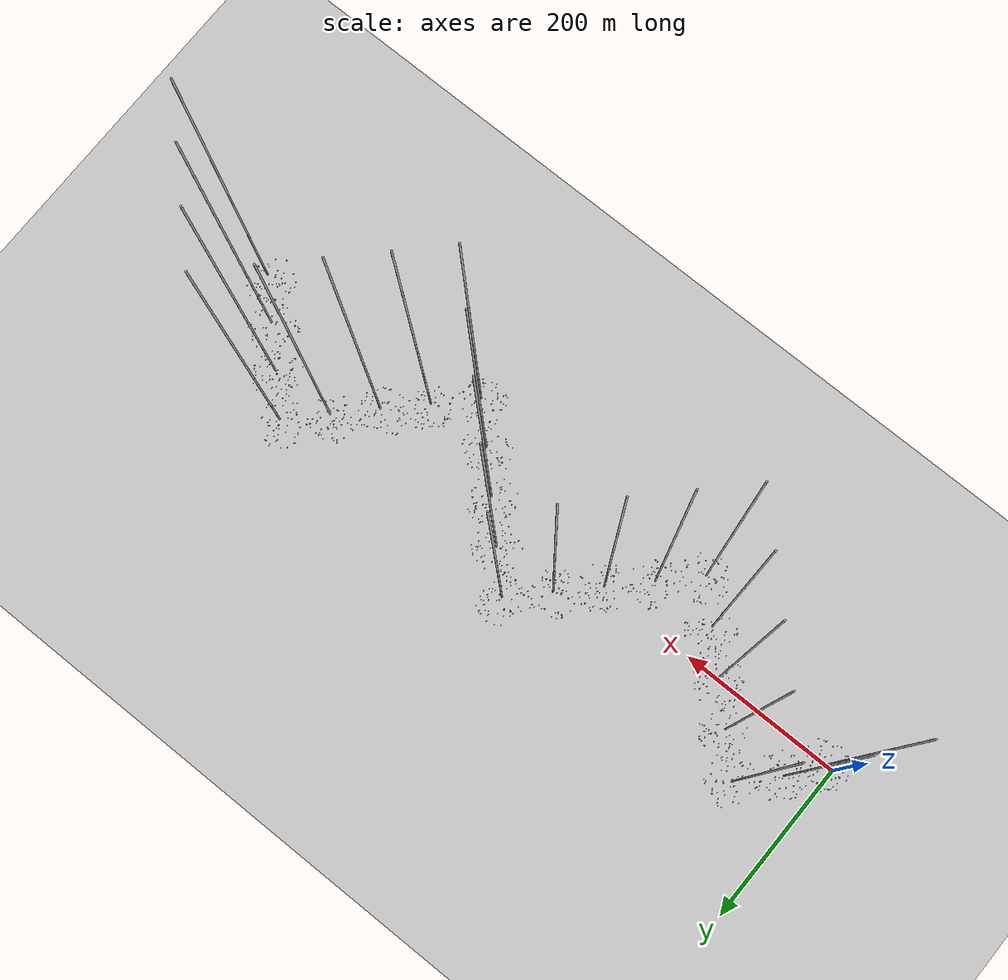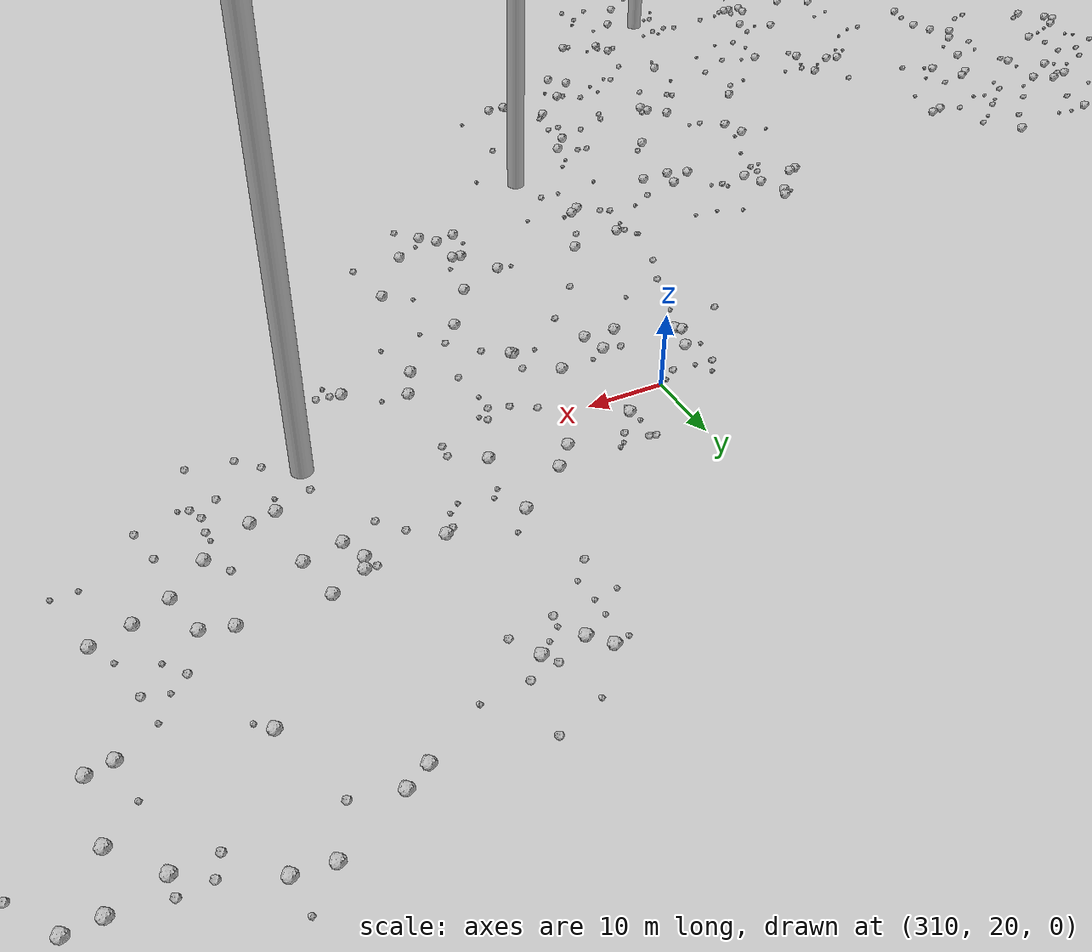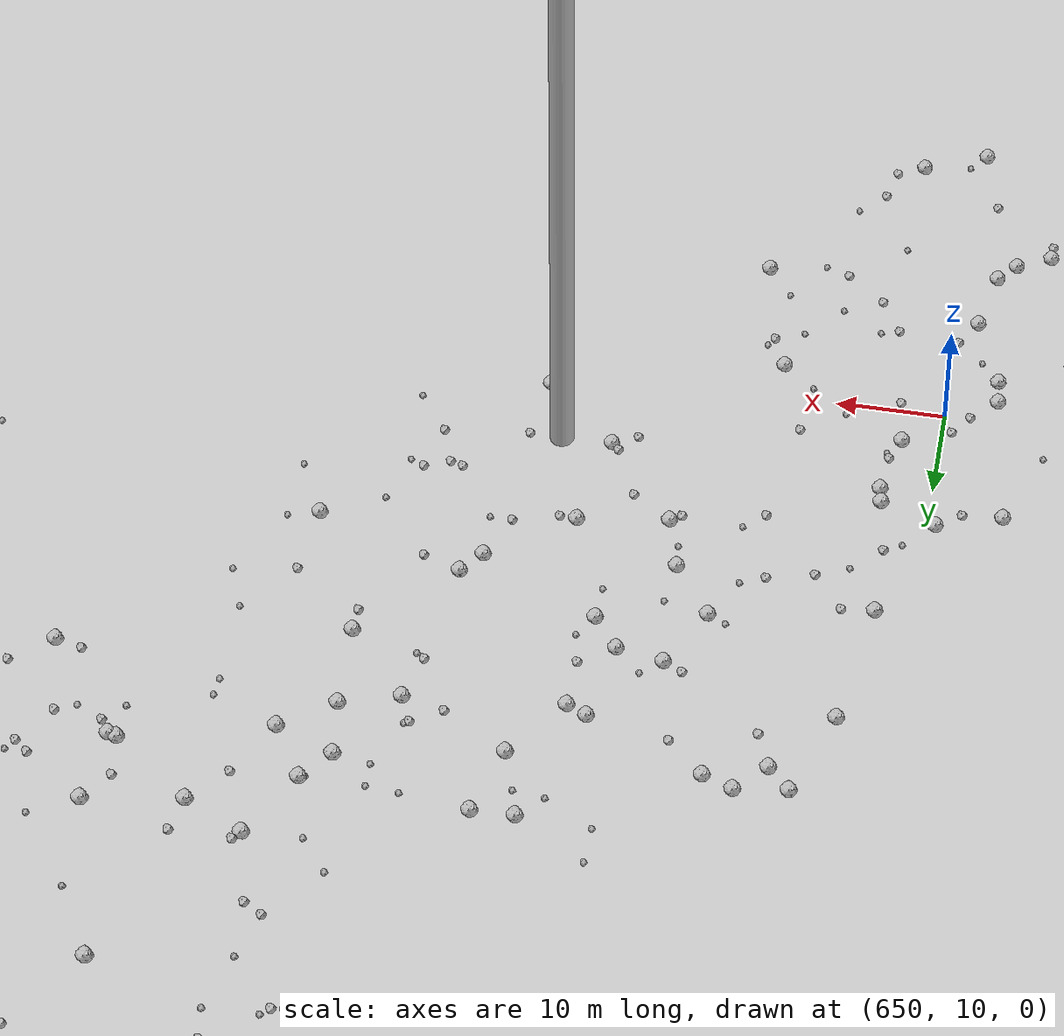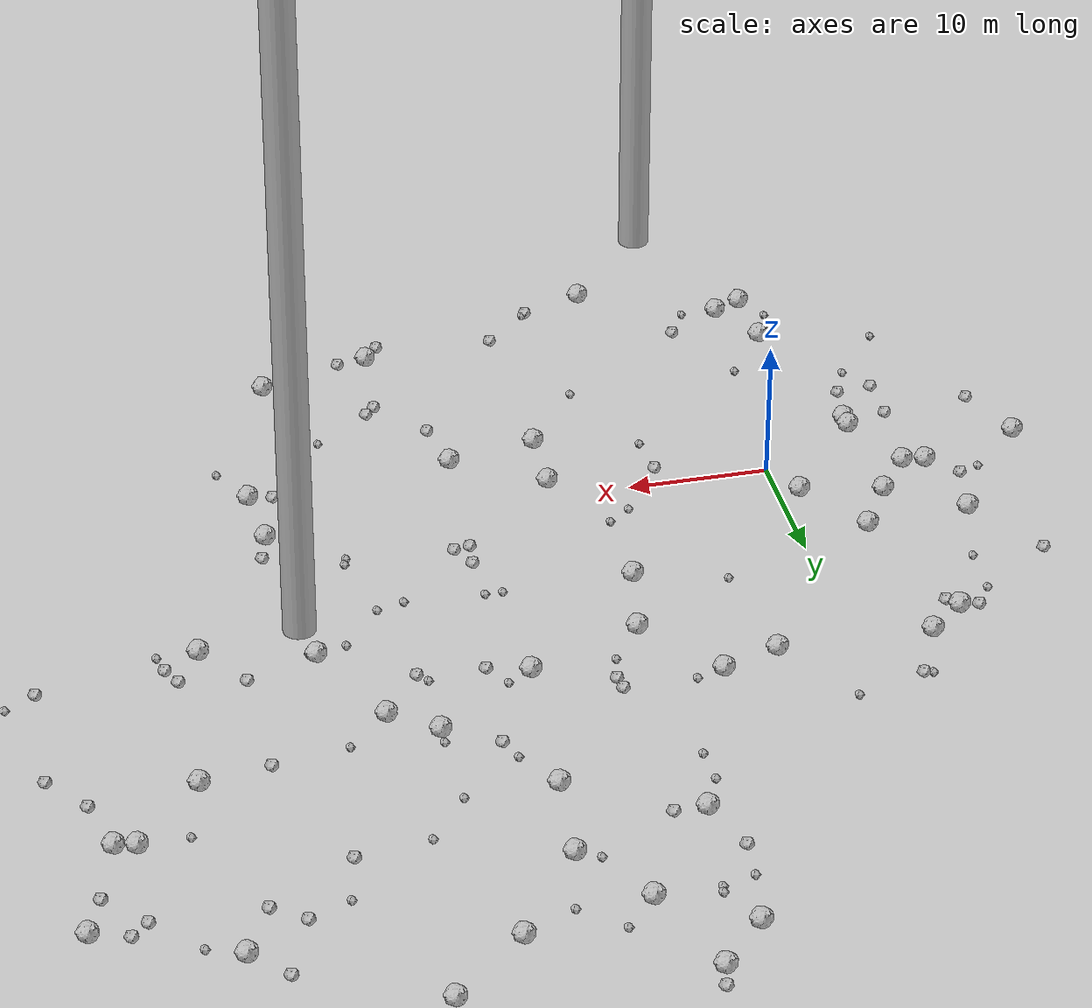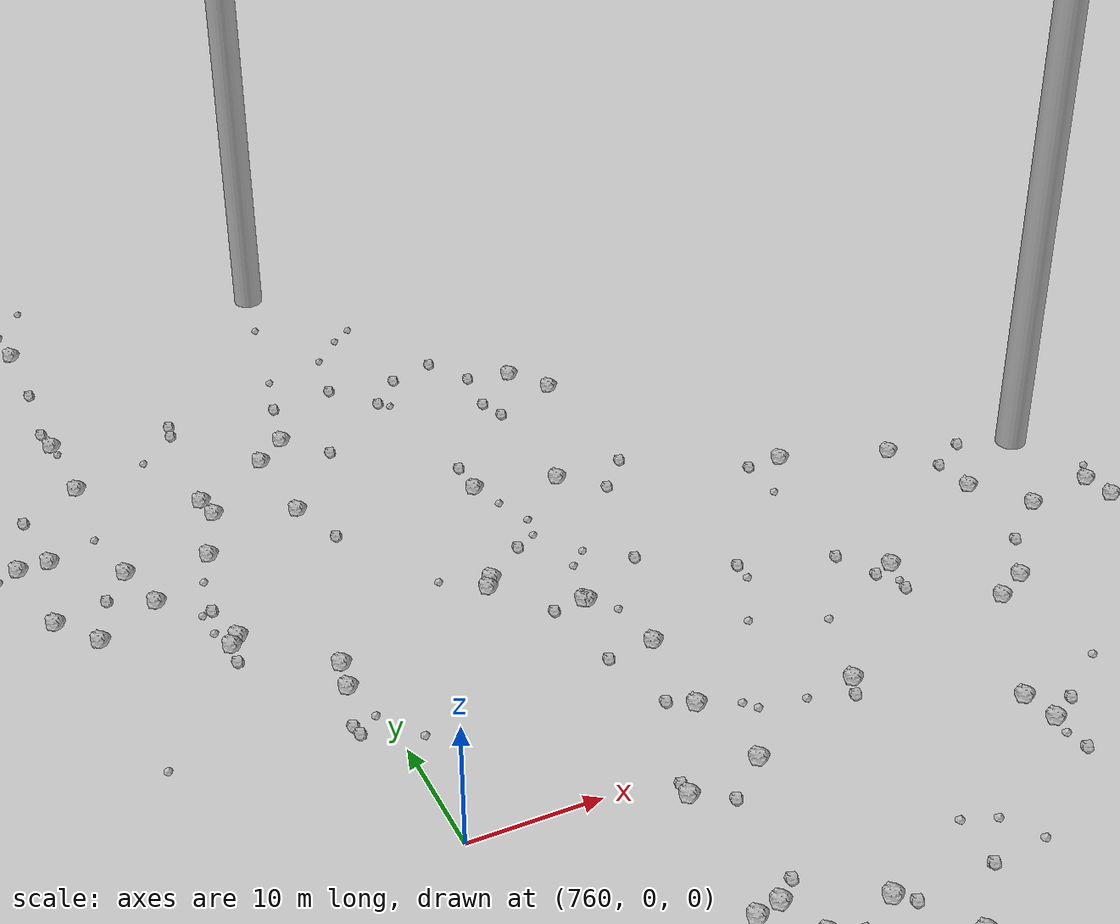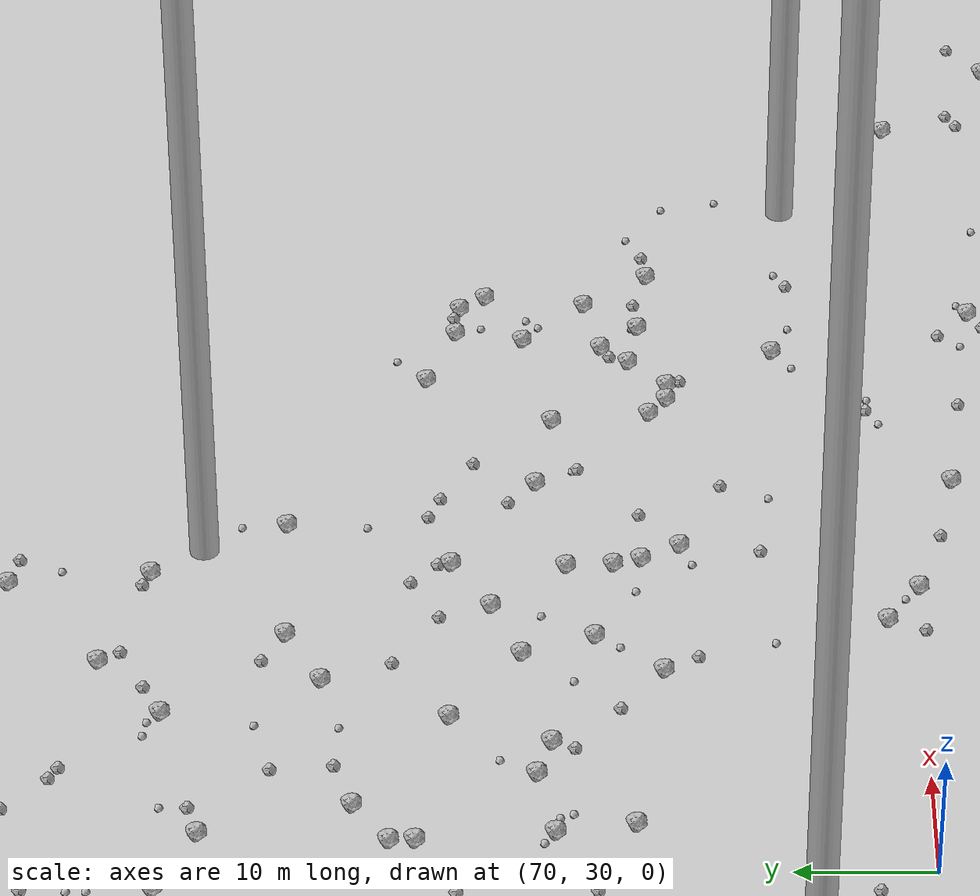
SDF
<sdf version="1.6">
 <world name="default">
  <include><uri>model://custom_ground</uri></include>
  <include><uri>model://sun</uri></include>
  <spherical_coordinates>
   <surface_model>EARTH_WGS84</surface_model>
   <latitude_deg>38.161479</latitude_deg>
   <longitude_deg>-122.454630</longitude_deg>
   <elevation>488.0</elevation>
   <heading_deg>90</heading_deg>
  </spherical_coordinates>
  <model name="rock1_0_0">
   <include><uri>model://rock1</uri><pose>-18.3554256299761 -0.8736387125041354 0.5 0 0 0</pose></include>
  </model>
  <model name="rock1_0_1">
   <include><uri>model://rock1</uri><pose>-11.117513339005576 1.4484345504251053 0.5 0 0 0</pose></include>
  </model>
  <model name="rock1_0_2">
   <include><uri>model://rock1</uri><pose>15.420586032131304 -6.97239388748444 0.5 0 0 0</pose></include>
  </model>
  <model name="rock1_0_3">
   <include><uri>model://rock1</uri><pose>-1.428237766085335 3.2156876742978397 0.5 0 0 0</pose></include>
  </model>
  <model name="rock1_0_4">
   <include><uri>model://rock1</uri><pose>7.727987030799962 -25.987101020668593 0.5 0 0 0</pose></include>
  </model>
  <model name="rock1_0_5">
   <include><uri>model://rock1</uri><pose>13.642779727651714 16.909072541101594 0.5 0 0 0</pose></include>
  </model>
  <model name="rock1_0_6">
   <include><uri>model://rock1</uri><pose>33.556714146757656 -1.0128879427130926 0.5 0 0 0</pose></include>
  </model>
  <model name="rock1_0_7">
   <include><uri>model://rock1</uri><pose>33.070485443908446 -18.156992440177937 0.5 0 0 0</pose></include>
  </model>
  <model name="rock1_0_8">
   <include><uri>model://rock1</uri><pose>21.79771678929623 -5.688780286805809 0.5 0 0 0</pose></include>
  </model>
  <model name="rock1_0_9">
   <include><uri>model://rock1</uri><pose>36.46240503108014 -4.162233522423666 0.5 0 0 0</pose></include>
  </model>
  <model name="rock1_0_10">
   <include><uri>model://rock1</uri><pose>25.01887447976599 -20.555709112987397 0.5 0 0 0</pose></include>
  </model>
  <model name="rock1_0_11">
   <include><uri>model://rock1</uri><pose>-12.263296120027965 7.89504189724137 0.5 0 0 0</pose></include>
  </model>
  <model name="rock1_0_12">
   <include><uri>model://rock1</uri><pose>9.214269222641718 22.827229892223436 0.5 0 0 0</pose></include>
  </model>
  <model name="rock1_0_13">
   <include><uri>model://rock1</uri><pose>-4.8686404893557995 8.474588985718349 0.5 0 0 0</pose></include>
  </model>
  <model name="rock1_0_14">
   <include><uri>model://rock1</uri><pose>-5.526882922278704 21.56909924106602 0.5 0 0 0</pose></include>
  </model>
  <model name="rock1_0_15">
   <include><uri>model://rock1</uri><pose>-4.100725002524721 -17.574050393754053 0.5 0 0 0</pose></include>
  </model>
  <model name="rock1_0_16">
   <include><uri>model://rock1</uri><pose>-9.525316424813719 1.1926285499723512 0.5 0 0 0</pose></include>
  </model>
  <model name="rock1_0_17">
   <include><uri>model://rock1</uri><pose>-7.058738284920631 -4.104013358105544 0.5 0 0 0</pose></include>
  </model>
  <model name="rock1_0_18">
   <include><uri>model://rock1</uri><pose>15.574710040196308 -1.7353222334232719 0.5 0 0 0</pose></include>
  </model>
  <model name="rock1_0_19">
   <include><uri>model://rock1</uri><pose>5.1720518612440785 21.344476843395434 0.5 0 0 0</pose></include>
  </model>
  <model name="rock1_0_20">
   <include><uri>model://rock1</uri><pose>-8.108151208895176 19.2590952053258 0.5 0 0 0</pose></include>
  </model>
  <model name="rock1_0_21">
   <include><uri>model://rock1</uri><pose>12.468474040914543 10.855675110598987 0.5 0 0 0</pose></include>
  </model>
  <model name="rock1_0_22">
   <include><uri>model://rock1</uri><pose>-3.8867653958283483 -22.608318471364235 0.5 0 0 0</pose></include>
  </model>
  <model name="rock1_0_23">
   <include><uri>model://rock1</uri><pose>-7.011666181019439 -5.152750772076445 0.5 0 0 0</pose></include>
  </model>
  <model name="rock1_0_24">
   <include><uri>model://rock1</uri><pose>-7.166404070583468 4.440676341268208 0.5 0 0 0</pose></include>
  </model>
  <model name="rock1_0_25">
   <include><uri>model://rock1</uri><pose>-1.8506823339004157 -21.65955347349154 0.5 0 0 0</pose></include>
  </model>
  <model name="rock1_0_26">
   <include><uri>model://rock1</uri><pose>36.11518519640164 0.9886216196213802 0.5 0 0 0</pose></include>
  </model>
  <model name="rock2_0_0">
   <include><uri>model://rock2</uri><pose>23.693230865221565 5.267143341048751 0.3 0 0 0</pose></include>
  </model>
  <model name="rock2_0_1">
   <include><uri>model://rock2</uri><pose>-7.633288472252689 -8.606525182506594 0.3 0 0 0</pose></include>
  </model>
  <model name="rock2_0_2">
   <include><uri>model://rock2</uri><pose>36.71083210632222 3.4228751149210908 0.3 0 0 0</pose></include>
  </model>
  <model name="rock2_0_3">
   <include><uri>model://rock2</uri><pose>23.905768866795533 -22.023853762079067 0.3 0 0 0</pose></include>
  </model>
  <model name="rock2_0_4">
   <include><uri>model://rock2</uri><pose>16.320432029543227 22.271745437663803 0.3 0 0 0</pose></include>
  </model>
  <model name="rock2_0_5">
   <include><uri>model://rock2</uri><pose>34.74006000884111 -3.895885514258616 0.3 0 0 0</pose></include>
  </model>
  <model name="rock2_0_6">
   <include><uri>model://rock2</uri><pose>-15.891832086969739 13.746266071822475 0.3 0 0 0</pose></include>
  </model>
  <model name="rock2_0_7">
   <include><uri>model://rock2</uri><pose>7.783063344215783 -1.738038924789553 0.3 0 0 0</pose></include>
  </model>
  <model name="rock2_0_8">
   <include><uri>model://rock2</uri><pose>22.497739120578906 -9.992544367602921 0.3 0 0 0</pose></include>
  </model>
  <model name="rock2_0_9">
   <include><uri>model://rock2</uri><pose>15.507907019454699 -21.121759211765667 0.3 0 0 0</pose></include>
  </model>
  <model name="rock2_0_10">
   <include><uri>model://rock2</uri><pose>25.61821589275403 -13.943143640709835 0.3 0 0 0</pose></include>
  </model>
  <model name="rock2_0_11">
   <include><uri>model://rock2</uri><pose>-13.124862266021623 3.4909629702981775 0.3 0 0 0</pose></include>
  </model>
  <model name="rock2_0_12">
   <include><uri>model://rock2</uri><pose>-7.445969083288199 18.33259179384703 0.3 0 0 0</pose></include>
  </model>
  <model name="rock2_0_13">
   <include><uri>model://rock2</uri><pose>24.476231466828743 19.3190034472753 0.3 0 0 0</pose></include>
  </model>
  <model name="rock2_0_14">
   <include><uri>model://rock2</uri><pose>22.552377003030948 5.055558269202471 0.3 0 0 0</pose></include>
  </model>
  <model name="rock2_0_15">
   <include><uri>model://rock2</uri><pose>-9.494107905261917 19.324101409345694 0.3 0 0 0</pose></include>
  </model>
  <model name="rock2_0_16">
   <include><uri>model://rock2</uri><pose>27.106773929064907 -20.262573861364007 0.3 0 0 0</pose></include>
  </model>
  <model name="rock2_0_17">
   <include><uri>model://rock2</uri><pose>-10.188949994500828 -8.895530271203292 0.3 0 0 0</pose></include>
  </model>
  <model name="rock2_0_18">
   <include><uri>model://rock2</uri><pose>22.78352362491379 7.089481815616416 0.3 0 0 0</pose></include>
  </model>
  <model name="rock2_0_19">
   <include><uri>model://rock2</uri><pose>-3.5475721921079355 26.017543397973526 0.3 0 0 0</pose></include>
  </model>
  <model name="rock2_0_20">
   <include><uri>model://rock2</uri><pose>-16.51096002946173 -5.943299387653088 0.3 0 0 0</pose></include>
  </model>
  <model name="rock2_0_21">
   <include><uri>model://rock2</uri><pose>21.46666972147797 -5.90016558236163 0.3 0 0 0</pose></include>
  </model>
  <model name="rock2_0_22">
   <include><uri>model://rock2</uri><pose>-10.181853133115562 -5.231280807970215 0.3 0 0 0</pose></include>
  </model>
  <model name="rock2_0_23">
   <include><uri>model://rock2</uri><pose>12.111226400191399 -24.463446933794124 0.3 0 0 0</pose></include>
  </model>
  <model name="rock2_0_24">
   <include><uri>model://rock2</uri><pose>2.0254279802466684 -19.327963202281424 0.3 0 0 0</pose></include>
  </model>
  <model name="rock2_0_25">
   <include><uri>model://rock2</uri><pose>26.35647157501792 -13.096829909684377 0.3 0 0 0</pose></include>
  </model>
  <model name="rock2_0_26">
   <include><uri>model://rock2</uri><pose>16.171301909867317 23.43210970812686 0.3 0 0 0</pose></include>
  </model>
  <model name="rock3_0_0">
   <include><uri>model://rock3</uri><pose>-8.797253218383197 -11.258566156526367 0.2 0 0 0</pose></include>
  </model>
  <model name="rock3_0_1">
   <include><uri>model://rock3</uri><pose>22.673613491739964 10.818339028497675 0.2 0 0 0</pose></include>
  </model>
  <model name="rock3_0_2">
   <include><uri>model://rock3</uri><pose>-10.919392695370096 13.559707705248464 0.2 0 0 0</pose></include>
  </model>
  <model name="rock3_0_3">
   <include><uri>model://rock3</uri><pose>-5.365061728335876 -20.413784593499567 0.2 0 0 0</pose></include>
  </model>
  <model name="rock3_0_4">
   <include><uri>model://rock3</uri><pose>30.378490131550898 -10.137976040769288 0.2 0 0 0</pose></include>
  </model>
  <model name="rock3_0_5">
   <include><uri>model://rock3</uri><pose>1.2291533670183732 27.437988150542118 0.2 0 0 0</pose></include>
  </model>
  <model name="rock3_0_6">
   <include><uri>model://rock3</uri><pose>12.345557872824251 -24.291033518227756 0.2 0 0 0</pose></include>
  </model>
  <model name="rock3_0_7">
   <include><uri>model://rock3</uri><pose>8.002031749050754 -5.158613142657451 0.2 0 0 0</pose></include>
  </model>
  <model name="rock3_0_8">
   <include><uri>model://rock3</uri><pose>21.46290273004226 10.83191468560716 0.2 0 0 0</pose></include>
  </model>
  <model name="rock3_0_9">
   <include><uri>model://rock3</uri><pose>30.1690534776329 11.092696721672695 0.2 0 0 0</pose></include>
  </model>
  <model name="rock3_0_10">
   <include><uri>model://rock3</uri><pose>10.749686489708584 2.8445145088360846 0.2 0 0 0</pose></include>
  </model>
  <model name="rock3_0_11">
   <include><uri>model://rock3</uri><pose>11.31167846961986 -12.72388018515571 0.2 0 0 0</pose></include>
  </model>
  <model name="rock3_0_12">
   <include><uri>model://rock3</uri><pose>23.308462892109063 21.123925182809444 0.2 0 0 0</pose></include>
  </model>
  <model name="rock3_0_13">
   <include><uri>model://rock3</uri><pose>-4.224722004921254 26.09956801934827 0.2 0 0 0</pose></include>
  </model>
  <model name="rock3_0_14">
   <include><uri>model://rock3</uri><pose>-10.72398282325862 17.431543334197038 0.2 0 0 0</pose></include>
  </model>
  <model name="rock3_0_15">
   <include><uri>model://rock3</uri><pose>-1.1633324280441428 -13.183385422515212 0.2 0 0 0</pose></include>
  </model>
  <model name="rock3_0_16">
   <include><uri>model://rock3</uri><pose>28.21776015054548 10.518213623112167 0.2 0 0 0</pose></include>
  </model>
  <model name="rock3_0_17">
   <include><uri>model://rock3</uri><pose>31.305511226659526 5.277576515158614 0.2 0 0 0</pose></include>
  </model>
  <model name="rock3_0_18">
   <include><uri>model://rock3</uri><pose>15.813722632961053 20.07489319952529 0.2 0 0 0</pose></include>
  </model>
  <model name="rock3_0_19">
   <include><uri>model://rock3</uri><pose>31.098939165179935 4.600861590175612 0.2 0 0 0</pose></include>
  </model>
  <model name="rock3_0_20">
   <include><uri>model://rock3</uri><pose>11.081776512891107 23.3140612290805 0.2 0 0 0</pose></include>
  </model>
  <model name="rock3_0_21">
   <include><uri>model://rock3</uri><pose>38.08262411860736 -7.657787025608332 0.2 0 0 0</pose></include>
  </model>
  <model name="rock3_0_22">
   <include><uri>model://rock3</uri><pose>6.114139544792735 12.550323129711373 0.2 0 0 0</pose></include>
  </model>
  <model name="rock3_0_23">
   <include><uri>model://rock3</uri><pose>-12.229936783530125 -15.755057972324805 0.2 0 0 0</pose></include>
  </model>
  <model name="rock3_0_24">
   <include><uri>model://rock3</uri><pose>0.6334552768609854 -21.834832798128943 0.2 0 0 0</pose></include>
  </model>
  <model name="rock3_0_25">
   <include><uri>model://rock3</uri><pose>-14.69168658046801 2.821689026575058 0.2 0 0 0</pose></include>
  </model>
  <model name="rock3_0_26">
   <include><uri>model://rock3</uri><pose>12.346411576196964 4.105723404749845 0.2 0 0 0</pose></include>
  </model>
  <model name="rock1_1_0">
   <include><uri>model://rock1</uri><pose>61.65252095021306 28.286651017497555 0.5 0 0 0</pose></include>
  </model>
  <model name="rock1_1_1">
   <include><uri>model://rock1</uri><pose>51.068164736633534 32.744224715946416 0.5 0 0 0</pose></include>
  </model>
  <model name="rock1_1_2">
   <include><uri>model://rock1</uri><pose>35.13477342186604 15.417543813272802 0.5 0 0 0</pose></include>
  </model>
  <model name="rock1_1_3">
   <include><uri>model://rock1</uri><pose>52.23101747007865 63.48774829839009 0.5 0 0 0</pose></include>
  </model>
  <model name="rock1_1_4">
   <include><uri>model://rock1</uri><pose>21.654740240169037 20.20428124026246 0.5 0 0 0</pose></include>
  </model>
  <model name="rock1_1_5">
   <include><uri>model://rock1</uri><pose>22.597846433163824 32.57005464303517 0.5 0 0 0</pose></include>
  </model>
  <model name="rock1_1_6">
   <include><uri>model://rock1</uri><pose>13.714064322436741 48.631450875259674 0.5 0 0 0</pose></include>
  </model>
  <model name="rock1_1_7">
   <include><uri>model://rock1</uri><pose>44.693983864277364 44.95583724191815 0.5 0 0 0</pose></include>
  </model>
  <model name="rock1_1_8">
   <include><uri>model://rock1</uri><pose>42.72919796751821 13.449765516254718 0.5 0 0 0</pose></include>
  </model>
  <model name="rock1_1_9">
   <include><uri>model://rock1</uri><pose>53.7808960218733 41.03293246068519 0.5 0 0 0</pose></include>
  </model>
  <model name="rock1_1_10">
   <include><uri>model://rock1</uri><pose>49.62049804527713 33.029278042592 0.5 0 0 0</pose></include>
  </model>
  <model name="rock1_1_11">
   <include><uri>model://rock1</uri><pose>31.878267550710703 22.94966892736388 0.5 0 0 0</pose></include>
  </model>
  <model name="rock1_1_12">
   <include><uri>model://rock1</uri><pose>53.38666575576634 65.99253172823498 0.5 0 0 0</pose></include>
  </model>
  <model name="rock1_1_13">
   <include><uri>model://rock1</uri><pose>23.229656709053486 39.67250776837557 0.5 0 0 0</pose></include>
  </model>
  <model name="rock1_1_14">
   <include><uri>model://rock1</uri><pose>34.19563089387295 67.86525036066841 0.5 0 0 0</pose></include>
  </model>
  <model name="rock1_1_15">
   <include><uri>model://rock1</uri><pose>14.032064550852745 37.00247358590572 0.5 0 0 0</pose></include>
  </model>
  <model name="rock1_1_16">
   <include><uri>model://rock1</uri><pose>19.507382798346214 44.944650643068265 0.5 0 0 0</pose></include>
  </model>
  <model name="rock1_1_17">
   <include><uri>model://rock1</uri><pose>54.08233612584718 58.51395751888857 0.5 0 0 0</pose></include>
  </model>
  <model name="rock1_1_18">
   <include><uri>model://rock1</uri><pose>60.76318245732883 31.342412036841054 0.5 0 0 0</pose></include>
  </model>
  <model name="rock1_1_19">
   <include><uri>model://rock1</uri><pose>28.77729841663275 25.35260821461877 0.5 0 0 0</pose></include>
  </model>
  <model name="rock1_1_20">
   <include><uri>model://rock1</uri><pose>63.12788887821419 30.785722232692482 0.5 0 0 0</pose></include>
  </model>
  <model name="rock1_1_21">
   <include><uri>model://rock1</uri><pose>28.064259039419056 46.86938652419125 0.5 0 0 0</pose></include>
  </model>
  <model name="rock1_1_22">
   <include><uri>model://rock1</uri><pose>44.868328003341745 27.58065563055305 0.5 0 0 0</pose></include>
  </model>
  <model name="rock1_1_23">
   <include><uri>model://rock1</uri><pose>22.94382252634923 57.102936120568415 0.5 0 0 0</pose></include>
  </model>
  <model name="rock1_1_24">
   <include><uri>model://rock1</uri><pose>16.892466046925446 52.244793541419014 0.5 0 0 0</pose></include>
  </model>
  <model name="rock1_1_25">
   <include><uri>model://rock1</uri><pose>33.61973224718409 59.372135314491864 0.5 0 0 0</pose></include>
  </model>
  <model name="rock1_1_26">
   <include><uri>model://rock1</uri><pose>33.2965241581708 51.66378870034229 0.5 0 0 0</pose></include>
  </model>
  <model name="rock2_1_0">
   <include><uri>model://rock2</uri><pose>50.01171956664065 40.651817057437974 0.3 0 0 0</pose></include>
  </model>
  <model name="rock2_1_1">
   <include><uri>model://rock2</uri><pose>45.15649043562783 59.543900050048265 0.3 0 0 0</pose></include>
  </model>
  <model name="rock2_1_2">
   <include><uri>model://rock2</uri><pose>42.62240658636849 40.857627772010666 0.3 0 0 0</pose></include>
  </model>
  <model name="rock2_1_3">
   <include><uri>model://rock2</uri><pose>52.532440575568835 37.825119719990525 0.3 0 0 0</pose></include>
  </model>
  <model name="rock2_1_4">
   <include><uri>model://rock2</uri><pose>12.572875846404445 41.15761705447436 0.3 0 0 0</pose></include>
  </model>
  <model name="rock2_1_5">
   <include><uri>model://rock2</uri><pose>25.14618356640034 27.474054673983627 0.3 0 0 0</pose></include>
  </model>
  <model name="rock2_1_6">
   <include><uri>model://rock2</uri><pose>52.07501642122745 28.422017468108784 0.3 0 0 0</pose></include>
  </model>
  <model name="rock2_1_7">
   <include><uri>model://rock2</uri><pose>67.88358757705916 34.11191261665718 0.3 0 0 0</pose></include>
  </model>
  <model name="rock2_1_8">
   <include><uri>model://rock2</uri><pose>40.919870342528945 59.86856708806626 0.3 0 0 0</pose></include>
  </model>
  <model name="rock2_1_9">
   <include><uri>model://rock2</uri><pose>17.314093572920893 54.01740406803699 0.3 0 0 0</pose></include>
  </model>
  <model name="rock2_1_10">
   <include><uri>model://rock2</uri><pose>44.4937022318338 16.447683704872745 0.3 0 0 0</pose></include>
  </model>
  <model name="rock2_1_11">
   <include><uri>model://rock2</uri><pose>16.197783100352993 36.928334885831326 0.3 0 0 0</pose></include>
  </model>
  <model name="rock2_1_12">
   <include><uri>model://rock2</uri><pose>29.092971033548253 19.074056997167293 0.3 0 0 0</pose></include>
  </model>
  <model name="rock2_1_13">
   <include><uri>model://rock2</uri><pose>50.306936973142854 67.16627865096017 0.3 0 0 0</pose></include>
  </model>
  <model name="rock2_1_14">
   <include><uri>model://rock2</uri><pose>59.233115030487724 52.45741090110986 0.3 0 0 0</pose></include>
  </model>
  <model name="rock2_1_15">
   <include><uri>model://rock2</uri><pose>45.174980955719946 14.974428766191682 0.3 0 0 0</pose></include>
  </model>
  <model name="rock2_1_16">
   <include><uri>model://rock2</uri><pose>30.25721964698722 60.582451926026216 0.3 0 0 0</pose></include>
  </model>
  <model name="rock2_1_17">
   <include><uri>model://rock2</uri><pose>54.38555658572837 25.35226593688045 0.3 0 0 0</pose></include>
  </model>
  <model name="rock2_1_18">
   <include><uri>model://rock2</uri><pose>35.41723593621053 15.218511023252026 0.3 0 0 0</pose></include>
  </model>
  <model name="rock2_1_19">
   <include><uri>model://rock2</uri><pose>40.03189929939988 26.722431293137806 0.3 0 0 0</pose></include>
  </model>
  <model name="rock2_1_20">
   <include><uri>model://rock2</uri><pose>36.651657591203765 37.163166197463994 0.3 0 0 0</pose></include>
  </model>
  <model name="rock2_1_21">
   <include><uri>model://rock2</uri><pose>42.39291173413541 47.407512570927665 0.3 0 0 0</pose></include>
  </model>
  <model name="rock2_1_22">
   <include><uri>model://rock2</uri><pose>53.84116084119982 15.829925094849882 0.3 0 0 0</pose></include>
  </model>
  <model name="rock2_1_23">
   <include><uri>model://rock2</uri><pose>33.61265036459176 61.351080313265825 0.3 0 0 0</pose></include>
  </model>
  <model name="rock2_1_24">
   <include><uri>model://rock2</uri><pose>40.05911721164945 17.254035323944308 0.3 0 0 0</pose></include>
  </model>
  <model name="rock2_1_25">
   <include><uri>model://rock2</uri><pose>40.476601619461604 42.468186675601416 0.3 0 0 0</pose></include>
  </model>
  <model name="rock2_1_26">
   <include><uri>model://rock2</uri><pose>51.20073264030142 41.78458976038573 0.3 0 0 0</pose></include>
  </model>
  <model name="rock3_1_0">
   <include><uri>model://rock3</uri><pose>31.46490567678207 36.31093264420619 0.2 0 0 0</pose></include>
  </model>
  <model name="rock3_1_1">
   <include><uri>model://rock3</uri><pose>12.80487682973373 31.381588933418637 0.2 0 0 0</pose></include>
  </model>
  <model name="rock3_1_2">
   <include><uri>model://rock3</uri><pose>24.374114830912355 44.95346144125934 0.2 0 0 0</pose></include>
  </model>
  <model name="rock3_1_3">
   <include><uri>model://rock3</uri><pose>17.822176073696554 59.54178503663549 0.2 0 0 0</pose></include>
  </model>
  <model name="rock3_1_4">
   <include><uri>model://rock3</uri><pose>63.93290000390086 29.59465042661682 0.2 0 0 0</pose></include>
  </model>
  <model name="rock3_1_5">
   <include><uri>model://rock3</uri><pose>15.157062547263141 45.33366310772708 0.2 0 0 0</pose></include>
  </model>
  <model name="rock3_1_6">
   <include><uri>model://rock3</uri><pose>12.692688186112452 34.11493406928831 0.2 0 0 0</pose></include>
  </model>
  <model name="rock3_1_7">
   <include><uri>model://rock3</uri><pose>28.38883757807698 19.767630374594447 0.2 0 0 0</pose></include>
  </model>
  <model name="rock3_1_8">
   <include><uri>model://rock3</uri><pose>20.39694352461498 58.867634099261714 0.2 0 0 0</pose></include>
  </model>
  <model name="rock3_1_9">
   <include><uri>model://rock3</uri><pose>28.717025739370353 26.587943916150188 0.2 0 0 0</pose></include>
  </model>
  <model name="rock3_1_10">
   <include><uri>model://rock3</uri><pose>32.92454755012518 14.662894519965107 0.2 0 0 0</pose></include>
  </model>
  <model name="rock3_1_11">
   <include><uri>model://rock3</uri><pose>45.45658317171854 13.362984374821165 0.2 0 0 0</pose></include>
  </model>
  <model name="rock3_1_12">
   <include><uri>model://rock3</uri><pose>37.52157606552491 41.12945905050378 0.2 0 0 0</pose></include>
  </model>
  <model name="rock3_1_13">
   <include><uri>model://rock3</uri><pose>24.411389090798174 29.15626230120324 0.2 0 0 0</pose></include>
  </model>
  <model name="rock3_1_14">
   <include><uri>model://rock3</uri><pose>21.62867846901792 47.371975406575274 0.2 0 0 0</pose></include>
  </model>
  <model name="rock3_1_15">
   <include><uri>model://rock3</uri><pose>55.938212471106745 16.99751531275357 0.2 0 0 0</pose></include>
  </model>
  <model name="rock3_1_16">
   <include><uri>model://rock3</uri><pose>44.461905703488355 53.62482986279318 0.2 0 0 0</pose></include>
  </model>
  <model name="rock3_1_17">
   <include><uri>model://rock3</uri><pose>15.038488831656478 44.77799373842242 0.2 0 0 0</pose></include>
  </model>
  <model name="rock3_1_18">
   <include><uri>model://rock3</uri><pose>12.797553109389634 44.10448518428663 0.2 0 0 0</pose></include>
  </model>
  <model name="rock3_1_19">
   <include><uri>model://rock3</uri><pose>42.424719614909115 64.86645816708914 0.2 0 0 0</pose></include>
  </model>
  <model name="rock3_1_20">
   <include><uri>model://rock3</uri><pose>47.01195630082006 43.81148276400044 0.2 0 0 0</pose></include>
  </model>
  <model name="rock3_1_21">
   <include><uri>model://rock3</uri><pose>34.73798329494798 25.78570533918218 0.2 0 0 0</pose></include>
  </model>
  <model name="rock3_1_22">
   <include><uri>model://rock3</uri><pose>54.81179482529306 59.53994544986875 0.2 0 0 0</pose></include>
  </model>
  <model name="rock3_1_23">
   <include><uri>model://rock3</uri><pose>46.14490713164228 32.807915599768144 0.2 0 0 0</pose></include>
  </model>
  <model name="rock3_1_24">
   <include><uri>model://rock3</uri><pose>21.614703622630515 40.335894003779885 0.2 0 0 0</pose></include>
  </model>
  <model name="rock3_1_25">
   <include><uri>model://rock3</uri><pose>28.71435674828344 32.60404495542389 0.2 0 0 0</pose></include>
  </model>
  <model name="rock3_1_26">
   <include><uri>model://rock3</uri><pose>61.34737064383169 43.43113635595298 0.2 0 0 0</pose></include>
  </model>
  <model name="rock1_2_0">
   <include><uri>model://rock1</uri><pose>87.48944390661696 102.54376078520481 0.5 0 0 0</pose></include>
  </model>
  <model name="rock1_2_1">
   <include><uri>model://rock1</uri><pose>100.8922312695597 96.38906094307012 0.5 0 0 0</pose></include>
  </model>
  <model name="rock1_2_2">
   <include><uri>model://rock1</uri><pose>90.0270320450926 73.12025860438406 0.5 0 0 0</pose></include>
  </model>
  <model name="rock1_2_3">
   <include><uri>model://rock1</uri><pose>74.71337479212715 50.66771357488168 0.5 0 0 0</pose></include>
  </model>
  <model name="rock1_2_4">
   <include><uri>model://rock1</uri><pose>107.78589512872689 76.26706805587662 0.5 0 0 0</pose></include>
  </model>
  <model name="rock1_2_5">
   <include><uri>model://rock1</uri><pose>72.92907577545454 67.76688390486417 0.5 0 0 0</pose></include>
  </model>
  <model name="rock1_2_6">
   <include><uri>model://rock1</uri><pose>93.06210551106867 58.80275687516969 0.5 0 0 0</pose></include>
  </model>
  <model name="rock1_2_7">
   <include><uri>model://rock1</uri><pose>98.45880865757354 61.07769553631286 0.5 0 0 0</pose></include>
  </model>
  <model name="rock1_2_8">
   <include><uri>model://rock1</uri><pose>78.80707934132022 102.78820949519977 0.5 0 0 0</pose></include>
  </model>
  <model name="rock1_2_9">
   <include><uri>model://rock1</uri><pose>63.998664614881534 95.16568095935835 0.5 0 0 0</pose></include>
  </model>
  <model name="rock1_2_10">
   <include><uri>model://rock1</uri><pose>54.282851382379896 67.63943716196272 0.5 0 0 0</pose></include>
  </model>
  <model name="rock1_2_11">
   <include><uri>model://rock1</uri><pose>67.9385692963941 83.72968947936218 0.5 0 0 0</pose></include>
  </model>
  <model name="rock1_2_12">
   <include><uri>model://rock1</uri><pose>73.84753445319203 56.25250021445965 0.5 0 0 0</pose></include>
  </model>
  <model name="rock1_2_13">
   <include><uri>model://rock1</uri><pose>86.03734517163119 63.86966237947344 0.5 0 0 0</pose></include>
  </model>
  <model name="rock1_2_14">
   <include><uri>model://rock1</uri><pose>103.31749894664861 64.05673589435499 0.5 0 0 0</pose></include>
  </model>
  <model name="rock1_2_15">
   <include><uri>model://rock1</uri><pose>86.34495644560769 84.3528646788253 0.5 0 0 0</pose></include>
  </model>
  <model name="rock1_2_16">
   <include><uri>model://rock1</uri><pose>92.0282549456073 89.1728663901199 0.5 0 0 0</pose></include>
  </model>
  <model name="rock1_2_17">
   <include><uri>model://rock1</uri><pose>76.59973834684641 70.42841493029766 0.5 0 0 0</pose></include>
  </model>
  <model name="rock1_2_18">
   <include><uri>model://rock1</uri><pose>83.3610366253854 56.56292297877576 0.5 0 0 0</pose></include>
  </model>
  <model name="rock1_2_19">
   <include><uri>model://rock1</uri><pose>95.12879685622971 75.87539582553057 0.5 0 0 0</pose></include>
  </model>
  <model name="rock1_2_20">
   <include><uri>model://rock1</uri><pose>79.9607537262097 57.58842271841788 0.5 0 0 0</pose></include>
  </model>
  <model name="rock1_2_21">
   <include><uri>model://rock1</uri><pose>72.97831861302133 65.96024805219116 0.5 0 0 0</pose></include>
  </model>
  <model name="rock1_2_22">
   <include><uri>model://rock1</uri><pose>76.74036885580927 106.77398048623326 0.5 0 0 0</pose></include>
  </model>
  <model name="rock1_2_23">
   <include><uri>model://rock1</uri><pose>102.12248662681847 86.0257559125805 0.5 0 0 0</pose></include>
  </model>
  <model name="rock1_2_24">
   <include><uri>model://rock1</uri><pose>90.28417341943265 98.11330005894662 0.5 0 0 0</pose></include>
  </model>
  <model name="rock1_2_25">
   <include><uri>model://rock1</uri><pose>73.5671244319161 81.01104512904858 0.5 0 0 0</pose></include>
  </model>
  <model name="rock1_2_26">
   <include><uri>model://rock1</uri><pose>58.60666189982082 63.42715662151586 0.5 0 0 0</pose></include>
  </model>
  <model name="rock2_2_0">
   <include><uri>model://rock2</uri><pose>92.00968621329856 77.43758710907025 0.3 0 0 0</pose></include>
  </model>
  <model name="rock2_2_1">
   <include><uri>model://rock2</uri><pose>92.9246060888418 87.62609620887923 0.3 0 0 0</pose></include>
  </model>
  <model name="rock2_2_2">
   <include><uri>model://rock2</uri><pose>103.44321674706072 95.68782632507119 0.3 0 0 0</pose></include>
  </model>
  <model name="rock2_2_3">
   <include><uri>model://rock2</uri><pose>74.29612042421908 108.19566883221401 0.3 0 0 0</pose></include>
  </model>
  <model name="rock2_2_4">
   <include><uri>model://rock2</uri><pose>68.52223594665833 88.42385674062241 0.3 0 0 0</pose></include>
  </model>
  <model name="rock2_2_5">
   <include><uri>model://rock2</uri><pose>76.13357692902885 81.81348145697731 0.3 0 0 0</pose></include>
  </model>
  <model name="rock2_2_6">
   <include><uri>model://rock2</uri><pose>89.07300280317385 85.73620897152045 0.3 0 0 0</pose></include>
  </model>
  <model name="rock2_2_7">
   <include><uri>model://rock2</uri><pose>100.62503260781278 98.81531559471533 0.3 0 0 0</pose></include>
  </model>
  <model name="rock2_2_8">
   <include><uri>model://rock2</uri><pose>83.95709455480579 97.68694265083371 0.3 0 0 0</pose></include>
  </model>
  <model name="rock2_2_9">
   <include><uri>model://rock2</uri><pose>103.09535594759426 65.0173354959413 0.3 0 0 0</pose></include>
  </model>
  <model name="rock2_2_10">
   <include><uri>model://rock2</uri><pose>91.79485340116146 68.05262552526102 0.3 0 0 0</pose></include>
  </model>
  <model name="rock2_2_11">
   <include><uri>model://rock2</uri><pose>75.95650014930942 94.75299127504329 0.3 0 0 0</pose></include>
  </model>
  <model name="rock2_2_12">
   <include><uri>model://rock2</uri><pose>80.17835288719199 76.29268841361429 0.3 0 0 0</pose></include>
  </model>
  <model name="rock2_2_13">
   <include><uri>model://rock2</uri><pose>100.96974733703209 66.94145867433578 0.3 0 0 0</pose></include>
  </model>
  <model name="rock2_2_14">
   <include><uri>model://rock2</uri><pose>80.29069185208343 91.09612396705909 0.3 0 0 0</pose></include>
  </model>
  <model name="rock2_2_15">
   <include><uri>model://rock2</uri><pose>67.7980492978215 53.329739286248 0.3 0 0 0</pose></include>
  </model>
  <model name="rock2_2_16">
   <include><uri>model://rock2</uri><pose>79.15941028392845 91.70406317748653 0.3 0 0 0</pose></include>
  </model>
  <model name="rock2_2_17">
   <include><uri>model://rock2</uri><pose>80.59469800166843 71.83153629254193 0.3 0 0 0</pose></include>
  </model>
  <model name="rock2_2_18">
   <include><uri>model://rock2</uri><pose>67.52620676326616 63.00917426717031 0.3 0 0 0</pose></include>
  </model>
  <model name="rock2_2_19">
   <include><uri>model://rock2</uri><pose>89.05275850226732 99.75770710834949 0.3 0 0 0</pose></include>
  </model>
  <model name="rock2_2_20">
   <include><uri>model://rock2</uri><pose>97.00903169897867 64.78619250277612 0.3 0 0 0</pose></include>
  </model>
  <model name="rock2_2_21">
   <include><uri>model://rock2</uri><pose>66.17327890710874 89.67548440176114 0.3 0 0 0</pose></include>
  </model>
  <model name="rock2_2_22">
   <include><uri>model://rock2</uri><pose>67.6335151455627 92.74162023619289 0.3 0 0 0</pose></include>
  </model>
  <model name="rock2_2_23">
   <include><uri>model://rock2</uri><pose>55.70712126351239 76.2372213280992 0.3 0 0 0</pose></include>
  </model>
  <model name="rock2_2_24">
   <include><uri>model://rock2</uri><pose>100.62246554237244 86.53196495144613 0.3 0 0 0</pose></include>
  </model>
  <model name="rock2_2_25">
   <include><uri>model://rock2</uri><pose>82.57345761326593 54.911180877525915 0.3 0 0 0</pose></include>
  </model>
  <model name="rock2_2_26">
   <include><uri>model://rock2</uri><pose>86.89197601765281 51.65964742116401 0.3 0 0 0</pose></include>
  </model>
  <model name="rock3_2_0">
   <include><uri>model://rock3</uri><pose>76.19762518064987 83.7519144437261 0.2 0 0 0</pose></include>
  </model>
  <model name="rock3_2_1">
   <include><uri>model://rock3</uri><pose>60.07663463605783 99.79971278324957 0.2 0 0 0</pose></include>
  </model>
  <model name="rock3_2_2">
   <include><uri>model://rock3</uri><pose>100.76961090310229 100.61286941692049 0.2 0 0 0</pose></include>
  </model>
  <model name="rock3_2_3">
   <include><uri>model://rock3</uri><pose>81.35177256266493 60.15960033956147 0.2 0 0 0</pose></include>
  </model>
  <model name="rock3_2_4">
   <include><uri>model://rock3</uri><pose>89.72555612386617 100.90907349811823 0.2 0 0 0</pose></include>
  </model>
  <model name="rock3_2_5">
   <include><uri>model://rock3</uri><pose>82.63364688659854 102.84716224066905 0.2 0 0 0</pose></include>
  </model>
  <model name="rock3_2_6">
   <include><uri>model://rock3</uri><pose>89.95093007905938 54.968107520225196 0.2 0 0 0</pose></include>
  </model>
  <model name="rock3_2_7">
   <include><uri>model://rock3</uri><pose>76.95393567044403 108.4696142771443 0.2 0 0 0</pose></include>
  </model>
  <model name="rock3_2_8">
   <include><uri>model://rock3</uri><pose>67.56680380985145 89.556486227883 0.2 0 0 0</pose></include>
  </model>
  <model name="rock3_2_9">
   <include><uri>model://rock3</uri><pose>67.60919743721452 88.17092027816457 0.2 0 0 0</pose></include>
  </model>
  <model name="rock3_2_10">
   <include><uri>model://rock3</uri><pose>62.840640441598396 67.26516077478634 0.2 0 0 0</pose></include>
  </model>
  <model name="rock3_2_11">
   <include><uri>model://rock3</uri><pose>102.237091249987 92.48280558199681 0.2 0 0 0</pose></include>
  </model>
  <model name="rock3_2_12">
   <include><uri>model://rock3</uri><pose>79.72854534722028 104.67897280237241 0.2 0 0 0</pose></include>
  </model>
  <model name="rock3_2_13">
   <include><uri>model://rock3</uri><pose>84.77517133155864 71.58749388848592 0.2 0 0 0</pose></include>
  </model>
  <model name="rock3_2_14">
   <include><uri>model://rock3</uri><pose>97.29992673975488 57.36015245247123 0.2 0 0 0</pose></include>
  </model>
  <model name="rock3_2_15">
   <include><uri>model://rock3</uri><pose>107.49832088883412 79.55496942744024 0.2 0 0 0</pose></include>
  </model>
  <model name="rock3_2_16">
   <include><uri>model://rock3</uri><pose>58.36465859754279 92.25527966989316 0.2 0 0 0</pose></include>
  </model>
  <model name="rock3_2_17">
   <include><uri>model://rock3</uri><pose>70.07078386175783 107.46914292679335 0.2 0 0 0</pose></include>
  </model>
  <model name="rock3_2_18">
   <include><uri>model://rock3</uri><pose>85.30397238490492 85.19972587347405 0.2 0 0 0</pose></include>
  </model>
  <model name="rock3_2_19">
   <include><uri>model://rock3</uri><pose>72.66651337776509 56.971857696028096 0.2 0 0 0</pose></include>
  </model>
  <model name="rock3_2_20">
   <include><uri>model://rock3</uri><pose>80.75538559567138 103.90945023514516 0.2 0 0 0</pose></include>
  </model>
  <model name="rock3_2_21">
   <include><uri>model://rock3</uri><pose>85.00361663940663 77.60332804682609 0.2 0 0 0</pose></include>
  </model>
  <model name="rock3_2_22">
   <include><uri>model://rock3</uri><pose>83.82621140633115 85.40447284659308 0.2 0 0 0</pose></include>
  </model>
  <model name="rock3_2_23">
   <include><uri>model://rock3</uri><pose>75.68688428147054 54.96354821476243 0.2 0 0 0</pose></include>
  </model>
  <model name="rock3_2_24">
   <include><uri>model://rock3</uri><pose>57.754704668280425 61.483270133483664 0.2 0 0 0</pose></include>
  </model>
  <model name="rock3_2_25">
   <include><uri>model://rock3</uri><pose>107.49415925768324 70.26763891024022 0.2 0 0 0</pose></include>
  </model>
  <model name="rock3_2_26">
   <include><uri>model://rock3</uri><pose>75.2636053939911 55.90888101732403 0.2 0 0 0</pose></include>
  </model>
  <model name="rock1_3_0">
   <include><uri>model://rock1</uri><pose>134.69578331606814 24.343628219077345 0.5 0 0 0</pose></include>
  </model>
  <model name="rock1_3_1">
   <include><uri>model://rock1</uri><pose>96.99568319614309 32.27170894765801 0.5 0 0 0</pose></include>
  </model>
  <model name="rock1_3_2">
   <include><uri>model://rock1</uri><pose>103.10955682966014 55.61473980668497 0.5 0 0 0</pose></include>
  </model>
  <model name="rock1_3_3">
   <include><uri>model://rock1</uri><pose>129.60951742916933 39.78994384024348 0.5 0 0 0</pose></include>
  </model>
  <model name="rock1_3_4">
   <include><uri>model://rock1</uri><pose>103.9334763957944 50.114412439473895 0.5 0 0 0</pose></include>
  </model>
  <model name="rock1_3_5">
   <include><uri>model://rock1</uri><pose>125.82361803764539 66.3752004937613 0.5 0 0 0</pose></include>
  </model>
  <model name="rock1_3_6">
   <include><uri>model://rock1</uri><pose>112.95227183658794 57.92323646807186 0.5 0 0 0</pose></include>
  </model>
  <model name="rock1_3_7">
   <include><uri>model://rock1</uri><pose>120.67084902469992 56.75851102183705 0.5 0 0 0</pose></include>
  </model>
  <model name="rock1_3_8">
   <include><uri>model://rock1</uri><pose>125.28109865331984 47.96665972917923 0.5 0 0 0</pose></include>
  </model>
  <model name="rock1_3_9">
   <include><uri>model://rock1</uri><pose>127.17358653901951 12.667771858658634 0.5 0 0 0</pose></include>
  </model>
  <model name="rock1_3_10">
   <include><uri>model://rock1</uri><pose>136.6244770045555 62.03799235172699 0.5 0 0 0</pose></include>
  </model>
  <model name="rock1_3_11">
   <include><uri>model://rock1</uri><pose>131.8935842183627 64.25542417958385 0.5 0 0 0</pose></include>
  </model>
  <model name="rock1_3_12">
   <include><uri>model://rock1</uri><pose>103.31075687192784 52.14495977349453 0.5 0 0 0</pose></include>
  </model>
  <model name="rock1_3_13">
   <include><uri>model://rock1</uri><pose>135.09272555372343 63.977262365589546 0.5 0 0 0</pose></include>
  </model>
  <model name="rock1_3_14">
   <include><uri>model://rock1</uri><pose>132.68137165575627 50.14092469850436 0.5 0 0 0</pose></include>
  </model>
  <model name="rock1_3_15">
   <include><uri>model://rock1</uri><pose>105.52617885891624 47.25273109627535 0.5 0 0 0</pose></include>
  </model>
  <model name="rock1_3_16">
   <include><uri>model://rock1</uri><pose>123.4855908085129 48.025895195766594 0.5 0 0 0</pose></include>
  </model>
  <model name="rock1_3_17">
   <include><uri>model://rock1</uri><pose>131.0062641465539 59.06452251348307 0.5 0 0 0</pose></include>
  </model>
  <model name="rock1_3_18">
   <include><uri>model://rock1</uri><pose>91.2533381084417 48.545972886297534 0.5 0 0 0</pose></include>
  </model>
  <model name="rock1_3_19">
   <include><uri>model://rock1</uri><pose>130.09903474429558 53.02130741179402 0.5 0 0 0</pose></include>
  </model>
  <model name="rock1_3_20">
   <include><uri>model://rock1</uri><pose>95.05228779576692 53.505387706552156 0.5 0 0 0</pose></include>
  </model>
  <model name="rock1_3_21">
   <include><uri>model://rock1</uri><pose>128.19317733839392 50.89312067668083 0.5 0 0 0</pose></include>
  </model>
  <model name="rock1_3_22">
   <include><uri>model://rock1</uri><pose>139.46437028471246 49.416152258640516 0.5 0 0 0</pose></include>
  </model>
  <model name="rock1_3_23">
   <include><uri>model://rock1</uri><pose>121.64242610427587 49.35740319506711 0.5 0 0 0</pose></include>
  </model>
  <model name="rock1_3_24">
   <include><uri>model://rock1</uri><pose>100.79166415620867 29.81263140259219 0.5 0 0 0</pose></include>
  </model>
  <model name="rock1_3_25">
   <include><uri>model://rock1</uri><pose>113.42536574003834 26.763105283094568 0.5 0 0 0</pose></include>
  </model>
  <model name="rock1_3_26">
   <include><uri>model://rock1</uri><pose>135.6658920341059 54.31707297604043 0.5 0 0 0</pose></include>
  </model>
  <model name="rock2_3_0">
   <include><uri>model://rock2</uri><pose>141.95180587319766 49.73223253716057 0.3 0 0 0</pose></include>
  </model>
  <model name="rock2_3_1">
   <include><uri>model://rock2</uri><pose>120.64746052830478 15.915687742844122 0.3 0 0 0</pose></include>
  </model>
  <model name="rock2_3_2">
   <include><uri>model://rock2</uri><pose>132.80119528990883 23.2750152191849 0.3 0 0 0</pose></include>
  </model>
  <model name="rock2_3_3">
   <include><uri>model://rock2</uri><pose>123.50426059386757 22.75969628957049 0.3 0 0 0</pose></include>
  </model>
  <model name="rock2_3_4">
   <include><uri>model://rock2</uri><pose>104.77670773243041 41.29444544999772 0.3 0 0 0</pose></include>
  </model>
  <model name="rock2_3_5">
   <include><uri>model://rock2</uri><pose>135.50453901698492 22.0526133422589 0.3 0 0 0</pose></include>
  </model>
  <model name="rock2_3_6">
   <include><uri>model://rock2</uri><pose>131.66670556912044 26.786983884475415 0.3 0 0 0</pose></include>
  </model>
  <model name="rock2_3_7">
   <include><uri>model://rock2</uri><pose>115.23127914844866 62.593814731550076 0.3 0 0 0</pose></include>
  </model>
  <model name="rock2_3_8">
   <include><uri>model://rock2</uri><pose>108.69443234882783 65.82586084506198 0.3 0 0 0</pose></include>
  </model>
  <model name="rock2_3_9">
   <include><uri>model://rock2</uri><pose>109.03831936957374 50.20594062745516 0.3 0 0 0</pose></include>
  </model>
  <model name="rock2_3_10">
   <include><uri>model://rock2</uri><pose>122.80857915219245 25.718685739972965 0.3 0 0 0</pose></include>
  </model>
  <model name="rock2_3_11">
   <include><uri>model://rock2</uri><pose>92.63084683059832 46.03888180835793 0.3 0 0 0</pose></include>
  </model>
  <model name="rock2_3_12">
   <include><uri>model://rock2</uri><pose>138.1873909969952 38.42574639492363 0.3 0 0 0</pose></include>
  </model>
  <model name="rock2_3_13">
   <include><uri>model://rock2</uri><pose>114.57299061322254 54.81098227172549 0.3 0 0 0</pose></include>
  </model>
  <model name="rock2_3_14">
   <include><uri>model://rock2</uri><pose>95.74499507928077 29.547307508143387 0.3 0 0 0</pose></include>
  </model>
  <model name="rock2_3_15">
   <include><uri>model://rock2</uri><pose>138.46118809308598 18.107297682888913 0.3 0 0 0</pose></include>
  </model>
  <model name="rock2_3_16">
   <include><uri>model://rock2</uri><pose>125.64622935774864 46.94281329137637 0.3 0 0 0</pose></include>
  </model>
  <model name="rock2_3_17">
   <include><uri>model://rock2</uri><pose>128.7798676327683 52.31200956143846 0.3 0 0 0</pose></include>
  </model>
  <model name="rock2_3_18">
   <include><uri>model://rock2</uri><pose>112.5699779889487 44.09698667806261 0.3 0 0 0</pose></include>
  </model>
  <model name="rock2_3_19">
   <include><uri>model://rock2</uri><pose>110.89955085745615 64.96974475430457 0.3 0 0 0</pose></include>
  </model>
  <model name="rock2_3_20">
   <include><uri>model://rock2</uri><pose>101.33371270872483 21.862122195991738 0.3 0 0 0</pose></include>
  </model>
  <model name="rock2_3_21">
   <include><uri>model://rock2</uri><pose>133.7935930392536 64.40647666341185 0.3 0 0 0</pose></include>
  </model>
  <model name="rock2_3_22">
   <include><uri>model://rock2</uri><pose>110.48044031588336 59.924315018599295 0.3 0 0 0</pose></include>
  </model>
  <model name="rock2_3_23">
   <include><uri>model://rock2</uri><pose>135.56805289102593 50.43546698129111 0.3 0 0 0</pose></include>
  </model>
  <model name="rock2_3_24">
   <include><uri>model://rock2</uri><pose>133.5233028569774 20.110428119733655 0.3 0 0 0</pose></include>
  </model>
  <model name="rock2_3_25">
   <include><uri>model://rock2</uri><pose>106.70745366151272 27.911648549367335 0.3 0 0 0</pose></include>
  </model>
  <model name="rock2_3_26">
   <include><uri>model://rock2</uri><pose>122.05738753785138 32.83374897223605 0.3 0 0 0</pose></include>
  </model>
  <model name="rock3_3_0">
   <include><uri>model://rock3</uri><pose>136.46076098641055 17.233072806398468 0.2 0 0 0</pose></include>
  </model>
  <model name="rock3_3_1">
   <include><uri>model://rock3</uri><pose>144.5366196811963 50.90291790222357 0.2 0 0 0</pose></include>
  </model>
  <model name="rock3_3_2">
   <include><uri>model://rock3</uri><pose>132.7013073673687 57.81327850101556 0.2 0 0 0</pose></include>
  </model>
  <model name="rock3_3_3">
   <include><uri>model://rock3</uri><pose>94.29160881671712 40.40588409280318 0.2 0 0 0</pose></include>
  </model>
  <model name="rock3_3_4">
   <include><uri>model://rock3</uri><pose>100.14317805263813 50.46448997578301 0.2 0 0 0</pose></include>
  </model>
  <model name="rock3_3_5">
   <include><uri>model://rock3</uri><pose>130.42929608218884 25.059861441292146 0.2 0 0 0</pose></include>
  </model>
  <model name="rock3_3_6">
   <include><uri>model://rock3</uri><pose>103.28655537402963 46.310442370186344 0.2 0 0 0</pose></include>
  </model>
  <model name="rock3_3_7">
   <include><uri>model://rock3</uri><pose>133.60484503999157 58.75321308005695 0.2 0 0 0</pose></include>
  </model>
  <model name="rock3_3_8">
   <include><uri>model://rock3</uri><pose>149.75131039741314 43.75818941277566 0.2 0 0 0</pose></include>
  </model>
  <model name="rock3_3_9">
   <include><uri>model://rock3</uri><pose>114.44308336986136 55.141710814029466 0.2 0 0 0</pose></include>
  </model>
  <model name="rock3_3_10">
   <include><uri>model://rock3</uri><pose>99.36273420883104 30.824871168829418 0.2 0 0 0</pose></include>
  </model>
  <model name="rock3_3_11">
   <include><uri>model://rock3</uri><pose>135.25851918203625 16.800104740489857 0.2 0 0 0</pose></include>
  </model>
  <model name="rock3_3_12">
   <include><uri>model://rock3</uri><pose>131.26838199486136 18.034001170940094 0.2 0 0 0</pose></include>
  </model>
  <model name="rock3_3_13">
   <include><uri>model://rock3</uri><pose>132.6008682555563 38.39434221606295 0.2 0 0 0</pose></include>
  </model>
  <model name="rock3_3_14">
   <include><uri>model://rock3</uri><pose>135.7959758183672 25.07551825056442 0.2 0 0 0</pose></include>
  </model>
  <model name="rock3_3_15">
   <include><uri>model://rock3</uri><pose>132.60569374156148 50.5582093375714 0.2 0 0 0</pose></include>
  </model>
  <model name="rock3_3_16">
   <include><uri>model://rock3</uri><pose>148.74718550570833 48.05117583533204 0.2 0 0 0</pose></include>
  </model>
  <model name="rock3_3_17">
   <include><uri>model://rock3</uri><pose>128.2016247199929 68.62367209798111 0.2 0 0 0</pose></include>
  </model>
  <model name="rock3_3_18">
   <include><uri>model://rock3</uri><pose>120.4458001792737 31.860024914976353 0.2 0 0 0</pose></include>
  </model>
  <model name="rock3_3_19">
   <include><uri>model://rock3</uri><pose>127.5342831682532 38.25112213880096 0.2 0 0 0</pose></include>
  </model>
  <model name="rock3_3_20">
   <include><uri>model://rock3</uri><pose>123.42399801269845 32.63761229048549 0.2 0 0 0</pose></include>
  </model>
  <model name="rock3_3_21">
   <include><uri>model://rock3</uri><pose>132.53173798231384 62.247589942375264 0.2 0 0 0</pose></include>
  </model>
  <model name="rock3_3_22">
   <include><uri>model://rock3</uri><pose>111.2109195224694 40.49041308303987 0.2 0 0 0</pose></include>
  </model>
  <model name="rock3_3_23">
   <include><uri>model://rock3</uri><pose>114.63054902872285 54.90177187777514 0.2 0 0 0</pose></include>
  </model>
  <model name="rock3_3_24">
   <include><uri>model://rock3</uri><pose>140.73592378618702 33.40470912028908 0.2 0 0 0</pose></include>
  </model>
  <model name="rock3_3_25">
   <include><uri>model://rock3</uri><pose>139.8050941882604 39.27763190487707 0.2 0 0 0</pose></include>
  </model>
  <model name="rock3_3_26">
   <include><uri>model://rock3</uri><pose>93.77070910942741 51.62427957097317 0.2 0 0 0</pose></include>
  </model>
  <model name="rock1_4_0">
   <include><uri>model://rock1</uri><pose>179.33940370578557 -10.552836222311907 0.5 0 0 0</pose></include>
  </model>
  <model name="rock1_4_1">
   <include><uri>model://rock1</uri><pose>174.17395835765132 15.512857407657506 0.5 0 0 0</pose></include>
  </model>
  <model name="rock1_4_2">
   <include><uri>model://rock1</uri><pose>168.9723620225352 21.160031063841323 0.5 0 0 0</pose></include>
  </model>
  <model name="rock1_4_3">
   <include><uri>model://rock1</uri><pose>132.86300976175113 -6.587925469373943 0.5 0 0 0</pose></include>
  </model>
  <model name="rock1_4_4">
   <include><uri>model://rock1</uri><pose>148.5308695624588 -26.76800113161352 0.5 0 0 0</pose></include>
  </model>
  <model name="rock1_4_5">
   <include><uri>model://rock1</uri><pose>176.37069153302633 10.276226184797771 0.5 0 0 0</pose></include>
  </model>
  <model name="rock1_4_6">
   <include><uri>model://rock1</uri><pose>134.1492889389445 10.311030468450468 0.5 0 0 0</pose></include>
  </model>
  <model name="rock1_4_7">
   <include><uri>model://rock1</uri><pose>171.71441721058264 5.396012932147407 0.5 0 0 0</pose></include>
  </model>
  <model name="rock1_4_8">
   <include><uri>model://rock1</uri><pose>184.62241322918214 10.073986240469978 0.5 0 0 0</pose></include>
  </model>
  <model name="rock1_4_9">
   <include><uri>model://rock1</uri><pose>146.24091457458175 20.837756671781264 0.5 0 0 0</pose></include>
  </model>
  <model name="rock1_4_10">
   <include><uri>model://rock1</uri><pose>163.5810925685569 13.910119664601176 0.5 0 0 0</pose></include>
  </model>
  <model name="rock1_4_11">
   <include><uri>model://rock1</uri><pose>136.83686153900058 -5.312809108894552 0.5 0 0 0</pose></include>
  </model>
  <model name="rock1_4_12">
   <include><uri>model://rock1</uri><pose>168.3136422114648 13.798259242479297 0.5 0 0 0</pose></include>
  </model>
  <model name="rock1_4_13">
   <include><uri>model://rock1</uri><pose>143.34055781963679 -10.866117380594773 0.5 0 0 0</pose></include>
  </model>
  <model name="rock1_4_14">
   <include><uri>model://rock1</uri><pose>175.39287351332726 -23.082104933681748 0.5 0 0 0</pose></include>
  </model>
  <model name="rock1_4_15">
   <include><uri>model://rock1</uri><pose>167.68897873459372 -8.514884194645315 0.5 0 0 0</pose></include>
  </model>
  <model name="rock1_4_16">
   <include><uri>model://rock1</uri><pose>160.18940890041176 29.805066621964663 0.5 0 0 0</pose></include>
  </model>
  <model name="rock1_4_17">
   <include><uri>model://rock1</uri><pose>138.76786521667378 -8.480492294204954 0.5 0 0 0</pose></include>
  </model>
  <model name="rock1_4_18">
   <include><uri>model://rock1</uri><pose>183.522133101982 -13.724053564806624 0.5 0 0 0</pose></include>
  </model>
  <model name="rock1_4_19">
   <include><uri>model://rock1</uri><pose>168.2986440608725 20.251065995786604 0.5 0 0 0</pose></include>
  </model>
  <model name="rock1_4_20">
   <include><uri>model://rock1</uri><pose>168.90001581800664 6.324389621283402 0.5 0 0 0</pose></include>
  </model>
  <model name="rock1_4_21">
   <include><uri>model://rock1</uri><pose>130.73071472776752 6.485441357394798 0.5 0 0 0</pose></include>
  </model>
  <model name="rock1_4_22">
   <include><uri>model://rock1</uri><pose>186.0671472131681 -8.73629554292808 0.5 0 0 0</pose></include>
  </model>
  <model name="rock1_4_23">
   <include><uri>model://rock1</uri><pose>155.6475925990773 -11.613471681109402 0.5 0 0 0</pose></include>
  </model>
  <model name="rock1_4_24">
   <include><uri>model://rock1</uri><pose>135.21468732414417 -15.299102819245292 0.5 0 0 0</pose></include>
  </model>
  <model name="rock1_4_25">
   <include><uri>model://rock1</uri><pose>179.14984804176453 7.382615930807276 0.5 0 0 0</pose></include>
  </model>
  <model name="rock1_4_26">
   <include><uri>model://rock1</uri><pose>138.365090335274 14.3975689664369 0.5 0 0 0</pose></include>
  </model>
  <model name="rock2_4_0">
   <include><uri>model://rock2</uri><pose>179.53781428249704 0.7464568363089867 0.3 0 0 0</pose></include>
  </model>
  <model name="rock2_4_1">
   <include><uri>model://rock2</uri><pose>162.9096396017265 2.0229620181418113 0.3 0 0 0</pose></include>
  </model>
  <model name="rock2_4_2">
   <include><uri>model://rock2</uri><pose>150.17997669173158 -8.790137150834521 0.3 0 0 0</pose></include>
  </model>
  <model name="rock2_4_3">
   <include><uri>model://rock2</uri><pose>147.3756565669438 13.652115392716553 0.3 0 0 0</pose></include>
  </model>
  <model name="rock2_4_4">
   <include><uri>model://rock2</uri><pose>179.48459650429706 -22.65790516091962 0.3 0 0 0</pose></include>
  </model>
  <model name="rock2_4_5">
   <include><uri>model://rock2</uri><pose>141.48881723941065 -17.091213539314914 0.3 0 0 0</pose></include>
  </model>
  <model name="rock2_4_6">
   <include><uri>model://rock2</uri><pose>135.75381033151606 -16.410716851950152 0.3 0 0 0</pose></include>
  </model>
  <model name="rock2_4_7">
   <include><uri>model://rock2</uri><pose>146.91176710699534 2.1672113466310066 0.3 0 0 0</pose></include>
  </model>
  <model name="rock2_4_8">
   <include><uri>model://rock2</uri><pose>183.71721317100958 1.5751277015704055 0.3 0 0 0</pose></include>
  </model>
  <model name="rock2_4_9">
   <include><uri>model://rock2</uri><pose>157.54719306714946 18.400948593369918 0.3 0 0 0</pose></include>
  </model>
  <model name="rock2_4_10">
   <include><uri>model://rock2</uri><pose>152.03429027921257 -26.68214358104546 0.3 0 0 0</pose></include>
  </model>
  <model name="rock2_4_11">
   <include><uri>model://rock2</uri><pose>176.17181631595477 19.213103219220983 0.3 0 0 0</pose></include>
  </model>
  <model name="rock2_4_12">
   <include><uri>model://rock2</uri><pose>171.52071663641595 -11.448290053267314 0.3 0 0 0</pose></include>
  </model>
  <model name="rock2_4_13">
   <include><uri>model://rock2</uri><pose>176.25776194289205 -18.494584676449968 0.3 0 0 0</pose></include>
  </model>
  <model name="rock2_4_14">
   <include><uri>model://rock2</uri><pose>159.25506953682338 19.021851479138398 0.3 0 0 0</pose></include>
  </model>
  <model name="rock2_4_15">
   <include><uri>model://rock2</uri><pose>176.93194421310082 -13.638079463601741 0.3 0 0 0</pose></include>
  </model>
  <model name="rock2_4_16">
   <include><uri>model://rock2</uri><pose>160.83089899400622 23.702128886329902 0.3 0 0 0</pose></include>
  </model>
  <model name="rock2_4_17">
   <include><uri>model://rock2</uri><pose>153.46961250913068 0.25787542340074765 0.3 0 0 0</pose></include>
  </model>
  <model name="rock2_4_18">
   <include><uri>model://rock2</uri><pose>156.26249987676678 -5.823933196715835 0.3 0 0 0</pose></include>
  </model>
  <model name="rock2_4_19">
   <include><uri>model://rock2</uri><pose>172.17080105390122 23.82407564149611 0.3 0 0 0</pose></include>
  </model>
  <model name="rock2_4_20">
   <include><uri>model://rock2</uri><pose>167.42290438418564 10.527958676934418 0.3 0 0 0</pose></include>
  </model>
  <model name="rock2_4_21">
   <include><uri>model://rock2</uri><pose>162.24818414750013 24.494576916864496 0.3 0 0 0</pose></include>
  </model>
  <model name="rock2_4_22">
   <include><uri>model://rock2</uri><pose>137.45585928799554 -15.688141550606314 0.3 0 0 0</pose></include>
  </model>
  <model name="rock2_4_23">
   <include><uri>model://rock2</uri><pose>144.2332102862337 19.74684749417665 0.3 0 0 0</pose></include>
  </model>
  <model name="rock2_4_24">
   <include><uri>model://rock2</uri><pose>184.5332406508962 -16.17376623340325 0.3 0 0 0</pose></include>
  </model>
  <model name="rock2_4_25">
   <include><uri>model://rock2</uri><pose>167.71711069852785 -26.313554081183995 0.3 0 0 0</pose></include>
  </model>
  <model name="rock2_4_26">
   <include><uri>model://rock2</uri><pose>172.926526099981 -19.007754505279586 0.3 0 0 0</pose></include>
  </model>
  <model name="rock3_4_0">
   <include><uri>model://rock3</uri><pose>175.5637151488612 -2.09349762586395 0.2 0 0 0</pose></include>
  </model>
  <model name="rock3_4_1">
   <include><uri>model://rock3</uri><pose>157.815204007049 -14.14792348239165 0.2 0 0 0</pose></include>
  </model>
  <model name="rock3_4_2">
   <include><uri>model://rock3</uri><pose>147.5470621151972 15.656559604261467 0.2 0 0 0</pose></include>
  </model>
  <model name="rock3_4_3">
   <include><uri>model://rock3</uri><pose>174.7357578097033 14.373527242767118 0.2 0 0 0</pose></include>
  </model>
  <model name="rock3_4_4">
   <include><uri>model://rock3</uri><pose>162.24553986892374 -22.122238035381095 0.2 0 0 0</pose></include>
  </model>
  <model name="rock3_4_5">
   <include><uri>model://rock3</uri><pose>167.9836812585982 -21.20987893053746 0.2 0 0 0</pose></include>
  </model>
  <model name="rock3_4_6">
   <include><uri>model://rock3</uri><pose>148.46312852438388 -13.184394220309823 0.2 0 0 0</pose></include>
  </model>
  <model name="rock3_4_7">
   <include><uri>model://rock3</uri><pose>147.4987450944706 17.98445349480165 0.2 0 0 0</pose></include>
  </model>
  <model name="rock3_4_8">
   <include><uri>model://rock3</uri><pose>139.09773394688924 -7.853833482190954 0.2 0 0 0</pose></include>
  </model>
  <model name="rock3_4_9">
   <include><uri>model://rock3</uri><pose>163.53431955003782 -9.580873099630097 0.2 0 0 0</pose></include>
  </model>
  <model name="rock3_4_10">
   <include><uri>model://rock3</uri><pose>150.96313930610037 -28.173380499170225 0.2 0 0 0</pose></include>
  </model>
  <model name="rock3_4_11">
   <include><uri>model://rock3</uri><pose>168.2464801237772 -20.572237726673393 0.2 0 0 0</pose></include>
  </model>
  <model name="rock3_4_12">
   <include><uri>model://rock3</uri><pose>158.38166406527597 -19.009744671979064 0.2 0 0 0</pose></include>
  </model>
  <model name="rock3_4_13">
   <include><uri>model://rock3</uri><pose>150.78648563723905 14.396616692671337 0.2 0 0 0</pose></include>
  </model>
  <model name="rock3_4_14">
   <include><uri>model://rock3</uri><pose>170.44914268667415 -2.902778995691328 0.2 0 0 0</pose></include>
  </model>
  <model name="rock3_4_15">
   <include><uri>model://rock3</uri><pose>133.0273682291635 11.989148224162484 0.2 0 0 0</pose></include>
  </model>
  <model name="rock3_4_16">
   <include><uri>model://rock3</uri><pose>168.92830902270268 15.00445772051053 0.2 0 0 0</pose></include>
  </model>
  <model name="rock3_4_17">
   <include><uri>model://rock3</uri><pose>156.0992880057341 -17.06218994079777 0.2 0 0 0</pose></include>
  </model>
  <model name="rock3_4_18">
   <include><uri>model://rock3</uri><pose>145.8723271245331 23.294827296544767 0.2 0 0 0</pose></include>
  </model>
  <model name="rock3_4_19">
   <include><uri>model://rock3</uri><pose>151.553768710091 6.6659559273384374 0.2 0 0 0</pose></include>
  </model>
  <model name="rock3_4_20">
   <include><uri>model://rock3</uri><pose>163.19169824469012 -10.771425884198067 0.2 0 0 0</pose></include>
  </model>
  <model name="rock3_4_21">
   <include><uri>model://rock3</uri><pose>155.7337875942108 -22.98668936115955 0.2 0 0 0</pose></include>
  </model>
  <model name="rock3_4_22">
   <include><uri>model://rock3</uri><pose>157.2460799032719 -15.12989341075724 0.2 0 0 0</pose></include>
  </model>
  <model name="rock3_4_23">
   <include><uri>model://rock3</uri><pose>143.51925399409836 1.8935028880161262 0.2 0 0 0</pose></include>
  </model>
  <model name="rock3_4_24">
   <include><uri>model://rock3</uri><pose>153.59301444775656 -16.24493971804321 0.2 0 0 0</pose></include>
  </model>
  <model name="rock3_4_25">
   <include><uri>model://rock3</uri><pose>170.77492835629 -12.468544715450683 0.2 0 0 0</pose></include>
  </model>
  <model name="rock3_4_26">
   <include><uri>model://rock3</uri><pose>174.27278731424167 -18.390226785357406 0.2 0 0 0</pose></include>
  </model>
  <model name="rock1_5_0">
   <include><uri>model://rock1</uri><pose>176.28037318081277 -26.71269312517667 0.5 0 0 0</pose></include>
  </model>
  <model name="rock1_5_1">
   <include><uri>model://rock1</uri><pose>179.53310672204344 -32.88975992261024 0.5 0 0 0</pose></include>
  </model>
  <model name="rock1_5_2">
   <include><uri>model://rock1</uri><pose>184.62975807282882 -47.088672277907335 0.5 0 0 0</pose></include>
  </model>
  <model name="rock1_5_3">
   <include><uri>model://rock1</uri><pose>210.0238986636333 -37.933705039777024 0.5 0 0 0</pose></include>
  </model>
  <model name="rock1_5_4">
   <include><uri>model://rock1</uri><pose>200.65237852265216 -62.179732193641485 0.5 0 0 0</pose></include>
  </model>
  <model name="rock1_5_5">
   <include><uri>model://rock1</uri><pose>176.96585529252513 -57.87123197934293 0.5 0 0 0</pose></include>
  </model>
  <model name="rock1_5_6">
   <include><uri>model://rock1</uri><pose>225.97891339163633 -27.488362640086407 0.5 0 0 0</pose></include>
  </model>
  <model name="rock1_5_7">
   <include><uri>model://rock1</uri><pose>175.21636760325129 -50.8242746199525 0.5 0 0 0</pose></include>
  </model>
  <model name="rock1_5_8">
   <include><uri>model://rock1</uri><pose>173.5541912719463 -54.09026398908381 0.5 0 0 0</pose></include>
  </model>
  <model name="rock1_5_9">
   <include><uri>model://rock1</uri><pose>199.07182978675442 -69.86164594223351 0.5 0 0 0</pose></include>
  </model>
  <model name="rock1_5_10">
   <include><uri>model://rock1</uri><pose>208.15633469349518 -39.14997549308981 0.5 0 0 0</pose></include>
  </model>
  <model name="rock1_5_11">
   <include><uri>model://rock1</uri><pose>195.59766083447954 -29.71465078903087 0.5 0 0 0</pose></include>
  </model>
  <model name="rock1_5_12">
   <include><uri>model://rock1</uri><pose>203.87699511034367 -45.83211964881906 0.5 0 0 0</pose></include>
  </model>
  <model name="rock1_5_13">
   <include><uri>model://rock1</uri><pose>198.86467860585714 -31.478708797135788 0.5 0 0 0</pose></include>
  </model>
  <model name="rock1_5_14">
   <include><uri>model://rock1</uri><pose>172.8335402620706 -52.67223358307087 0.5 0 0 0</pose></include>
  </model>
  <model name="rock1_5_15">
   <include><uri>model://rock1</uri><pose>199.5044786299889 -58.622634992384135 0.5 0 0 0</pose></include>
  </model>
  <model name="rock1_5_16">
   <include><uri>model://rock1</uri><pose>216.97433220306397 -15.757546226367353 0.5 0 0 0</pose></include>
  </model>
  <model name="rock1_5_17">
   <include><uri>model://rock1</uri><pose>181.99711127536065 -25.351531774502618 0.5 0 0 0</pose></include>
  </model>
  <model name="rock1_5_18">
   <include><uri>model://rock1</uri><pose>223.85917612780682 -28.156607080281553 0.5 0 0 0</pose></include>
  </model>
  <model name="rock1_5_19">
   <include><uri>model://rock1</uri><pose>197.28124712452114 -39.50851797490472 0.5 0 0 0</pose></include>
  </model>
  <model name="rock1_5_20">
   <include><uri>model://rock1</uri><pose>199.08506092043302 -53.63567639735446 0.5 0 0 0</pose></include>
  </model>
  <model name="rock1_5_21">
   <include><uri>model://rock1</uri><pose>192.0578794383446 -30.633439100926722 0.5 0 0 0</pose></include>
  </model>
  <model name="rock1_5_22">
   <include><uri>model://rock1</uri><pose>200.17853896085703 -18.06571263545564 0.5 0 0 0</pose></include>
  </model>
  <model name="rock1_5_23">
   <include><uri>model://rock1</uri><pose>192.13100945099654 -11.332461832871779 0.5 0 0 0</pose></include>
  </model>
  <model name="rock1_5_24">
   <include><uri>model://rock1</uri><pose>192.22324833612626 -35.35976906797676 0.5 0 0 0</pose></include>
  </model>
  <model name="rock1_5_25">
   <include><uri>model://rock1</uri><pose>212.67724517163876 -42.83758591370966 0.5 0 0 0</pose></include>
  </model>
  <model name="rock1_5_26">
   <include><uri>model://rock1</uri><pose>196.6002141923162 -56.30887513237104 0.5 0 0 0</pose></include>
  </model>
  <model name="rock2_5_0">
   <include><uri>model://rock2</uri><pose>213.02133297170553 -20.34320569913187 0.3 0 0 0</pose></include>
  </model>
  <model name="rock2_5_1">
   <include><uri>model://rock2</uri><pose>184.35435372110953 -39.56079426801453 0.3 0 0 0</pose></include>
  </model>
  <model name="rock2_5_2">
   <include><uri>model://rock2</uri><pose>199.7488318867916 -66.72598442084747 0.3 0 0 0</pose></include>
  </model>
  <model name="rock2_5_3">
   <include><uri>model://rock2</uri><pose>198.6037962913688 -31.678288368882626 0.3 0 0 0</pose></include>
  </model>
  <model name="rock2_5_4">
   <include><uri>model://rock2</uri><pose>174.33820158713613 -41.34766712397111 0.3 0 0 0</pose></include>
  </model>
  <model name="rock2_5_5">
   <include><uri>model://rock2</uri><pose>199.3593232604664 -22.658324703505734 0.3 0 0 0</pose></include>
  </model>
  <model name="rock2_5_6">
   <include><uri>model://rock2</uri><pose>217.15482554238065 -45.78725381049334 0.3 0 0 0</pose></include>
  </model>
  <model name="rock2_5_7">
   <include><uri>model://rock2</uri><pose>213.9498102570356 -25.710387038726978 0.3 0 0 0</pose></include>
  </model>
  <model name="rock2_5_8">
   <include><uri>model://rock2</uri><pose>220.12156993771362 -27.136548590691547 0.3 0 0 0</pose></include>
  </model>
  <model name="rock2_5_9">
   <include><uri>model://rock2</uri><pose>182.65954266565285 -35.89372243687396 0.3 0 0 0</pose></include>
  </model>
  <model name="rock2_5_10">
   <include><uri>model://rock2</uri><pose>187.22102681335963 -62.74710792812181 0.3 0 0 0</pose></include>
  </model>
  <model name="rock2_5_11">
   <include><uri>model://rock2</uri><pose>192.88601186195308 -31.49353331485478 0.3 0 0 0</pose></include>
  </model>
  <model name="rock2_5_12">
   <include><uri>model://rock2</uri><pose>207.92992820454452 -30.398808663276775 0.3 0 0 0</pose></include>
  </model>
  <model name="rock2_5_13">
   <include><uri>model://rock2</uri><pose>190.3128690634309 -61.61481787099742 0.3 0 0 0</pose></include>
  </model>
  <model name="rock2_5_14">
   <include><uri>model://rock2</uri><pose>214.61360480224184 -37.0364102484736 0.3 0 0 0</pose></include>
  </model>
  <model name="rock2_5_15">
   <include><uri>model://rock2</uri><pose>196.52914948964943 -50.691807342840846 0.3 0 0 0</pose></include>
  </model>
  <model name="rock2_5_16">
   <include><uri>model://rock2</uri><pose>188.2969335318187 -22.820533654053598 0.3 0 0 0</pose></include>
  </model>
  <model name="rock2_5_17">
   <include><uri>model://rock2</uri><pose>183.51380779395512 -43.803215641848325 0.3 0 0 0</pose></include>
  </model>
  <model name="rock2_5_18">
   <include><uri>model://rock2</uri><pose>206.6549693218685 -25.780339035565426 0.3 0 0 0</pose></include>
  </model>
  <model name="rock2_5_19">
   <include><uri>model://rock2</uri><pose>220.86684036860612 -20.572698524130132 0.3 0 0 0</pose></include>
  </model>
  <model name="rock2_5_20">
   <include><uri>model://rock2</uri><pose>183.21338032870543 -27.16712661288937 0.3 0 0 0</pose></include>
  </model>
  <model name="rock2_5_21">
   <include><uri>model://rock2</uri><pose>210.94402912593554 -66.7351387820111 0.3 0 0 0</pose></include>
  </model>
  <model name="rock2_5_22">
   <include><uri>model://rock2</uri><pose>229.12738396576515 -46.409213717287514 0.3 0 0 0</pose></include>
  </model>
  <model name="rock2_5_23">
   <include><uri>model://rock2</uri><pose>197.33086160125893 -41.29026575518411 0.3 0 0 0</pose></include>
  </model>
  <model name="rock2_5_24">
   <include><uri>model://rock2</uri><pose>187.73691900231913 -20.481382791106924 0.3 0 0 0</pose></include>
  </model>
  <model name="rock2_5_25">
   <include><uri>model://rock2</uri><pose>179.1690587594511 -56.73343691929829 0.3 0 0 0</pose></include>
  </model>
  <model name="rock2_5_26">
   <include><uri>model://rock2</uri><pose>180.2290796987501 -39.10676902674624 0.3 0 0 0</pose></include>
  </model>
  <model name="rock3_5_0">
   <include><uri>model://rock3</uri><pose>187.74305818768366 -34.02940664457817 0.2 0 0 0</pose></include>
  </model>
  <model name="rock3_5_1">
   <include><uri>model://rock3</uri><pose>221.38077608059672 -58.019059363259174 0.2 0 0 0</pose></include>
  </model>
  <model name="rock3_5_2">
   <include><uri>model://rock3</uri><pose>175.13809762910319 -44.70433051919185 0.2 0 0 0</pose></include>
  </model>
  <model name="rock3_5_3">
   <include><uri>model://rock3</uri><pose>214.34566860845038 -29.97875078065973 0.2 0 0 0</pose></include>
  </model>
  <model name="rock3_5_4">
   <include><uri>model://rock3</uri><pose>191.00837242389318 -25.62045903631759 0.2 0 0 0</pose></include>
  </model>
  <model name="rock3_5_5">
   <include><uri>model://rock3</uri><pose>176.1429087661303 -45.80066174154143 0.2 0 0 0</pose></include>
  </model>
  <model name="rock3_5_6">
   <include><uri>model://rock3</uri><pose>189.94805142772427 -35.08657911600122 0.2 0 0 0</pose></include>
  </model>
  <model name="rock3_5_7">
   <include><uri>model://rock3</uri><pose>205.92868845666686 -18.048133481722644 0.2 0 0 0</pose></include>
  </model>
  <model name="rock3_5_8">
   <include><uri>model://rock3</uri><pose>203.27438189644158 -17.794031516636664 0.2 0 0 0</pose></include>
  </model>
  <model name="rock3_5_9">
   <include><uri>model://rock3</uri><pose>223.62598258456387 -34.64913306162208 0.2 0 0 0</pose></include>
  </model>
  <model name="rock3_5_10">
   <include><uri>model://rock3</uri><pose>217.9270502857368 -22.536664876953623 0.2 0 0 0</pose></include>
  </model>
  <model name="rock3_5_11">
   <include><uri>model://rock3</uri><pose>190.51383018076226 -18.011927571785783 0.2 0 0 0</pose></include>
  </model>
  <model name="rock3_5_12">
   <include><uri>model://rock3</uri><pose>216.2527160920879 -40.29301560436217 0.2 0 0 0</pose></include>
  </model>
  <model name="rock3_5_13">
   <include><uri>model://rock3</uri><pose>206.51193514059338 -33.22877373664646 0.2 0 0 0</pose></include>
  </model>
  <model name="rock3_5_14">
   <include><uri>model://rock3</uri><pose>180.63006866441228 -48.53140717489846 0.2 0 0 0</pose></include>
  </model>
  <model name="rock3_5_15">
   <include><uri>model://rock3</uri><pose>188.4360619611462 -20.21261497592132 0.2 0 0 0</pose></include>
  </model>
  <model name="rock3_5_16">
   <include><uri>model://rock3</uri><pose>213.41116324854642 -66.80285016573369 0.2 0 0 0</pose></include>
  </model>
  <model name="rock3_5_17">
   <include><uri>model://rock3</uri><pose>177.68690925047332 -49.88179749313032 0.2 0 0 0</pose></include>
  </model>
  <model name="rock3_5_18">
   <include><uri>model://rock3</uri><pose>172.02094572234455 -37.043377541067706 0.2 0 0 0</pose></include>
  </model>
  <model name="rock3_5_19">
   <include><uri>model://rock3</uri><pose>212.1543295807403 -29.556537790492094 0.2 0 0 0</pose></include>
  </model>
  <model name="rock3_5_20">
   <include><uri>model://rock3</uri><pose>182.25272260421366 -19.229116983418542 0.2 0 0 0</pose></include>
  </model>
  <model name="rock3_5_21">
   <include><uri>model://rock3</uri><pose>202.64739514595425 -50.95531724625274 0.2 0 0 0</pose></include>
  </model>
  <model name="rock3_5_22">
   <include><uri>model://rock3</uri><pose>198.2002203675945 -47.22769045874787 0.2 0 0 0</pose></include>
  </model>
  <model name="rock3_5_23">
   <include><uri>model://rock3</uri><pose>211.74770754120001 -27.398370583885743 0.2 0 0 0</pose></include>
  </model>
  <model name="rock3_5_24">
   <include><uri>model://rock3</uri><pose>213.32736349896442 -44.07617975939148 0.2 0 0 0</pose></include>
  </model>
  <model name="rock3_5_25">
   <include><uri>model://rock3</uri><pose>197.16354287751346 -37.29878094334095 0.2 0 0 0</pose></include>
  </model>
  <model name="rock3_5_26">
   <include><uri>model://rock3</uri><pose>202.78593264948069 -29.65902857406674 0.2 0 0 0</pose></include>
  </model>
  <model name="rock1_6_0">
   <include><uri>model://rock1</uri><pose>269.84603709750553 -82.06161012677191 0.5 0 0 0</pose></include>
  </model>
  <model name="rock1_6_1">
   <include><uri>model://rock1</uri><pose>228.48512589024116 -105.8776681775734 0.5 0 0 0</pose></include>
  </model>
  <model name="rock1_6_2">
   <include><uri>model://rock1</uri><pose>238.02974239561786 -102.13591995467453 0.5 0 0 0</pose></include>
  </model>
  <model name="rock1_6_3">
   <include><uri>model://rock1</uri><pose>229.15880925212787 -85.75303959828344 0.5 0 0 0</pose></include>
  </model>
  <model name="rock1_6_4">
   <include><uri>model://rock1</uri><pose>262.6839658622516 -77.02859411566138 0.5 0 0 0</pose></include>
  </model>
  <model name="rock1_6_5">
   <include><uri>model://rock1</uri><pose>231.7559299062736 -77.87897635243701 0.5 0 0 0</pose></include>
  </model>
  <model name="rock1_6_6">
   <include><uri>model://rock1</uri><pose>230.19576192840833 -85.91987822615451 0.5 0 0 0</pose></include>
  </model>
  <model name="rock1_6_7">
   <include><uri>model://rock1</uri><pose>211.46239024457165 -82.62347314612157 0.5 0 0 0</pose></include>
  </model>
  <model name="rock1_6_8">
   <include><uri>model://rock1</uri><pose>227.28140813349322 -55.63190704061961 0.5 0 0 0</pose></include>
  </model>
  <model name="rock1_6_9">
   <include><uri>model://rock1</uri><pose>259.0998000526293 -65.7156643692022 0.5 0 0 0</pose></include>
  </model>
  <model name="rock1_6_10">
   <include><uri>model://rock1</uri><pose>239.23609895565406 -61.862096816837685 0.5 0 0 0</pose></include>
  </model>
  <model name="rock1_6_11">
   <include><uri>model://rock1</uri><pose>226.4548617172984 -74.81490404258416 0.5 0 0 0</pose></include>
  </model>
  <model name="rock1_6_12">
   <include><uri>model://rock1</uri><pose>226.78770973010066 -101.83552324803925 0.5 0 0 0</pose></include>
  </model>
  <model name="rock1_6_13">
   <include><uri>model://rock1</uri><pose>263.58356405226164 -80.19450362458744 0.5 0 0 0</pose></include>
  </model>
  <model name="rock1_6_14">
   <include><uri>model://rock1</uri><pose>226.77612666160186 -85.73743647699638 0.5 0 0 0</pose></include>
  </model>
  <model name="rock1_6_15">
   <include><uri>model://rock1</uri><pose>223.35917189888676 -92.89354332022756 0.5 0 0 0</pose></include>
  </model>
  <model name="rock1_6_16">
   <include><uri>model://rock1</uri><pose>218.72463513197707 -94.66215372517198 0.5 0 0 0</pose></include>
  </model>
  <model name="rock1_6_17">
   <include><uri>model://rock1</uri><pose>231.7822114813732 -58.921968308241205 0.5 0 0 0</pose></include>
  </model>
  <model name="rock1_6_18">
   <include><uri>model://rock1</uri><pose>255.75948168790055 -89.39560092346032 0.5 0 0 0</pose></include>
  </model>
  <model name="rock1_6_19">
   <include><uri>model://rock1</uri><pose>245.0271745213909 -101.72496590163809 0.5 0 0 0</pose></include>
  </model>
  <model name="rock1_6_20">
   <include><uri>model://rock1</uri><pose>242.6411934818786 -102.94000675904078 0.5 0 0 0</pose></include>
  </model>
  <model name="rock1_6_21">
   <include><uri>model://rock1</uri><pose>233.0375654015141 -51.5854144615395 0.5 0 0 0</pose></include>
  </model>
  <model name="rock1_6_22">
   <include><uri>model://rock1</uri><pose>250.86934700728358 -96.63540807010577 0.5 0 0 0</pose></include>
  </model>
  <model name="rock1_6_23">
   <include><uri>model://rock1</uri><pose>225.19597667231773 -55.151809125875765 0.5 0 0 0</pose></include>
  </model>
  <model name="rock1_6_24">
   <include><uri>model://rock1</uri><pose>217.1788114931527 -85.48469934705615 0.5 0 0 0</pose></include>
  </model>
  <model name="rock1_6_25">
   <include><uri>model://rock1</uri><pose>227.0964424247325 -83.72499675965446 0.5 0 0 0</pose></include>
  </model>
  <model name="rock1_6_26">
   <include><uri>model://rock1</uri><pose>225.7579225026895 -92.63750593733525 0.5 0 0 0</pose></include>
  </model>
  <model name="rock2_6_0">
   <include><uri>model://rock2</uri><pose>260.9447032749847 -78.06996169107113 0.3 0 0 0</pose></include>
  </model>
  <model name="rock2_6_1">
   <include><uri>model://rock2</uri><pose>229.58124639045198 -84.0645305532898 0.3 0 0 0</pose></include>
  </model>
  <model name="rock2_6_2">
   <include><uri>model://rock2</uri><pose>232.45198274740704 -74.13888004649016 0.3 0 0 0</pose></include>
  </model>
  <model name="rock2_6_3">
   <include><uri>model://rock2</uri><pose>226.7852114954698 -55.77789697071445 0.3 0 0 0</pose></include>
  </model>
  <model name="rock2_6_4">
   <include><uri>model://rock2</uri><pose>264.4752512102281 -69.61734274660641 0.3 0 0 0</pose></include>
  </model>
  <model name="rock2_6_5">
   <include><uri>model://rock2</uri><pose>251.41339678893476 -60.156411158280406 0.3 0 0 0</pose></include>
  </model>
  <model name="rock2_6_6">
   <include><uri>model://rock2</uri><pose>263.7612511871225 -79.07200285193927 0.3 0 0 0</pose></include>
  </model>
  <model name="rock2_6_7">
   <include><uri>model://rock2</uri><pose>245.3018395549381 -63.7570926181764 0.3 0 0 0</pose></include>
  </model>
  <model name="rock2_6_8">
   <include><uri>model://rock2</uri><pose>237.24929847763082 -83.87068184262014 0.3 0 0 0</pose></include>
  </model>
  <model name="rock2_6_9">
   <include><uri>model://rock2</uri><pose>238.35002144953577 -70.38487483365282 0.3 0 0 0</pose></include>
  </model>
  <model name="rock2_6_10">
   <include><uri>model://rock2</uri><pose>244.37255473983097 -82.50734609055702 0.3 0 0 0</pose></include>
  </model>
  <model name="rock2_6_11">
   <include><uri>model://rock2</uri><pose>243.2626069324666 -98.65185097343809 0.3 0 0 0</pose></include>
  </model>
  <model name="rock2_6_12">
   <include><uri>model://rock2</uri><pose>260.80859439861706 -99.44304663999415 0.3 0 0 0</pose></include>
  </model>
  <model name="rock2_6_13">
   <include><uri>model://rock2</uri><pose>231.8467689357383 -61.190358853973194 0.3 0 0 0</pose></include>
  </model>
  <model name="rock2_6_14">
   <include><uri>model://rock2</uri><pose>238.9333584776389 -103.09433095646438 0.3 0 0 0</pose></include>
  </model>
  <model name="rock2_6_15">
   <include><uri>model://rock2</uri><pose>231.440647372395 -85.75088096961603 0.3 0 0 0</pose></include>
  </model>
  <model name="rock2_6_16">
   <include><uri>model://rock2</uri><pose>246.45089887266658 -83.05979417672184 0.3 0 0 0</pose></include>
  </model>
  <model name="rock2_6_17">
   <include><uri>model://rock2</uri><pose>246.32119893446853 -88.78498806852271 0.3 0 0 0</pose></include>
  </model>
  <model name="rock2_6_18">
   <include><uri>model://rock2</uri><pose>210.66207697810904 -83.31839250526092 0.3 0 0 0</pose></include>
  </model>
  <model name="rock2_6_19">
   <include><uri>model://rock2</uri><pose>249.3313671240101 -82.44818993948107 0.3 0 0 0</pose></include>
  </model>
  <model name="rock2_6_20">
   <include><uri>model://rock2</uri><pose>268.57121586137896 -82.16818252073261 0.3 0 0 0</pose></include>
  </model>
  <model name="rock2_6_21">
   <include><uri>model://rock2</uri><pose>260.42334692955933 -94.98816498229942 0.3 0 0 0</pose></include>
  </model>
  <model name="rock2_6_22">
   <include><uri>model://rock2</uri><pose>234.1664554423382 -53.93307350234335 0.3 0 0 0</pose></include>
  </model>
  <model name="rock2_6_23">
   <include><uri>model://rock2</uri><pose>250.71181696395348 -52.9671362804469 0.3 0 0 0</pose></include>
  </model>
  <model name="rock2_6_24">
   <include><uri>model://rock2</uri><pose>238.77349002579044 -108.96552921373657 0.3 0 0 0</pose></include>
  </model>
  <model name="rock2_6_25">
   <include><uri>model://rock2</uri><pose>263.6591184019037 -79.58538257748572 0.3 0 0 0</pose></include>
  </model>
  <model name="rock2_6_26">
   <include><uri>model://rock2</uri><pose>256.15868880442383 -98.68248711460414 0.3 0 0 0</pose></include>
  </model>
  <model name="rock3_6_0">
   <include><uri>model://rock3</uri><pose>230.6268922590921 -106.29990549594956 0.2 0 0 0</pose></include>
  </model>
  <model name="rock3_6_1">
   <include><uri>model://rock3</uri><pose>230.1825551663087 -54.38173848978965 0.2 0 0 0</pose></include>
  </model>
  <model name="rock3_6_2">
   <include><uri>model://rock3</uri><pose>229.89020212961987 -95.34213520815638 0.2 0 0 0</pose></include>
  </model>
  <model name="rock3_6_3">
   <include><uri>model://rock3</uri><pose>223.35393445078756 -95.64553673920017 0.2 0 0 0</pose></include>
  </model>
  <model name="rock3_6_4">
   <include><uri>model://rock3</uri><pose>214.95753206028616 -75.48126569113074 0.2 0 0 0</pose></include>
  </model>
  <model name="rock3_6_5">
   <include><uri>model://rock3</uri><pose>241.62120135503696 -62.65690559064113 0.2 0 0 0</pose></include>
  </model>
  <model name="rock3_6_6">
   <include><uri>model://rock3</uri><pose>248.7728381752683 -81.1633009692041 0.2 0 0 0</pose></include>
  </model>
  <model name="rock3_6_7">
   <include><uri>model://rock3</uri><pose>242.17295296047178 -70.86200871627648 0.2 0 0 0</pose></include>
  </model>
  <model name="rock3_6_8">
   <include><uri>model://rock3</uri><pose>259.61490563546494 -88.1110027416832 0.2 0 0 0</pose></include>
  </model>
  <model name="rock3_6_9">
   <include><uri>model://rock3</uri><pose>252.03439247722542 -81.38283058913626 0.2 0 0 0</pose></include>
  </model>
  <model name="rock3_6_10">
   <include><uri>model://rock3</uri><pose>244.0321807385885 -92.25027786694824 0.2 0 0 0</pose></include>
  </model>
  <model name="rock3_6_11">
   <include><uri>model://rock3</uri><pose>257.60957448775116 -69.04572687501286 0.2 0 0 0</pose></include>
  </model>
  <model name="rock3_6_12">
   <include><uri>model://rock3</uri><pose>247.50066931306952 -88.90474673410196 0.2 0 0 0</pose></include>
  </model>
  <model name="rock3_6_13">
   <include><uri>model://rock3</uri><pose>232.89852782126056 -55.813717112627565 0.2 0 0 0</pose></include>
  </model>
  <model name="rock3_6_14">
   <include><uri>model://rock3</uri><pose>217.38086660176953 -64.45993435663829 0.2 0 0 0</pose></include>
  </model>
  <model name="rock3_6_15">
   <include><uri>model://rock3</uri><pose>211.22284698659223 -76.74785308678317 0.2 0 0 0</pose></include>
  </model>
  <model name="rock3_6_16">
   <include><uri>model://rock3</uri><pose>240.5514588327319 -103.52137504550261 0.2 0 0 0</pose></include>
  </model>
  <model name="rock3_6_17">
   <include><uri>model://rock3</uri><pose>261.9332224919757 -92.89444587154642 0.2 0 0 0</pose></include>
  </model>
  <model name="rock3_6_18">
   <include><uri>model://rock3</uri><pose>237.4667759630119 -67.4177755170619 0.2 0 0 0</pose></include>
  </model>
  <model name="rock3_6_19">
   <include><uri>model://rock3</uri><pose>229.15559756755283 -76.30087268495885 0.2 0 0 0</pose></include>
  </model>
  <model name="rock3_6_20">
   <include><uri>model://rock3</uri><pose>233.1857262930868 -84.67412124708562 0.2 0 0 0</pose></include>
  </model>
  <model name="rock3_6_21">
   <include><uri>model://rock3</uri><pose>247.01527232511157 -54.20143496594611 0.2 0 0 0</pose></include>
  </model>
  <model name="rock3_6_22">
   <include><uri>model://rock3</uri><pose>237.63134098367624 -54.255809006019525 0.2 0 0 0</pose></include>
  </model>
  <model name="rock3_6_23">
   <include><uri>model://rock3</uri><pose>266.02443001606963 -79.06822635774219 0.2 0 0 0</pose></include>
  </model>
  <model name="rock3_6_24">
   <include><uri>model://rock3</uri><pose>218.1553902261882 -97.25486990445961 0.2 0 0 0</pose></include>
  </model>
  <model name="rock3_6_25">
   <include><uri>model://rock3</uri><pose>248.7449900694042 -67.2652185020614 0.2 0 0 0</pose></include>
  </model>
  <model name="rock3_6_26">
   <include><uri>model://rock3</uri><pose>222.5255962500062 -58.85331478782543 0.2 0 0 0</pose></include>
  </model>
  <model name="rock1_7_0">
   <include><uri>model://rock1</uri><pose>298.19849754342914 -23.80776654508478 0.5 0 0 0</pose></include>
  </model>
  <model name="rock1_7_1">
   <include><uri>model://rock1</uri><pose>279.783171035764 -27.69642674782549 0.5 0 0 0</pose></include>
  </model>
  <model name="rock1_7_2">
   <include><uri>model://rock1</uri><pose>276.72580816659666 -26.65075539434372 0.5 0 0 0</pose></include>
  </model>
  <model name="rock1_7_3">
   <include><uri>model://rock1</uri><pose>288.7689934010809 -46.31777788001291 0.5 0 0 0</pose></include>
  </model>
  <model name="rock1_7_4">
   <include><uri>model://rock1</uri><pose>270.18705266517827 -49.8804090827302 0.5 0 0 0</pose></include>
  </model>
  <model name="rock1_7_5">
   <include><uri>model://rock1</uri><pose>270.72937416442426 -51.32995530170065 0.5 0 0 0</pose></include>
  </model>
  <model name="rock1_7_6">
   <include><uri>model://rock1</uri><pose>269.37163222300313 -21.562168073039743 0.5 0 0 0</pose></include>
  </model>
  <model name="rock1_7_7">
   <include><uri>model://rock1</uri><pose>287.3340541712205 -56.366038413018 0.5 0 0 0</pose></include>
  </model>
  <model name="rock1_7_8">
   <include><uri>model://rock1</uri><pose>261.29959885122383 -39.09461730298 0.5 0 0 0</pose></include>
  </model>
  <model name="rock1_7_9">
   <include><uri>model://rock1</uri><pose>267.3075513065709 -13.583046237894557 0.5 0 0 0</pose></include>
  </model>
  <model name="rock1_7_10">
   <include><uri>model://rock1</uri><pose>292.2523223055502 -61.94619046077154 0.5 0 0 0</pose></include>
  </model>
  <model name="rock1_7_11">
   <include><uri>model://rock1</uri><pose>266.47285771391483 -15.00920754237574 0.5 0 0 0</pose></include>
  </model>
  <model name="rock1_7_12">
   <include><uri>model://rock1</uri><pose>268.0972671674683 -18.826750480274363 0.5 0 0 0</pose></include>
  </model>
  <model name="rock1_7_13">
   <include><uri>model://rock1</uri><pose>267.66414471038 -47.47763939202968 0.5 0 0 0</pose></include>
  </model>
  <model name="rock1_7_14">
   <include><uri>model://rock1</uri><pose>284.23580582630746 -27.586769122794223 0.5 0 0 0</pose></include>
  </model>
  <model name="rock1_7_15">
   <include><uri>model://rock1</uri><pose>260.39287464593855 -35.39785698366281 0.5 0 0 0</pose></include>
  </model>
  <model name="rock1_7_16">
   <include><uri>model://rock1</uri><pose>295.0460830222695 -61.77842065377024 0.5 0 0 0</pose></include>
  </model>
  <model name="rock1_7_17">
   <include><uri>model://rock1</uri><pose>261.82485911415773 -19.943791133325938 0.5 0 0 0</pose></include>
  </model>
  <model name="rock1_7_18">
   <include><uri>model://rock1</uri><pose>280.53398376118207 -24.522154159072187 0.5 0 0 0</pose></include>
  </model>
  <model name="rock1_7_19">
   <include><uri>model://rock1</uri><pose>253.51459228013988 -49.40737563615903 0.5 0 0 0</pose></include>
  </model>
  <model name="rock1_7_20">
   <include><uri>model://rock1</uri><pose>277.2744375974545 -66.68272112245315 0.5 0 0 0</pose></include>
  </model>
  <model name="rock1_7_21">
   <include><uri>model://rock1</uri><pose>299.59487700780124 -22.76274136000722 0.5 0 0 0</pose></include>
  </model>
  <model name="rock1_7_22">
   <include><uri>model://rock1</uri><pose>281.55139351287096 -62.03500387706392 0.5 0 0 0</pose></include>
  </model>
  <model name="rock1_7_23">
   <include><uri>model://rock1</uri><pose>277.71647499665613 -39.03283196730072 0.5 0 0 0</pose></include>
  </model>
  <model name="rock1_7_24">
   <include><uri>model://rock1</uri><pose>279.5374948312201 -69.39085767994018 0.5 0 0 0</pose></include>
  </model>
  <model name="rock1_7_25">
   <include><uri>model://rock1</uri><pose>260.5934717932439 -20.230018401778068 0.5 0 0 0</pose></include>
  </model>
  <model name="rock1_7_26">
   <include><uri>model://rock1</uri><pose>291.2785385171245 -43.15649158059615 0.5 0 0 0</pose></include>
  </model>
  <model name="rock2_7_0">
   <include><uri>model://rock2</uri><pose>267.0845231156355 -57.53253415956539 0.3 0 0 0</pose></include>
  </model>
  <model name="rock2_7_1">
   <include><uri>model://rock2</uri><pose>278.3569011885453 -52.41304545775894 0.3 0 0 0</pose></include>
  </model>
  <model name="rock2_7_2">
   <include><uri>model://rock2</uri><pose>279.63158802934686 -37.01695914653979 0.3 0 0 0</pose></include>
  </model>
  <model name="rock2_7_3">
   <include><uri>model://rock2</uri><pose>284.09956177877734 -48.3710695521552 0.3 0 0 0</pose></include>
  </model>
  <model name="rock2_7_4">
   <include><uri>model://rock2</uri><pose>286.72493555514757 -41.47277106092251 0.3 0 0 0</pose></include>
  </model>
  <model name="rock2_7_5">
   <include><uri>model://rock2</uri><pose>293.7060626974882 -52.45920630693014 0.3 0 0 0</pose></include>
  </model>
  <model name="rock2_7_6">
   <include><uri>model://rock2</uri><pose>268.8805371728692 -64.90146979711683 0.3 0 0 0</pose></include>
  </model>
  <model name="rock2_7_7">
   <include><uri>model://rock2</uri><pose>262.583894012621 -53.819740830709314 0.3 0 0 0</pose></include>
  </model>
  <model name="rock2_7_8">
   <include><uri>model://rock2</uri><pose>266.3220574630482 -22.21436987747316 0.3 0 0 0</pose></include>
  </model>
  <model name="rock2_7_9">
   <include><uri>model://rock2</uri><pose>286.21076144944226 -22.932135910092647 0.3 0 0 0</pose></include>
  </model>
  <model name="rock2_7_10">
   <include><uri>model://rock2</uri><pose>273.7574780282917 -21.06931608520687 0.3 0 0 0</pose></include>
  </model>
  <model name="rock2_7_11">
   <include><uri>model://rock2</uri><pose>264.61367101276613 -41.612549857517095 0.3 0 0 0</pose></include>
  </model>
  <model name="rock2_7_12">
   <include><uri>model://rock2</uri><pose>289.09223653226775 -50.563249498516136 0.3 0 0 0</pose></include>
  </model>
  <model name="rock2_7_13">
   <include><uri>model://rock2</uri><pose>271.21151406834196 -49.77765859738232 0.3 0 0 0</pose></include>
  </model>
  <model name="rock2_7_14">
   <include><uri>model://rock2</uri><pose>277.73093923022276 -60.198168267002856 0.3 0 0 0</pose></include>
  </model>
  <model name="rock2_7_15">
   <include><uri>model://rock2</uri><pose>301.31494264020245 -29.343935389022064 0.3 0 0 0</pose></include>
  </model>
  <model name="rock2_7_16">
   <include><uri>model://rock2</uri><pose>300.9815507407427 -47.45592370206688 0.3 0 0 0</pose></include>
  </model>
  <model name="rock2_7_17">
   <include><uri>model://rock2</uri><pose>287.150357582045 -50.78206847216697 0.3 0 0 0</pose></include>
  </model>
  <model name="rock2_7_18">
   <include><uri>model://rock2</uri><pose>279.0359264437601 -50.57079184751518 0.3 0 0 0</pose></include>
  </model>
  <model name="rock2_7_19">
   <include><uri>model://rock2</uri><pose>291.9765113222784 -61.55100803629528 0.3 0 0 0</pose></include>
  </model>
  <model name="rock2_7_20">
   <include><uri>model://rock2</uri><pose>295.1550546992618 -21.82827091560838 0.3 0 0 0</pose></include>
  </model>
  <model name="rock2_7_21">
   <include><uri>model://rock2</uri><pose>280.35944592551493 -62.04046605521138 0.3 0 0 0</pose></include>
  </model>
  <model name="rock2_7_22">
   <include><uri>model://rock2</uri><pose>288.41234893903663 -55.22778370244064 0.3 0 0 0</pose></include>
  </model>
  <model name="rock2_7_23">
   <include><uri>model://rock2</uri><pose>263.2548497528243 -54.528202757825625 0.3 0 0 0</pose></include>
  </model>
  <model name="rock2_7_24">
   <include><uri>model://rock2</uri><pose>288.23473787136714 -41.715164377626465 0.3 0 0 0</pose></include>
  </model>
  <model name="rock2_7_25">
   <include><uri>model://rock2</uri><pose>266.3400955990298 -24.03820114354518 0.3 0 0 0</pose></include>
  </model>
  <model name="rock2_7_26">
   <include><uri>model://rock2</uri><pose>293.89092466858295 -21.115627272698504 0.3 0 0 0</pose></include>
  </model>
  <model name="rock3_7_0">
   <include><uri>model://rock3</uri><pose>291.7526518717285 -39.37897582453311 0.2 0 0 0</pose></include>
  </model>
  <model name="rock3_7_1">
   <include><uri>model://rock3</uri><pose>266.42790802272447 -41.97406258960293 0.2 0 0 0</pose></include>
  </model>
  <model name="rock3_7_2">
   <include><uri>model://rock3</uri><pose>264.4927138268502 -24.49771448247268 0.2 0 0 0</pose></include>
  </model>
  <model name="rock3_7_3">
   <include><uri>model://rock3</uri><pose>273.72991916308536 -63.9213537820343 0.2 0 0 0</pose></include>
  </model>
  <model name="rock3_7_4">
   <include><uri>model://rock3</uri><pose>294.36500781210026 -17.224931789923744 0.2 0 0 0</pose></include>
  </model>
  <model name="rock3_7_5">
   <include><uri>model://rock3</uri><pose>295.3256271826768 -48.01152552788722 0.2 0 0 0</pose></include>
  </model>
  <model name="rock3_7_6">
   <include><uri>model://rock3</uri><pose>255.56341181767036 -35.042368624078826 0.2 0 0 0</pose></include>
  </model>
  <model name="rock3_7_7">
   <include><uri>model://rock3</uri><pose>289.44702885072104 -21.08349083480276 0.2 0 0 0</pose></include>
  </model>
  <model name="rock3_7_8">
   <include><uri>model://rock3</uri><pose>293.43734339624444 -13.32880472814604 0.2 0 0 0</pose></include>
  </model>
  <model name="rock3_7_9">
   <include><uri>model://rock3</uri><pose>301.2998706052766 -58.942362023541094 0.2 0 0 0</pose></include>
  </model>
  <model name="rock3_7_10">
   <include><uri>model://rock3</uri><pose>279.2189961567561 -14.138113096954562 0.2 0 0 0</pose></include>
  </model>
  <model name="rock3_7_11">
   <include><uri>model://rock3</uri><pose>298.19206109803696 -29.600587702988726 0.2 0 0 0</pose></include>
  </model>
  <model name="rock3_7_12">
   <include><uri>model://rock3</uri><pose>269.81408673959 -65.89628689068348 0.2 0 0 0</pose></include>
  </model>
  <model name="rock3_7_13">
   <include><uri>model://rock3</uri><pose>282.85373504413593 -14.409979097148984 0.2 0 0 0</pose></include>
  </model>
  <model name="rock3_7_14">
   <include><uri>model://rock3</uri><pose>307.9554197499264 -38.557299591468286 0.2 0 0 0</pose></include>
  </model>
  <model name="rock3_7_15">
   <include><uri>model://rock3</uri><pose>264.81802076594926 -28.986706060152358 0.2 0 0 0</pose></include>
  </model>
  <model name="rock3_7_16">
   <include><uri>model://rock3</uri><pose>273.19624981871505 -20.242943879402063 0.2 0 0 0</pose></include>
  </model>
  <model name="rock3_7_17">
   <include><uri>model://rock3</uri><pose>273.65753698102316 -61.18506851027344 0.2 0 0 0</pose></include>
  </model>
  <model name="rock3_7_18">
   <include><uri>model://rock3</uri><pose>265.2859150589837 -14.71775586521587 0.2 0 0 0</pose></include>
  </model>
  <model name="rock3_7_19">
   <include><uri>model://rock3</uri><pose>259.1396778480431 -59.893810860727804 0.2 0 0 0</pose></include>
  </model>
  <model name="rock3_7_20">
   <include><uri>model://rock3</uri><pose>293.25897645041937 -37.52100509806354 0.2 0 0 0</pose></include>
  </model>
  <model name="rock3_7_21">
   <include><uri>model://rock3</uri><pose>275.55180156120764 -12.73461960694599 0.2 0 0 0</pose></include>
  </model>
  <model name="rock3_7_22">
   <include><uri>model://rock3</uri><pose>282.46241285449435 -64.85731325243529 0.2 0 0 0</pose></include>
  </model>
  <model name="rock3_7_23">
   <include><uri>model://rock3</uri><pose>291.34784719023736 -30.760561820635125 0.2 0 0 0</pose></include>
  </model>
  <model name="rock3_7_24">
   <include><uri>model://rock3</uri><pose>252.47715500180996 -50.18312856528747 0.2 0 0 0</pose></include>
  </model>
  <model name="rock3_7_25">
   <include><uri>model://rock3</uri><pose>262.00761990870984 -34.82428308664775 0.2 0 0 0</pose></include>
  </model>
  <model name="rock3_7_26">
   <include><uri>model://rock3</uri><pose>275.3707951614976 -21.576141991697767 0.2 0 0 0</pose></include>
  </model>
  <model name="rock1_8_0">
   <include><uri>model://rock1</uri><pose>328.6394972463865 28.728276623897763 0.5 0 0 0</pose></include>
  </model>
  <model name="rock1_8_1">
   <include><uri>model://rock1</uri><pose>338.70325015930734 8.764959671055834 0.5 0 0 0</pose></include>
  </model>
  <model name="rock1_8_2">
   <include><uri>model://rock1</uri><pose>303.11362499444164 14.473525389641921 0.5 0 0 0</pose></include>
  </model>
  <model name="rock1_8_3">
   <include><uri>model://rock1</uri><pose>327.6459121304374 -21.847493076983003 0.5 0 0 0</pose></include>
  </model>
  <model name="rock1_8_4">
   <include><uri>model://rock1</uri><pose>345.97020270851215 5.326754281193388 0.5 0 0 0</pose></include>
  </model>
  <model name="rock1_8_5">
   <include><uri>model://rock1</uri><pose>322.9544150449867 -9.985085171744515 0.5 0 0 0</pose></include>
  </model>
  <model name="rock1_8_6">
   <include><uri>model://rock1</uri><pose>333.57518659215305 -13.272234392566912 0.5 0 0 0</pose></include>
  </model>
  <model name="rock1_8_7">
   <include><uri>model://rock1</uri><pose>327.60300705851773 -2.6617768228810874 0.5 0 0 0</pose></include>
  </model>
  <model name="rock1_8_8">
   <include><uri>model://rock1</uri><pose>296.18168284832717 -15.114412535445592 0.5 0 0 0</pose></include>
  </model>
  <model name="rock1_8_9">
   <include><uri>model://rock1</uri><pose>313.7870255820452 7.274261585852251 0.5 0 0 0</pose></include>
  </model>
  <model name="rock1_8_10">
   <include><uri>model://rock1</uri><pose>325.9628163365891 25.680429505152077 0.5 0 0 0</pose></include>
  </model>
  <model name="rock1_8_11">
   <include><uri>model://rock1</uri><pose>303.95706602184435 -13.583114682869464 0.5 0 0 0</pose></include>
  </model>
  <model name="rock1_8_12">
   <include><uri>model://rock1</uri><pose>302.26546528210594 10.461037210355002 0.5 0 0 0</pose></include>
  </model>
  <model name="rock1_8_13">
   <include><uri>model://rock1</uri><pose>336.7650823640794 4.678528539214533 0.5 0 0 0</pose></include>
  </model>
  <model name="rock1_8_14">
   <include><uri>model://rock1</uri><pose>301.6172728386409 11.193192061794228 0.5 0 0 0</pose></include>
  </model>
  <model name="rock1_8_15">
   <include><uri>model://rock1</uri><pose>321.16586068718317 -23.689947878775257 0.5 0 0 0</pose></include>
  </model>
  <model name="rock1_8_16">
   <include><uri>model://rock1</uri><pose>316.45750308179305 -13.099267313089086 0.5 0 0 0</pose></include>
  </model>
  <model name="rock1_8_17">
   <include><uri>model://rock1</uri><pose>323.04685689920933 -25.740163345024655 0.5 0 0 0</pose></include>
  </model>
  <model name="rock1_8_18">
   <include><uri>model://rock1</uri><pose>318.23283734867533 -24.468512884235825 0.5 0 0 0</pose></include>
  </model>
  <model name="rock1_8_19">
   <include><uri>model://rock1</uri><pose>316.4865984520145 23.45271486071794 0.5 0 0 0</pose></include>
  </model>
  <model name="rock1_8_20">
   <include><uri>model://rock1</uri><pose>319.6508797078347 12.184458994503203 0.5 0 0 0</pose></include>
  </model>
  <model name="rock1_8_21">
   <include><uri>model://rock1</uri><pose>319.70233970141385 -18.41731846291792 0.5 0 0 0</pose></include>
  </model>
  <model name="rock1_8_22">
   <include><uri>model://rock1</uri><pose>323.6280956680521 6.540674282465218 0.5 0 0 0</pose></include>
  </model>
  <model name="rock1_8_23">
   <include><uri>model://rock1</uri><pose>323.82449338909385 6.359713307376502 0.5 0 0 0</pose></include>
  </model>
  <model name="rock1_8_24">
   <include><uri>model://rock1</uri><pose>320.88650602638666 -18.584066310748877 0.5 0 0 0</pose></include>
  </model>
  <model name="rock1_8_25">
   <include><uri>model://rock1</uri><pose>312.8848896804707 10.559713577649624 0.5 0 0 0</pose></include>
  </model>
  <model name="rock1_8_26">
   <include><uri>model://rock1</uri><pose>309.49395880517875 7.390681548362963 0.5 0 0 0</pose></include>
  </model>
  <model name="rock2_8_0">
   <include><uri>model://rock2</uri><pose>339.036283590597 21.413566047818428 0.3 0 0 0</pose></include>
  </model>
  <model name="rock2_8_1">
   <include><uri>model://rock2</uri><pose>315.01440629775755 1.5479757310330733 0.3 0 0 0</pose></include>
  </model>
  <model name="rock2_8_2">
   <include><uri>model://rock2</uri><pose>294.6380803371583 8.412841101510011 0.3 0 0 0</pose></include>
  </model>
  <model name="rock2_8_3">
   <include><uri>model://rock2</uri><pose>323.8640225217338 9.820361458785271 0.3 0 0 0</pose></include>
  </model>
  <model name="rock2_8_4">
   <include><uri>model://rock2</uri><pose>332.0965040277214 17.32030633982609 0.3 0 0 0</pose></include>
  </model>
  <model name="rock2_8_5">
   <include><uri>model://rock2</uri><pose>301.737579896598 18.650626862670045 0.3 0 0 0</pose></include>
  </model>
  <model name="rock2_8_6">
   <include><uri>model://rock2</uri><pose>310.4724841131972 10.943888643147488 0.3 0 0 0</pose></include>
  </model>
  <model name="rock2_8_7">
   <include><uri>model://rock2</uri><pose>348.977759865186 4.775260644268748 0.3 0 0 0</pose></include>
  </model>
  <model name="rock2_8_8">
   <include><uri>model://rock2</uri><pose>334.7353776354138 -21.247199912805954 0.3 0 0 0</pose></include>
  </model>
  <model name="rock2_8_9">
   <include><uri>model://rock2</uri><pose>326.8801901710193 4.131094895491806 0.3 0 0 0</pose></include>
  </model>
  <model name="rock2_8_10">
   <include><uri>model://rock2</uri><pose>316.6373089111707 28.22440111757153 0.3 0 0 0</pose></include>
  </model>
  <model name="rock2_8_11">
   <include><uri>model://rock2</uri><pose>330.24835299015297 0.5400270666667559 0.3 0 0 0</pose></include>
  </model>
  <model name="rock2_8_12">
   <include><uri>model://rock2</uri><pose>325.82514929994187 17.82055182310026 0.3 0 0 0</pose></include>
  </model>
  <model name="rock2_8_13">
   <include><uri>model://rock2</uri><pose>295.64765777987714 -5.703833584272392 0.3 0 0 0</pose></include>
  </model>
  <model name="rock2_8_14">
   <include><uri>model://rock2</uri><pose>318.936725363757 26.52992753355602 0.3 0 0 0</pose></include>
  </model>
  <model name="rock2_8_15">
   <include><uri>model://rock2</uri><pose>301.7944813008467 -17.076345212457564 0.3 0 0 0</pose></include>
  </model>
  <model name="rock2_8_16">
   <include><uri>model://rock2</uri><pose>315.8597794837553 28.448845395184783 0.3 0 0 0</pose></include>
  </model>
  <model name="rock2_8_17">
   <include><uri>model://rock2</uri><pose>294.85760126927585 -15.05104919227185 0.3 0 0 0</pose></include>
  </model>
  <model name="rock2_8_18">
   <include><uri>model://rock2</uri><pose>325.63916305901654 -28.91725320675594 0.3 0 0 0</pose></include>
  </model>
  <model name="rock2_8_19">
   <include><uri>model://rock2</uri><pose>309.5227502313639 -4.588874121621853 0.3 0 0 0</pose></include>
  </model>
  <model name="rock2_8_20">
   <include><uri>model://rock2</uri><pose>307.2725608639902 18.303561871863835 0.3 0 0 0</pose></include>
  </model>
  <model name="rock2_8_21">
   <include><uri>model://rock2</uri><pose>347.2891208529494 4.925464667705782 0.3 0 0 0</pose></include>
  </model>
  <model name="rock2_8_22">
   <include><uri>model://rock2</uri><pose>328.66557693169864 16.111806245543697 0.3 0 0 0</pose></include>
  </model>
  <model name="rock2_8_23">
   <include><uri>model://rock2</uri><pose>331.7948559094771 8.139844940697813 0.3 0 0 0</pose></include>
  </model>
  <model name="rock2_8_24">
   <include><uri>model://rock2</uri><pose>297.76971777702965 -1.029980490266464 0.3 0 0 0</pose></include>
  </model>
  <model name="rock2_8_25">
   <include><uri>model://rock2</uri><pose>331.16473008711233 15.316048691224111 0.3 0 0 0</pose></include>
  </model>
  <model name="rock2_8_26">
   <include><uri>model://rock2</uri><pose>338.8819430835103 19.573494523303765 0.3 0 0 0</pose></include>
  </model>
  <model name="rock3_8_0">
   <include><uri>model://rock3</uri><pose>315.94446850945343 25.084344246631886 0.2 0 0 0</pose></include>
  </model>
  <model name="rock3_8_1">
   <include><uri>model://rock3</uri><pose>314.23301239644326 -13.210470103262214 0.2 0 0 0</pose></include>
  </model>
  <model name="rock3_8_2">
   <include><uri>model://rock3</uri><pose>293.75620964547176 -13.476996541151852 0.2 0 0 0</pose></include>
  </model>
  <model name="rock3_8_3">
   <include><uri>model://rock3</uri><pose>332.75740081297783 16.3582146462996 0.2 0 0 0</pose></include>
  </model>
  <model name="rock3_8_4">
   <include><uri>model://rock3</uri><pose>322.22658535092035 -16.121605507786015 0.2 0 0 0</pose></include>
  </model>
  <model name="rock3_8_5">
   <include><uri>model://rock3</uri><pose>320.55641311794614 28.441576332279993 0.2 0 0 0</pose></include>
  </model>
  <model name="rock3_8_6">
   <include><uri>model://rock3</uri><pose>346.27892993705655 -13.831185397057194 0.2 0 0 0</pose></include>
  </model>
  <model name="rock3_8_7">
   <include><uri>model://rock3</uri><pose>332.3612441950891 -2.865218380064224 0.2 0 0 0</pose></include>
  </model>
  <model name="rock3_8_8">
   <include><uri>model://rock3</uri><pose>303.90143265346245 0.9788691721297162 0.2 0 0 0</pose></include>
  </model>
  <model name="rock3_8_9">
   <include><uri>model://rock3</uri><pose>329.8989406992908 -11.079372569419235 0.2 0 0 0</pose></include>
  </model>
  <model name="rock3_8_10">
   <include><uri>model://rock3</uri><pose>338.2031004467907 -1.5307023895043912 0.2 0 0 0</pose></include>
  </model>
  <model name="rock3_8_11">
   <include><uri>model://rock3</uri><pose>331.1079388667514 12.746006222029543 0.2 0 0 0</pose></include>
  </model>
  <model name="rock3_8_12">
   <include><uri>model://rock3</uri><pose>316.16064781777993 22.14388962720289 0.2 0 0 0</pose></include>
  </model>
  <model name="rock3_8_13">
   <include><uri>model://rock3</uri><pose>324.26161276316446 -23.967858390461057 0.2 0 0 0</pose></include>
  </model>
  <model name="rock3_8_14">
   <include><uri>model://rock3</uri><pose>300.8643032070549 14.72230663648078 0.2 0 0 0</pose></include>
  </model>
  <model name="rock3_8_15">
   <include><uri>model://rock3</uri><pose>300.87109070952613 -22.479375647968407 0.2 0 0 0</pose></include>
  </model>
  <model name="rock3_8_16">
   <include><uri>model://rock3</uri><pose>317.6563325186342 -22.01581562111602 0.2 0 0 0</pose></include>
  </model>
  <model name="rock3_8_17">
   <include><uri>model://rock3</uri><pose>306.3165443528132 -23.81175797475978 0.2 0 0 0</pose></include>
  </model>
  <model name="rock3_8_18">
   <include><uri>model://rock3</uri><pose>314.9206045399986 11.790062584417477 0.2 0 0 0</pose></include>
  </model>
  <model name="rock3_8_19">
   <include><uri>model://rock3</uri><pose>319.82543065759 27.901052726346123 0.2 0 0 0</pose></include>
  </model>
  <model name="rock3_8_20">
   <include><uri>model://rock3</uri><pose>308.95243657821396 19.5245514939731 0.2 0 0 0</pose></include>
  </model>
  <model name="rock3_8_21">
   <include><uri>model://rock3</uri><pose>347.5480406161951 2.9627321539053 0.2 0 0 0</pose></include>
  </model>
  <model name="rock3_8_22">
   <include><uri>model://rock3</uri><pose>320.5641147518814 6.659526202179308 0.2 0 0 0</pose></include>
  </model>
  <model name="rock3_8_23">
   <include><uri>model://rock3</uri><pose>304.08607687723304 18.39636451570398 0.2 0 0 0</pose></include>
  </model>
  <model name="rock3_8_24">
   <include><uri>model://rock3</uri><pose>302.90846626807644 20.46351382151734 0.2 0 0 0</pose></include>
  </model>
  <model name="rock3_8_25">
   <include><uri>model://rock3</uri><pose>341.9091389471606 8.424715020420422 0.2 0 0 0</pose></include>
  </model>
  <model name="rock3_8_26">
   <include><uri>model://rock3</uri><pose>300.17758961990825 6.227818095580169 0.2 0 0 0</pose></include>
  </model>
  <model name="rock1_9_0">
   <include><uri>model://rock1</uri><pose>367.5971781916615 36.13172489768421 0.5 0 0 0</pose></include>
  </model>
  <model name="rock1_9_1">
   <include><uri>model://rock1</uri><pose>357.05163528471815 58.85531426102006 0.5 0 0 0</pose></include>
  </model>
  <model name="rock1_9_2">
   <include><uri>model://rock1</uri><pose>359.73091536093966 60.42413962717789 0.5 0 0 0</pose></include>
  </model>
  <model name="rock1_9_3">
   <include><uri>model://rock1</uri><pose>337.966568962525 51.96657703266756 0.5 0 0 0</pose></include>
  </model>
  <model name="rock1_9_4">
   <include><uri>model://rock1</uri><pose>353.7636937126112 34.33357081562988 0.5 0 0 0</pose></include>
  </model>
  <model name="rock1_9_5">
   <include><uri>model://rock1</uri><pose>368.07308263703874 25.953305262476345 0.5 0 0 0</pose></include>
  </model>
  <model name="rock1_9_6">
   <include><uri>model://rock1</uri><pose>354.44381948762714 29.668703879426918 0.5 0 0 0</pose></include>
  </model>
  <model name="rock1_9_7">
   <include><uri>model://rock1</uri><pose>353.1993027102761 32.67647927243203 0.5 0 0 0</pose></include>
  </model>
  <model name="rock1_9_8">
   <include><uri>model://rock1</uri><pose>359.0432960786165 30.615904240665625 0.5 0 0 0</pose></include>
  </model>
  <model name="rock1_9_9">
   <include><uri>model://rock1</uri><pose>383.85277662110894 47.13976217923252 0.5 0 0 0</pose></include>
  </model>
  <model name="rock1_9_10">
   <include><uri>model://rock1</uri><pose>335.11799068867435 23.94146447528371 0.5 0 0 0</pose></include>
  </model>
  <model name="rock1_9_11">
   <include><uri>model://rock1</uri><pose>359.2755401722198 22.00586565773952 0.5 0 0 0</pose></include>
  </model>
  <model name="rock1_9_12">
   <include><uri>model://rock1</uri><pose>344.3151678245406 33.222071801446035 0.5 0 0 0</pose></include>
  </model>
  <model name="rock1_9_13">
   <include><uri>model://rock1</uri><pose>367.8571071196231 49.51377654646657 0.5 0 0 0</pose></include>
  </model>
  <model name="rock1_9_14">
   <include><uri>model://rock1</uri><pose>342.8832682699532 52.2635375146171 0.5 0 0 0</pose></include>
  </model>
  <model name="rock1_9_15">
   <include><uri>model://rock1</uri><pose>371.007728592235 63.82298528614552 0.5 0 0 0</pose></include>
  </model>
  <model name="rock1_9_16">
   <include><uri>model://rock1</uri><pose>381.1981046332761 46.68921359326452 0.5 0 0 0</pose></include>
  </model>
  <model name="rock1_9_17">
   <include><uri>model://rock1</uri><pose>370.9717722839665 35.103954330313925 0.5 0 0 0</pose></include>
  </model>
  <model name="rock1_9_18">
   <include><uri>model://rock1</uri><pose>376.4918153920681 31.611865268926948 0.5 0 0 0</pose></include>
  </model>
  <model name="rock1_9_19">
   <include><uri>model://rock1</uri><pose>336.02878541471785 54.08418834954643 0.5 0 0 0</pose></include>
  </model>
  <model name="rock1_9_20">
   <include><uri>model://rock1</uri><pose>367.19026495444666 64.30590668615258 0.5 0 0 0</pose></include>
  </model>
  <model name="rock1_9_21">
   <include><uri>model://rock1</uri><pose>372.4202594984712 29.771134088717204 0.5 0 0 0</pose></include>
  </model>
  <model name="rock1_9_22">
   <include><uri>model://rock1</uri><pose>362.30966743320175 22.634757168584123 0.5 0 0 0</pose></include>
  </model>
  <model name="rock1_9_23">
   <include><uri>model://rock1</uri><pose>335.0735203468805 33.33688630545915 0.5 0 0 0</pose></include>
  </model>
  <model name="rock1_9_24">
   <include><uri>model://rock1</uri><pose>383.76869575695866 54.751558044284955 0.5 0 0 0</pose></include>
  </model>
  <model name="rock1_9_25">
   <include><uri>model://rock1</uri><pose>357.851322932742 36.24059104966117 0.5 0 0 0</pose></include>
  </model>
  <model name="rock1_9_26">
   <include><uri>model://rock1</uri><pose>380.8024858065837 32.66199026632745 0.5 0 0 0</pose></include>
  </model>
  <model name="rock2_9_0">
   <include><uri>model://rock2</uri><pose>358.49441576385243 14.10417533628639 0.3 0 0 0</pose></include>
  </model>
  <model name="rock2_9_1">
   <include><uri>model://rock2</uri><pose>364.4540620871408 17.170063186735746 0.3 0 0 0</pose></include>
  </model>
  <model name="rock2_9_2">
   <include><uri>model://rock2</uri><pose>339.52543977071036 48.24653008254109 0.3 0 0 0</pose></include>
  </model>
  <model name="rock2_9_3">
   <include><uri>model://rock2</uri><pose>352.4072917880491 34.30057531608603 0.3 0 0 0</pose></include>
  </model>
  <model name="rock2_9_4">
   <include><uri>model://rock2</uri><pose>376.37979819044136 61.4697233966654 0.3 0 0 0</pose></include>
  </model>
  <model name="rock2_9_5">
   <include><uri>model://rock2</uri><pose>375.3351792917591 59.279346001814055 0.3 0 0 0</pose></include>
  </model>
  <model name="rock2_9_6">
   <include><uri>model://rock2</uri><pose>347.8186447689526 30.697764595208547 0.3 0 0 0</pose></include>
  </model>
  <model name="rock2_9_7">
   <include><uri>model://rock2</uri><pose>373.6247031774031 18.88642227370739 0.3 0 0 0</pose></include>
  </model>
  <model name="rock2_9_8">
   <include><uri>model://rock2</uri><pose>333.0440779450931 42.7167722684719 0.3 0 0 0</pose></include>
  </model>
  <model name="rock2_9_9">
   <include><uri>model://rock2</uri><pose>350.22550943694256 27.96120626585513 0.3 0 0 0</pose></include>
  </model>
  <model name="rock2_9_10">
   <include><uri>model://rock2</uri><pose>364.60033045079115 59.1275307208259 0.3 0 0 0</pose></include>
  </model>
  <model name="rock2_9_11">
   <include><uri>model://rock2</uri><pose>344.70645402285805 49.025596436128076 0.3 0 0 0</pose></include>
  </model>
  <model name="rock2_9_12">
   <include><uri>model://rock2</uri><pose>366.7941994364138 21.80933857216525 0.3 0 0 0</pose></include>
  </model>
  <model name="rock2_9_13">
   <include><uri>model://rock2</uri><pose>372.5743680227407 23.369420442816377 0.3 0 0 0</pose></include>
  </model>
  <model name="rock2_9_14">
   <include><uri>model://rock2</uri><pose>365.95092746515905 28.491833591533833 0.3 0 0 0</pose></include>
  </model>
  <model name="rock2_9_15">
   <include><uri>model://rock2</uri><pose>360.88652379594805 11.703133904011132 0.3 0 0 0</pose></include>
  </model>
  <model name="rock2_9_16">
   <include><uri>model://rock2</uri><pose>343.2595667338153 32.487405643257034 0.3 0 0 0</pose></include>
  </model>
  <model name="rock2_9_17">
   <include><uri>model://rock2</uri><pose>345.06607486327476 54.465818008743824 0.3 0 0 0</pose></include>
  </model>
  <model name="rock2_9_18">
   <include><uri>model://rock2</uri><pose>366.3034190618993 10.794385482143745 0.3 0 0 0</pose></include>
  </model>
  <model name="rock2_9_19">
   <include><uri>model://rock2</uri><pose>367.4675975018324 17.69087496931204 0.3 0 0 0</pose></include>
  </model>
  <model name="rock2_9_20">
   <include><uri>model://rock2</uri><pose>354.7821001617626 20.10671125536389 0.3 0 0 0</pose></include>
  </model>
  <model name="rock2_9_21">
   <include><uri>model://rock2</uri><pose>377.69515635031706 40.612357370183304 0.3 0 0 0</pose></include>
  </model>
  <model name="rock2_9_22">
   <include><uri>model://rock2</uri><pose>341.7344244339522 53.67111824964486 0.3 0 0 0</pose></include>
  </model>
  <model name="rock2_9_23">
   <include><uri>model://rock2</uri><pose>342.39505869674207 52.01689720070884 0.3 0 0 0</pose></include>
  </model>
  <model name="rock2_9_24">
   <include><uri>model://rock2</uri><pose>373.2018268002168 39.81407624918767 0.3 0 0 0</pose></include>
  </model>
  <model name="rock2_9_25">
   <include><uri>model://rock2</uri><pose>345.56876986488714 61.09010923465683 0.3 0 0 0</pose></include>
  </model>
  <model name="rock2_9_26">
   <include><uri>model://rock2</uri><pose>366.62486131694055 19.39505879824172 0.3 0 0 0</pose></include>
  </model>
  <model name="rock3_9_0">
   <include><uri>model://rock3</uri><pose>369.3120679807513 47.955618513145424 0.2 0 0 0</pose></include>
  </model>
  <model name="rock3_9_1">
   <include><uri>model://rock3</uri><pose>358.67391438068825 19.75178508641886 0.2 0 0 0</pose></include>
  </model>
  <model name="rock3_9_2">
   <include><uri>model://rock3</uri><pose>334.76135904433187 50.1874760868521 0.2 0 0 0</pose></include>
  </model>
  <model name="rock3_9_3">
   <include><uri>model://rock3</uri><pose>378.9955456533369 35.464421714492566 0.2 0 0 0</pose></include>
  </model>
  <model name="rock3_9_4">
   <include><uri>model://rock3</uri><pose>380.2244435030469 51.47632794371096 0.2 0 0 0</pose></include>
  </model>
  <model name="rock3_9_5">
   <include><uri>model://rock3</uri><pose>376.90306589748707 44.20812884633079 0.2 0 0 0</pose></include>
  </model>
  <model name="rock3_9_6">
   <include><uri>model://rock3</uri><pose>340.0742252333738 58.959702060702966 0.2 0 0 0</pose></include>
  </model>
  <model name="rock3_9_7">
   <include><uri>model://rock3</uri><pose>335.06121656848853 45.02665741798063 0.2 0 0 0</pose></include>
  </model>
  <model name="rock3_9_8">
   <include><uri>model://rock3</uri><pose>334.76351157908744 47.99435480280269 0.2 0 0 0</pose></include>
  </model>
  <model name="rock3_9_9">
   <include><uri>model://rock3</uri><pose>336.2933309438135 28.83100248664497 0.2 0 0 0</pose></include>
  </model>
  <model name="rock3_9_10">
   <include><uri>model://rock3</uri><pose>366.60324970962046 23.11449809690185 0.2 0 0 0</pose></include>
  </model>
  <model name="rock3_9_11">
   <include><uri>model://rock3</uri><pose>337.3176481051534 36.028904302562104 0.2 0 0 0</pose></include>
  </model>
  <model name="rock3_9_12">
   <include><uri>model://rock3</uri><pose>337.24362724439465 30.0664558949514 0.2 0 0 0</pose></include>
  </model>
  <model name="rock3_9_13">
   <include><uri>model://rock3</uri><pose>334.105391594994 53.551321617805485 0.2 0 0 0</pose></include>
  </model>
  <model name="rock3_9_14">
   <include><uri>model://rock3</uri><pose>350.36535093421384 54.77865985190425 0.2 0 0 0</pose></include>
  </model>
  <model name="rock3_9_15">
   <include><uri>model://rock3</uri><pose>342.50021962315213 30.234785792423665 0.2 0 0 0</pose></include>
  </model>
  <model name="rock3_9_16">
   <include><uri>model://rock3</uri><pose>341.2740886246843 50.922773077032254 0.2 0 0 0</pose></include>
  </model>
  <model name="rock3_9_17">
   <include><uri>model://rock3</uri><pose>341.1655337589629 29.110223842658975 0.2 0 0 0</pose></include>
  </model>
  <model name="rock3_9_18">
   <include><uri>model://rock3</uri><pose>375.00442286890126 37.4899202914962 0.2 0 0 0</pose></include>
  </model>
  <model name="rock3_9_19">
   <include><uri>model://rock3</uri><pose>368.6205256960396 17.163047896216092 0.2 0 0 0</pose></include>
  </model>
  <model name="rock3_9_20">
   <include><uri>model://rock3</uri><pose>339.7028819838995 49.564666353660364 0.2 0 0 0</pose></include>
  </model>
  <model name="rock3_9_21">
   <include><uri>model://rock3</uri><pose>375.0998733421923 41.336836797260645 0.2 0 0 0</pose></include>
  </model>
  <model name="rock3_9_22">
   <include><uri>model://rock3</uri><pose>370.4914022929087 67.66386320022224 0.2 0 0 0</pose></include>
  </model>
  <model name="rock3_9_23">
   <include><uri>model://rock3</uri><pose>350.3360517365542 54.81874248328255 0.2 0 0 0</pose></include>
  </model>
  <model name="rock3_9_24">
   <include><uri>model://rock3</uri><pose>380.29331880713556 24.50127360749698 0.2 0 0 0</pose></include>
  </model>
  <model name="rock3_9_25">
   <include><uri>model://rock3</uri><pose>383.06372418214636 24.539895519138966 0.2 0 0 0</pose></include>
  </model>
  <model name="rock3_9_26">
   <include><uri>model://rock3</uri><pose>332.0165596071373 47.61877739149143 0.2 0 0 0</pose></include>
  </model>
  <model name="rock1_10_0">
   <include><uri>model://rock1</uri><pose>403.92979973534864 67.53582199197996 0.5 0 0 0</pose></include>
  </model>
  <model name="rock1_10_1">
   <include><uri>model://rock1</uri><pose>416.7946623743048 86.00581246956489 0.5 0 0 0</pose></include>
  </model>
  <model name="rock1_10_2">
   <include><uri>model://rock1</uri><pose>384.46323279838924 84.7970733292658 0.5 0 0 0</pose></include>
  </model>
  <model name="rock1_10_3">
   <include><uri>model://rock1</uri><pose>406.0321256345092 77.16551752240774 0.5 0 0 0</pose></include>
  </model>
  <model name="rock1_10_4">
   <include><uri>model://rock1</uri><pose>412.98666874081624 76.94713537712755 0.5 0 0 0</pose></include>
  </model>
  <model name="rock1_10_5">
   <include><uri>model://rock1</uri><pose>388.17996642698034 60.99913543137976 0.5 0 0 0</pose></include>
  </model>
  <model name="rock1_10_6">
   <include><uri>model://rock1</uri><pose>412.0170373455961 107.37055200785805 0.5 0 0 0</pose></include>
  </model>
  <model name="rock1_10_7">
   <include><uri>model://rock1</uri><pose>412.62089346775707 105.88532861433845 0.5 0 0 0</pose></include>
  </model>
  <model name="rock1_10_8">
   <include><uri>model://rock1</uri><pose>416.25104828011234 77.29828236034125 0.5 0 0 0</pose></include>
  </model>
  <model name="rock1_10_9">
   <include><uri>model://rock1</uri><pose>391.63919783429793 64.56595510893113 0.5 0 0 0</pose></include>
  </model>
  <model name="rock1_10_10">
   <include><uri>model://rock1</uri><pose>409.5844442573696 60.81093585749288 0.5 0 0 0</pose></include>
  </model>
  <model name="rock1_10_11">
   <include><uri>model://rock1</uri><pose>398.3733243511067 109.73853132667452 0.5 0 0 0</pose></include>
  </model>
  <model name="rock1_10_12">
   <include><uri>model://rock1</uri><pose>408.68324953280535 107.32687721524863 0.5 0 0 0</pose></include>
  </model>
  <model name="rock1_10_13">
   <include><uri>model://rock1</uri><pose>412.36469254876357 97.28440050304984 0.5 0 0 0</pose></include>
  </model>
  <model name="rock1_10_14">
   <include><uri>model://rock1</uri><pose>408.2980964221245 54.58760135306085 0.5 0 0 0</pose></include>
  </model>
  <model name="rock1_10_15">
   <include><uri>model://rock1</uri><pose>391.76370420953236 87.42127939233345 0.5 0 0 0</pose></include>
  </model>
  <model name="rock1_10_16">
   <include><uri>model://rock1</uri><pose>412.2524680918936 105.15819384331024 0.5 0 0 0</pose></include>
  </model>
  <model name="rock1_10_17">
   <include><uri>model://rock1</uri><pose>414.5617382798875 87.86760089886766 0.5 0 0 0</pose></include>
  </model>
  <model name="rock1_10_18">
   <include><uri>model://rock1</uri><pose>405.15010481406915 59.20456007978575 0.5 0 0 0</pose></include>
  </model>
  <model name="rock1_10_19">
   <include><uri>model://rock1</uri><pose>422.30643777072305 85.51067345904137 0.5 0 0 0</pose></include>
  </model>
  <model name="rock1_10_20">
   <include><uri>model://rock1</uri><pose>402.2302273453716 82.25554735134257 0.5 0 0 0</pose></include>
  </model>
  <model name="rock1_10_21">
   <include><uri>model://rock1</uri><pose>407.35995426972255 101.1348343889279 0.5 0 0 0</pose></include>
  </model>
  <model name="rock1_10_22">
   <include><uri>model://rock1</uri><pose>384.82100465459945 60.88512030938267 0.5 0 0 0</pose></include>
  </model>
  <model name="rock1_10_23">
   <include><uri>model://rock1</uri><pose>381.94691279936364 88.95751280080259 0.5 0 0 0</pose></include>
  </model>
  <model name="rock1_10_24">
   <include><uri>model://rock1</uri><pose>402.59910532681994 53.8856711511073 0.5 0 0 0</pose></include>
  </model>
  <model name="rock1_10_25">
   <include><uri>model://rock1</uri><pose>411.81939760072476 89.79217828506307 0.5 0 0 0</pose></include>
  </model>
  <model name="rock1_10_26">
   <include><uri>model://rock1</uri><pose>379.57269347262127 59.46905680298171 0.5 0 0 0</pose></include>
  </model>
  <model name="rock2_10_0">
   <include><uri>model://rock2</uri><pose>386.03398208959067 83.7664402496705 0.3 0 0 0</pose></include>
  </model>
  <model name="rock2_10_1">
   <include><uri>model://rock2</uri><pose>398.07077644361124 50.55968409113981 0.3 0 0 0</pose></include>
  </model>
  <model name="rock2_10_2">
   <include><uri>model://rock2</uri><pose>381.08743546419316 85.04930733814044 0.3 0 0 0</pose></include>
  </model>
  <model name="rock2_10_3">
   <include><uri>model://rock2</uri><pose>404.10940701361733 99.96837730472512 0.3 0 0 0</pose></include>
  </model>
  <model name="rock2_10_4">
   <include><uri>model://rock2</uri><pose>419.16487640242974 70.84681088423714 0.3 0 0 0</pose></include>
  </model>
  <model name="rock2_10_5">
   <include><uri>model://rock2</uri><pose>398.4476197772217 86.65692324497789 0.3 0 0 0</pose></include>
  </model>
  <model name="rock2_10_6">
   <include><uri>model://rock2</uri><pose>412.78455463485375 56.97615247007883 0.3 0 0 0</pose></include>
  </model>
  <model name="rock2_10_7">
   <include><uri>model://rock2</uri><pose>401.9280217466122 102.31082574052888 0.3 0 0 0</pose></include>
  </model>
  <model name="rock2_10_8">
   <include><uri>model://rock2</uri><pose>394.0961217214759 95.44537755253722 0.3 0 0 0</pose></include>
  </model>
  <model name="rock2_10_9">
   <include><uri>model://rock2</uri><pose>402.81920470172713 61.29702469112446 0.3 0 0 0</pose></include>
  </model>
  <model name="rock2_10_10">
   <include><uri>model://rock2</uri><pose>391.6514129277575 56.139297863843076 0.3 0 0 0</pose></include>
  </model>
  <model name="rock2_10_11">
   <include><uri>model://rock2</uri><pose>380.79128430440846 75.00898168339933 0.3 0 0 0</pose></include>
  </model>
  <model name="rock2_10_12">
   <include><uri>model://rock2</uri><pose>401.3487180332662 103.76464654031193 0.3 0 0 0</pose></include>
  </model>
  <model name="rock2_10_13">
   <include><uri>model://rock2</uri><pose>380.9170131015144 84.3977249004889 0.3 0 0 0</pose></include>
  </model>
  <model name="rock2_10_14">
   <include><uri>model://rock2</uri><pose>418.2310479026195 94.82178721829507 0.3 0 0 0</pose></include>
  </model>
  <model name="rock2_10_15">
   <include><uri>model://rock2</uri><pose>387.55052525940084 93.47032913807585 0.3 0 0 0</pose></include>
  </model>
  <model name="rock2_10_16">
   <include><uri>model://rock2</uri><pose>395.61682398438376 59.187158234509226 0.3 0 0 0</pose></include>
  </model>
  <model name="rock2_10_17">
   <include><uri>model://rock2</uri><pose>417.5416710400447 96.78949873596498 0.3 0 0 0</pose></include>
  </model>
  <model name="rock2_10_18">
   <include><uri>model://rock2</uri><pose>379.56155356972045 61.63575053992902 0.3 0 0 0</pose></include>
  </model>
  <model name="rock2_10_19">
   <include><uri>model://rock2</uri><pose>376.94218876488935 79.65388056815053 0.3 0 0 0</pose></include>
  </model>
  <model name="rock2_10_20">
   <include><uri>model://rock2</uri><pose>424.8217894604006 70.20038186022258 0.3 0 0 0</pose></include>
  </model>
  <model name="rock2_10_21">
   <include><uri>model://rock2</uri><pose>391.84790377666053 86.3273995630818 0.3 0 0 0</pose></include>
  </model>
  <model name="rock2_10_22">
   <include><uri>model://rock2</uri><pose>375.63930871850374 77.31285314764087 0.3 0 0 0</pose></include>
  </model>
  <model name="rock2_10_23">
   <include><uri>model://rock2</uri><pose>410.36099537745946 68.90779353116419 0.3 0 0 0</pose></include>
  </model>
  <model name="rock2_10_24">
   <include><uri>model://rock2</uri><pose>411.76463140499857 60.16495197073478 0.3 0 0 0</pose></include>
  </model>
  <model name="rock2_10_25">
   <include><uri>model://rock2</uri><pose>419.00030634280654 103.139852296217 0.3 0 0 0</pose></include>
  </model>
  <model name="rock2_10_26">
   <include><uri>model://rock2</uri><pose>389.52018396273553 107.22149601703049 0.3 0 0 0</pose></include>
  </model>
  <model name="rock3_10_0">
   <include><uri>model://rock3</uri><pose>382.9264428185452 103.03268575700803 0.2 0 0 0</pose></include>
  </model>
  <model name="rock3_10_1">
   <include><uri>model://rock3</uri><pose>402.72868969369347 80.10097184478951 0.2 0 0 0</pose></include>
  </model>
  <model name="rock3_10_2">
   <include><uri>model://rock3</uri><pose>404.7411648970456 76.73211090392611 0.2 0 0 0</pose></include>
  </model>
  <model name="rock3_10_3">
   <include><uri>model://rock3</uri><pose>384.38844609945653 98.20747277221042 0.2 0 0 0</pose></include>
  </model>
  <model name="rock3_10_4">
   <include><uri>model://rock3</uri><pose>386.2624169001169 83.93563014780673 0.2 0 0 0</pose></include>
  </model>
  <model name="rock3_10_5">
   <include><uri>model://rock3</uri><pose>399.37120412554606 56.86035405384387 0.2 0 0 0</pose></include>
  </model>
  <model name="rock3_10_6">
   <include><uri>model://rock3</uri><pose>414.2811829011739 80.79773350660466 0.2 0 0 0</pose></include>
  </model>
  <model name="rock3_10_7">
   <include><uri>model://rock3</uri><pose>391.69047718389925 83.07662102194949 0.2 0 0 0</pose></include>
  </model>
  <model name="rock3_10_8">
   <include><uri>model://rock3</uri><pose>399.3816137038172 69.36736361553415 0.2 0 0 0</pose></include>
  </model>
  <model name="rock3_10_9">
   <include><uri>model://rock3</uri><pose>417.92581008363396 78.71966215029173 0.2 0 0 0</pose></include>
  </model>
  <model name="rock3_10_10">
   <include><uri>model://rock3</uri><pose>412.50899754157695 106.11306658940092 0.2 0 0 0</pose></include>
  </model>
  <model name="rock3_10_11">
   <include><uri>model://rock3</uri><pose>392.20477314662975 73.41772129028774 0.2 0 0 0</pose></include>
  </model>
  <model name="rock3_10_12">
   <include><uri>model://rock3</uri><pose>385.39128158417805 84.17402597850877 0.2 0 0 0</pose></include>
  </model>
  <model name="rock3_10_13">
   <include><uri>model://rock3</uri><pose>404.2357246857001 84.63069397511256 0.2 0 0 0</pose></include>
  </model>
  <model name="rock3_10_14">
   <include><uri>model://rock3</uri><pose>418.7887885962048 79.39259777835919 0.2 0 0 0</pose></include>
  </model>
  <model name="rock3_10_15">
   <include><uri>model://rock3</uri><pose>393.91993364331177 95.13475305134415 0.2 0 0 0</pose></include>
  </model>
  <model name="rock3_10_16">
   <include><uri>model://rock3</uri><pose>423.85989647829314 97.69618105469237 0.2 0 0 0</pose></include>
  </model>
  <model name="rock3_10_17">
   <include><uri>model://rock3</uri><pose>404.22618293679375 80.9489564807268 0.2 0 0 0</pose></include>
  </model>
  <model name="rock3_10_18">
   <include><uri>model://rock3</uri><pose>393.1232013634965 58.89615338115309 0.2 0 0 0</pose></include>
  </model>
  <model name="rock3_10_19">
   <include><uri>model://rock3</uri><pose>411.2303218973168 90.90507494357624 0.2 0 0 0</pose></include>
  </model>
  <model name="rock3_10_20">
   <include><uri>model://rock3</uri><pose>372.2095271971422 88.68163424214518 0.2 0 0 0</pose></include>
  </model>
  <model name="rock3_10_21">
   <include><uri>model://rock3</uri><pose>411.573533354574 80.27269257412908 0.2 0 0 0</pose></include>
  </model>
  <model name="rock3_10_22">
   <include><uri>model://rock3</uri><pose>421.75300876393874 92.23974183678153 0.2 0 0 0</pose></include>
  </model>
  <model name="rock3_10_23">
   <include><uri>model://rock3</uri><pose>402.83049850282293 62.16787190499184 0.2 0 0 0</pose></include>
  </model>
  <model name="rock3_10_24">
   <include><uri>model://rock3</uri><pose>391.0108232112923 87.7022173027982 0.2 0 0 0</pose></include>
  </model>
  <model name="rock3_10_25">
   <include><uri>model://rock3</uri><pose>402.6892082314887 93.09393715664321 0.2 0 0 0</pose></include>
  </model>
  <model name="rock3_10_26">
   <include><uri>model://rock3</uri><pose>415.679870169045 93.97840194243976 0.2 0 0 0</pose></include>
  </model>
  <model name="rock1_11_0">
   <include><uri>model://rock1</uri><pose>457.34086863933203 54.415536994230614 0.5 0 0 0</pose></include>
  </model>
  <model name="rock1_11_1">
   <include><uri>model://rock1</uri><pose>436.0567587033637 54.38559769721196 0.5 0 0 0</pose></include>
  </model>
  <model name="rock1_11_2">
   <include><uri>model://rock1</uri><pose>432.4528657670805 49.73459870520961 0.5 0 0 0</pose></include>
  </model>
  <model name="rock1_11_3">
   <include><uri>model://rock1</uri><pose>413.4186897410251 44.93869508874058 0.5 0 0 0</pose></include>
  </model>
  <model name="rock1_11_4">
   <include><uri>model://rock1</uri><pose>446.43310275712497 11.465566817981596 0.5 0 0 0</pose></include>
  </model>
  <model name="rock1_11_5">
   <include><uri>model://rock1</uri><pose>438.99481503787797 16.78612157944752 0.5 0 0 0</pose></include>
  </model>
  <model name="rock1_11_6">
   <include><uri>model://rock1</uri><pose>420.736595853088 46.008456863680166 0.5 0 0 0</pose></include>
  </model>
  <model name="rock1_11_7">
   <include><uri>model://rock1</uri><pose>449.89378118583556 63.84540639467999 0.5 0 0 0</pose></include>
  </model>
  <model name="rock1_11_8">
   <include><uri>model://rock1</uri><pose>431.9116853158806 34.58171553142286 0.5 0 0 0</pose></include>
  </model>
  <model name="rock1_11_9">
   <include><uri>model://rock1</uri><pose>457.4240454840369 48.34301341190614 0.5 0 0 0</pose></include>
  </model>
  <model name="rock1_11_10">
   <include><uri>model://rock1</uri><pose>437.63722036358473 65.46893737015776 0.5 0 0 0</pose></include>
  </model>
  <model name="rock1_11_11">
   <include><uri>model://rock1</uri><pose>458.95337065425997 51.443340557059514 0.5 0 0 0</pose></include>
  </model>
  <model name="rock1_11_12">
   <include><uri>model://rock1</uri><pose>438.8780320198808 17.014807488825532 0.5 0 0 0</pose></include>
  </model>
  <model name="rock1_11_13">
   <include><uri>model://rock1</uri><pose>462.54604419371896 45.572430717469736 0.5 0 0 0</pose></include>
  </model>
  <model name="rock1_11_14">
   <include><uri>model://rock1</uri><pose>421.34533548993306 56.23926492816057 0.5 0 0 0</pose></include>
  </model>
  <model name="rock1_11_15">
   <include><uri>model://rock1</uri><pose>428.69740627262456 41.633555958835274 0.5 0 0 0</pose></include>
  </model>
  <model name="rock1_11_16">
   <include><uri>model://rock1</uri><pose>448.67451349447435 58.038294565703964 0.5 0 0 0</pose></include>
  </model>
  <model name="rock1_11_17">
   <include><uri>model://rock1</uri><pose>427.4716103124223 17.333766102935694 0.5 0 0 0</pose></include>
  </model>
  <model name="rock1_11_18">
   <include><uri>model://rock1</uri><pose>418.80634854269977 21.211671123988747 0.5 0 0 0</pose></include>
  </model>
  <model name="rock1_11_19">
   <include><uri>model://rock1</uri><pose>430.0746963760175 21.65502952925594 0.5 0 0 0</pose></include>
  </model>
  <model name="rock1_11_20">
   <include><uri>model://rock1</uri><pose>437.76016033725955 36.61792683741957 0.5 0 0 0</pose></include>
  </model>
  <model name="rock1_11_21">
   <include><uri>model://rock1</uri><pose>443.59385393293826 60.48595475253346 0.5 0 0 0</pose></include>
  </model>
  <model name="rock1_11_22">
   <include><uri>model://rock1</uri><pose>468.6079696069119 38.21289488659067 0.5 0 0 0</pose></include>
  </model>
  <model name="rock1_11_23">
   <include><uri>model://rock1</uri><pose>433.538648391594 24.401678285907074 0.5 0 0 0</pose></include>
  </model>
  <model name="rock1_11_24">
   <include><uri>model://rock1</uri><pose>417.0152695754041 58.05252467769197 0.5 0 0 0</pose></include>
  </model>
  <model name="rock1_11_25">
   <include><uri>model://rock1</uri><pose>417.0861092758611 54.88061861100625 0.5 0 0 0</pose></include>
  </model>
  <model name="rock1_11_26">
   <include><uri>model://rock1</uri><pose>462.31358277075606 56.88104354751042 0.5 0 0 0</pose></include>
  </model>
  <model name="rock2_11_0">
   <include><uri>model://rock2</uri><pose>427.1768739784626 60.489520511012 0.3 0 0 0</pose></include>
  </model>
  <model name="rock2_11_1">
   <include><uri>model://rock2</uri><pose>428.37078373092936 37.085780777389985 0.3 0 0 0</pose></include>
  </model>
  <model name="rock2_11_2">
   <include><uri>model://rock2</uri><pose>437.32014795903467 33.8305584301567 0.3 0 0 0</pose></include>
  </model>
  <model name="rock2_11_3">
   <include><uri>model://rock2</uri><pose>447.09333480441563 43.7662279523076 0.3 0 0 0</pose></include>
  </model>
  <model name="rock2_11_4">
   <include><uri>model://rock2</uri><pose>454.18439262361085 49.479158452843464 0.3 0 0 0</pose></include>
  </model>
  <model name="rock2_11_5">
   <include><uri>model://rock2</uri><pose>446.93710294890417 53.80766569951716 0.3 0 0 0</pose></include>
  </model>
  <model name="rock2_11_6">
   <include><uri>model://rock2</uri><pose>456.00864965591006 18.64459609790473 0.3 0 0 0</pose></include>
  </model>
  <model name="rock2_11_7">
   <include><uri>model://rock2</uri><pose>445.0868497266934 23.727943203971726 0.3 0 0 0</pose></include>
  </model>
  <model name="rock2_11_8">
   <include><uri>model://rock2</uri><pose>465.9626704715557 54.08126459877679 0.3 0 0 0</pose></include>
  </model>
  <model name="rock2_11_9">
   <include><uri>model://rock2</uri><pose>449.40866088383814 23.08194095358634 0.3 0 0 0</pose></include>
  </model>
  <model name="rock2_11_10">
   <include><uri>model://rock2</uri><pose>437.0007405143741 33.45448533897077 0.3 0 0 0</pose></include>
  </model>
  <model name="rock2_11_11">
   <include><uri>model://rock2</uri><pose>439.42625301202395 18.610261498290832 0.3 0 0 0</pose></include>
  </model>
  <model name="rock2_11_12">
   <include><uri>model://rock2</uri><pose>432.8288448792596 58.88273622926821 0.3 0 0 0</pose></include>
  </model>
  <model name="rock2_11_13">
   <include><uri>model://rock2</uri><pose>460.24401741825466 32.11184434336731 0.3 0 0 0</pose></include>
  </model>
  <model name="rock2_11_14">
   <include><uri>model://rock2</uri><pose>437.47713898348127 45.94556848495439 0.3 0 0 0</pose></include>
  </model>
  <model name="rock2_11_15">
   <include><uri>model://rock2</uri><pose>445.9882854919584 50.389673983898334 0.3 0 0 0</pose></include>
  </model>
  <model name="rock2_11_16">
   <include><uri>model://rock2</uri><pose>436.59416637126833 27.410621868168043 0.3 0 0 0</pose></include>
  </model>
  <model name="rock2_11_17">
   <include><uri>model://rock2</uri><pose>458.4939639174394 59.92122607182434 0.3 0 0 0</pose></include>
  </model>
  <model name="rock2_11_18">
   <include><uri>model://rock2</uri><pose>427.2900876652386 27.313729067811195 0.3 0 0 0</pose></include>
  </model>
  <model name="rock2_11_19">
   <include><uri>model://rock2</uri><pose>444.5183348225971 20.06706695094783 0.3 0 0 0</pose></include>
  </model>
  <model name="rock2_11_20">
   <include><uri>model://rock2</uri><pose>425.094750860624 50.775567766623105 0.3 0 0 0</pose></include>
  </model>
  <model name="rock2_11_21">
   <include><uri>model://rock2</uri><pose>439.38196205987344 26.363072637974657 0.3 0 0 0</pose></include>
  </model>
  <model name="rock2_11_22">
   <include><uri>model://rock2</uri><pose>460.4315883155449 51.86900025275656 0.3 0 0 0</pose></include>
  </model>
  <model name="rock2_11_23">
   <include><uri>model://rock2</uri><pose>452.82534665478113 38.41592495528125 0.3 0 0 0</pose></include>
  </model>
  <model name="rock2_11_24">
   <include><uri>model://rock2</uri><pose>443.7506930303641 64.50981146208088 0.3 0 0 0</pose></include>
  </model>
  <model name="rock2_11_25">
   <include><uri>model://rock2</uri><pose>458.58350890078526 36.97964350838406 0.3 0 0 0</pose></include>
  </model>
  <model name="rock2_11_26">
   <include><uri>model://rock2</uri><pose>422.33877453203775 55.27147972386641 0.3 0 0 0</pose></include>
  </model>
  <model name="rock3_11_0">
   <include><uri>model://rock3</uri><pose>444.7058259401202 37.39879159009422 0.2 0 0 0</pose></include>
  </model>
  <model name="rock3_11_1">
   <include><uri>model://rock3</uri><pose>447.8946409134326 45.7821912616721 0.2 0 0 0</pose></include>
  </model>
  <model name="rock3_11_2">
   <include><uri>model://rock3</uri><pose>459.473320658183 40.54836611573309 0.2 0 0 0</pose></include>
  </model>
  <model name="rock3_11_3">
   <include><uri>model://rock3</uri><pose>434.7370467508456 46.01268390955401 0.2 0 0 0</pose></include>
  </model>
  <model name="rock3_11_4">
   <include><uri>model://rock3</uri><pose>436.83436325368785 33.35950403728643 0.2 0 0 0</pose></include>
  </model>
  <model name="rock3_11_5">
   <include><uri>model://rock3</uri><pose>449.37797659770297 36.61016349023704 0.2 0 0 0</pose></include>
  </model>
  <model name="rock3_11_6">
   <include><uri>model://rock3</uri><pose>448.54525497609154 19.399639660004908 0.2 0 0 0</pose></include>
  </model>
  <model name="rock3_11_7">
   <include><uri>model://rock3</uri><pose>427.40400129809734 63.91887572182487 0.2 0 0 0</pose></include>
  </model>
  <model name="rock3_11_8">
   <include><uri>model://rock3</uri><pose>419.6827524638943 56.707117359315376 0.2 0 0 0</pose></include>
  </model>
  <model name="rock3_11_9">
   <include><uri>model://rock3</uri><pose>453.74580078959764 15.19763692984851 0.2 0 0 0</pose></include>
  </model>
  <model name="rock3_11_10">
   <include><uri>model://rock3</uri><pose>452.48611325756997 55.6771152678957 0.2 0 0 0</pose></include>
  </model>
  <model name="rock3_11_11">
   <include><uri>model://rock3</uri><pose>429.23872447858884 48.09243175623971 0.2 0 0 0</pose></include>
  </model>
  <model name="rock3_11_12">
   <include><uri>model://rock3</uri><pose>457.3612889585747 61.44944310715552 0.2 0 0 0</pose></include>
  </model>
  <model name="rock3_11_13">
   <include><uri>model://rock3</uri><pose>442.05204839266827 12.297449823641216 0.2 0 0 0</pose></include>
  </model>
  <model name="rock3_11_14">
   <include><uri>model://rock3</uri><pose>438.9760429507703 45.87382202043491 0.2 0 0 0</pose></include>
  </model>
  <model name="rock3_11_15">
   <include><uri>model://rock3</uri><pose>413.525339942783 31.472962270205226 0.2 0 0 0</pose></include>
  </model>
  <model name="rock3_11_16">
   <include><uri>model://rock3</uri><pose>428.18199575183047 50.87516029239167 0.2 0 0 0</pose></include>
  </model>
  <model name="rock3_11_17">
   <include><uri>model://rock3</uri><pose>461.7472110010949 23.3227117994739 0.2 0 0 0</pose></include>
  </model>
  <model name="rock3_11_18">
   <include><uri>model://rock3</uri><pose>415.925279859481 24.26271051864989 0.2 0 0 0</pose></include>
  </model>
  <model name="rock3_11_19">
   <include><uri>model://rock3</uri><pose>423.18758915057566 52.20987393104629 0.2 0 0 0</pose></include>
  </model>
  <model name="rock3_11_20">
   <include><uri>model://rock3</uri><pose>448.1194130495529 56.63111871363255 0.2 0 0 0</pose></include>
  </model>
  <model name="rock3_11_21">
   <include><uri>model://rock3</uri><pose>414.3190684328715 51.93779441857935 0.2 0 0 0</pose></include>
  </model>
  <model name="rock3_11_22">
   <include><uri>model://rock3</uri><pose>466.33838604906896 42.47051977799283 0.2 0 0 0</pose></include>
  </model>
  <model name="rock3_11_23">
   <include><uri>model://rock3</uri><pose>424.86736418630886 49.51407373802051 0.2 0 0 0</pose></include>
  </model>
  <model name="rock3_11_24">
   <include><uri>model://rock3</uri><pose>421.43350015823273 52.24780126972297 0.2 0 0 0</pose></include>
  </model>
  <model name="rock3_11_25">
   <include><uri>model://rock3</uri><pose>463.1302235038378 20.902328707185482 0.2 0 0 0</pose></include>
  </model>
  <model name="rock3_11_26">
   <include><uri>model://rock3</uri><pose>436.73849718305445 66.0209525872877 0.2 0 0 0</pose></include>
  </model>
  <model name="rock1_12_0">
   <include><uri>model://rock1</uri><pose>454.4241417573338 -9.020191888833775 0.5 0 0 0</pose></include>
  </model>
  <model name="rock1_12_1">
   <include><uri>model://rock1</uri><pose>492.00309717006064 13.03006994604219 0.5 0 0 0</pose></include>
  </model>
  <model name="rock1_12_2">
   <include><uri>model://rock1</uri><pose>475.35547671129507 -17.456895471369844 0.5 0 0 0</pose></include>
  </model>
  <model name="rock1_12_3">
   <include><uri>model://rock1</uri><pose>472.5635399800244 25.526260737498212 0.5 0 0 0</pose></include>
  </model>
  <model name="rock1_12_4">
   <include><uri>model://rock1</uri><pose>454.3809208124251 0.31427724930883016 0.5 0 0 0</pose></include>
  </model>
  <model name="rock1_12_5">
   <include><uri>model://rock1</uri><pose>474.5246256446365 28.12633724531446 0.5 0 0 0</pose></include>
  </model>
  <model name="rock1_12_6">
   <include><uri>model://rock1</uri><pose>491.32070660975194 25.928818701147783 0.5 0 0 0</pose></include>
  </model>
  <model name="rock1_12_7">
   <include><uri>model://rock1</uri><pose>479.89381019243683 -16.440197595281578 0.5 0 0 0</pose></include>
  </model>
  <model name="rock1_12_8">
   <include><uri>model://rock1</uri><pose>480.2829514863956 11.18286804723337 0.5 0 0 0</pose></include>
  </model>
  <model name="rock1_12_9">
   <include><uri>model://rock1</uri><pose>491.304450399396 3.466454788104407 0.5 0 0 0</pose></include>
  </model>
  <model name="rock1_12_10">
   <include><uri>model://rock1</uri><pose>489.3158724761838 17.895468755717246 0.5 0 0 0</pose></include>
  </model>
  <model name="rock1_12_11">
   <include><uri>model://rock1</uri><pose>484.58985000978157 10.17183681827575 0.5 0 0 0</pose></include>
  </model>
  <model name="rock1_12_12">
   <include><uri>model://rock1</uri><pose>478.5410654613605 -12.413326687288706 0.5 0 0 0</pose></include>
  </model>
  <model name="rock1_12_13">
   <include><uri>model://rock1</uri><pose>463.38090685022564 -12.348530105248152 0.5 0 0 0</pose></include>
  </model>
  <model name="rock1_12_14">
   <include><uri>model://rock1</uri><pose>466.4639436641768 21.995506629704686 0.5 0 0 0</pose></include>
  </model>
  <model name="rock1_12_15">
   <include><uri>model://rock1</uri><pose>481.61720766961906 7.604967619191356 0.5 0 0 0</pose></include>
  </model>
  <model name="rock1_12_16">
   <include><uri>model://rock1</uri><pose>457.0015762061508 3.3085848743802586 0.5 0 0 0</pose></include>
  </model>
  <model name="rock1_12_17">
   <include><uri>model://rock1</uri><pose>486.84924369954683 22.750551510595216 0.5 0 0 0</pose></include>
  </model>
  <model name="rock1_12_18">
   <include><uri>model://rock1</uri><pose>504.5560027029798 5.798145336975139 0.5 0 0 0</pose></include>
  </model>
  <model name="rock1_12_19">
   <include><uri>model://rock1</uri><pose>459.30432920039044 -10.04749857788659 0.5 0 0 0</pose></include>
  </model>
  <model name="rock1_12_20">
   <include><uri>model://rock1</uri><pose>504.0467868347223 -17.802977085102 0.5 0 0 0</pose></include>
  </model>
  <model name="rock1_12_21">
   <include><uri>model://rock1</uri><pose>455.4012669077167 4.565167693854725 0.5 0 0 0</pose></include>
  </model>
  <model name="rock1_12_22">
   <include><uri>model://rock1</uri><pose>493.2311735829984 15.690227630259457 0.5 0 0 0</pose></include>
  </model>
  <model name="rock1_12_23">
   <include><uri>model://rock1</uri><pose>502.92061567741 0.3171874317564729 0.5 0 0 0</pose></include>
  </model>
  <model name="rock1_12_24">
   <include><uri>model://rock1</uri><pose>490.2119111610319 16.313960631065513 0.5 0 0 0</pose></include>
  </model>
  <model name="rock1_12_25">
   <include><uri>model://rock1</uri><pose>499.26342408374285 10.93572084411634 0.5 0 0 0</pose></include>
  </model>
  <model name="rock1_12_26">
   <include><uri>model://rock1</uri><pose>483.9398970930651 -27.046707111960238 0.5 0 0 0</pose></include>
  </model>
  <model name="rock2_12_0">
   <include><uri>model://rock2</uri><pose>495.2080826354667 -12.527113000223451 0.3 0 0 0</pose></include>
  </model>
  <model name="rock2_12_1">
   <include><uri>model://rock2</uri><pose>460.28865925639616 -12.967733329880609 0.3 0 0 0</pose></include>
  </model>
  <model name="rock2_12_2">
   <include><uri>model://rock2</uri><pose>487.1721179515912 23.01627641578674 0.3 0 0 0</pose></include>
  </model>
  <model name="rock2_12_3">
   <include><uri>model://rock2</uri><pose>494.3072156544298 24.85005070448802 0.3 0 0 0</pose></include>
  </model>
  <model name="rock2_12_4">
   <include><uri>model://rock2</uri><pose>462.1546523609008 -23.86890965152727 0.3 0 0 0</pose></include>
  </model>
  <model name="rock2_12_5">
   <include><uri>model://rock2</uri><pose>473.5870843950934 -5.261897734820135 0.3 0 0 0</pose></include>
  </model>
  <model name="rock2_12_6">
   <include><uri>model://rock2</uri><pose>454.4172819664357 13.499104827126523 0.3 0 0 0</pose></include>
  </model>
  <model name="rock2_12_7">
   <include><uri>model://rock2</uri><pose>460.7099712616232 2.125450606267748 0.3 0 0 0</pose></include>
  </model>
  <model name="rock2_12_8">
   <include><uri>model://rock2</uri><pose>489.16569965877824 -21.398530857414162 0.3 0 0 0</pose></include>
  </model>
  <model name="rock2_12_9">
   <include><uri>model://rock2</uri><pose>470.27191222759797 4.27585241265443 0.3 0 0 0</pose></include>
  </model>
  <model name="rock2_12_10">
   <include><uri>model://rock2</uri><pose>481.00121544009 -19.159814104266992 0.3 0 0 0</pose></include>
  </model>
  <model name="rock2_12_11">
   <include><uri>model://rock2</uri><pose>496.65105653079115 -8.665671118693176 0.3 0 0 0</pose></include>
  </model>
  <model name="rock2_12_12">
   <include><uri>model://rock2</uri><pose>478.3715070683162 26.2440408975233 0.3 0 0 0</pose></include>
  </model>
  <model name="rock2_12_13">
   <include><uri>model://rock2</uri><pose>471.5730723499725 2.158445566066156 0.3 0 0 0</pose></include>
  </model>
  <model name="rock2_12_14">
   <include><uri>model://rock2</uri><pose>484.42228655567084 -5.379422415107978 0.3 0 0 0</pose></include>
  </model>
  <model name="rock2_12_15">
   <include><uri>model://rock2</uri><pose>469.77168312100343 5.046842976500628 0.3 0 0 0</pose></include>
  </model>
  <model name="rock2_12_16">
   <include><uri>model://rock2</uri><pose>482.269639997362 -16.66003273030112 0.3 0 0 0</pose></include>
  </model>
  <model name="rock2_12_17">
   <include><uri>model://rock2</uri><pose>487.5404057573925 18.928173474598992 0.3 0 0 0</pose></include>
  </model>
  <model name="rock2_12_18">
   <include><uri>model://rock2</uri><pose>465.1356585882134 -0.41391668961139416 0.3 0 0 0</pose></include>
  </model>
  <model name="rock2_12_19">
   <include><uri>model://rock2</uri><pose>477.1007980164278 21.01021908722054 0.3 0 0 0</pose></include>
  </model>
  <model name="rock2_12_20">
   <include><uri>model://rock2</uri><pose>488.2238925734495 -18.589723241990747 0.3 0 0 0</pose></include>
  </model>
  <model name="rock2_12_21">
   <include><uri>model://rock2</uri><pose>463.51270091172006 -3.557452605090809 0.3 0 0 0</pose></include>
  </model>
  <model name="rock2_12_22">
   <include><uri>model://rock2</uri><pose>456.06558111973845 6.110526043805102 0.3 0 0 0</pose></include>
  </model>
  <model name="rock2_12_23">
   <include><uri>model://rock2</uri><pose>507.18608856285925 -8.934691490082468 0.3 0 0 0</pose></include>
  </model>
  <model name="rock2_12_24">
   <include><uri>model://rock2</uri><pose>471.60471819430364 10.604145023907833 0.3 0 0 0</pose></include>
  </model>
  <model name="rock2_12_25">
   <include><uri>model://rock2</uri><pose>465.85547463639426 -18.22203643876341 0.3 0 0 0</pose></include>
  </model>
  <model name="rock2_12_26">
   <include><uri>model://rock2</uri><pose>484.21734783402576 28.436089294674048 0.3 0 0 0</pose></include>
  </model>
  <model name="rock3_12_0">
   <include><uri>model://rock3</uri><pose>504.16425350803826 1.3534446360219583 0.2 0 0 0</pose></include>
  </model>
  <model name="rock3_12_1">
   <include><uri>model://rock3</uri><pose>460.4029993592428 7.510443119770294 0.2 0 0 0</pose></include>
  </model>
  <model name="rock3_12_2">
   <include><uri>model://rock3</uri><pose>455.38969612527865 -10.316101017954217 0.2 0 0 0</pose></include>
  </model>
  <model name="rock3_12_3">
   <include><uri>model://rock3</uri><pose>472.6451704486661 12.654186684566376 0.2 0 0 0</pose></include>
  </model>
  <model name="rock3_12_4">
   <include><uri>model://rock3</uri><pose>496.23991689792257 1.1661643079941548 0.2 0 0 0</pose></include>
  </model>
  <model name="rock3_12_5">
   <include><uri>model://rock3</uri><pose>465.3537228362649 15.137864508434262 0.2 0 0 0</pose></include>
  </model>
  <model name="rock3_12_6">
   <include><uri>model://rock3</uri><pose>493.1536138953911 -21.740703231465623 0.2 0 0 0</pose></include>
  </model>
  <model name="rock3_12_7">
   <include><uri>model://rock3</uri><pose>476.4719116791864 -27.480137096409656 0.2 0 0 0</pose></include>
  </model>
  <model name="rock3_12_8">
   <include><uri>model://rock3</uri><pose>492.8719499149423 2.9596657035988443 0.2 0 0 0</pose></include>
  </model>
  <model name="rock3_12_9">
   <include><uri>model://rock3</uri><pose>457.0549780406503 13.786264732356202 0.2 0 0 0</pose></include>
  </model>
  <model name="rock3_12_10">
   <include><uri>model://rock3</uri><pose>474.6905660689301 -18.862520315015814 0.2 0 0 0</pose></include>
  </model>
  <model name="rock3_12_11">
   <include><uri>model://rock3</uri><pose>464.4183722754416 -11.471841299393638 0.2 0 0 0</pose></include>
  </model>
  <model name="rock3_12_12">
   <include><uri>model://rock3</uri><pose>453.862316390949 -14.30470476582768 0.2 0 0 0</pose></include>
  </model>
  <model name="rock3_12_13">
   <include><uri>model://rock3</uri><pose>487.9131910153273 18.522128577859057 0.2 0 0 0</pose></include>
  </model>
  <model name="rock3_12_14">
   <include><uri>model://rock3</uri><pose>479.57211543202794 -29.48851264508263 0.2 0 0 0</pose></include>
  </model>
  <model name="rock3_12_15">
   <include><uri>model://rock3</uri><pose>493.9933956109006 12.771274144462858 0.2 0 0 0</pose></include>
  </model>
  <model name="rock3_12_16">
   <include><uri>model://rock3</uri><pose>478.9071397242553 9.786437253849243 0.2 0 0 0</pose></include>
  </model>
  <model name="rock3_12_17">
   <include><uri>model://rock3</uri><pose>458.70969573416295 -18.973474425417436 0.2 0 0 0</pose></include>
  </model>
  <model name="rock3_12_18">
   <include><uri>model://rock3</uri><pose>454.837041855868 0.9538515371397303 0.2 0 0 0</pose></include>
  </model>
  <model name="rock3_12_19">
   <include><uri>model://rock3</uri><pose>472.1684516273545 18.99954124258305 0.2 0 0 0</pose></include>
  </model>
  <model name="rock3_12_20">
   <include><uri>model://rock3</uri><pose>488.3246607470888 20.884910548663697 0.2 0 0 0</pose></include>
  </model>
  <model name="rock3_12_21">
   <include><uri>model://rock3</uri><pose>492.26466045662164 9.078983559786586 0.2 0 0 0</pose></include>
  </model>
  <model name="rock3_12_22">
   <include><uri>model://rock3</uri><pose>466.2825991320569 5.10028594505571 0.2 0 0 0</pose></include>
  </model>
  <model name="rock3_12_23">
   <include><uri>model://rock3</uri><pose>486.851404958119 -5.482279206977015 0.2 0 0 0</pose></include>
  </model>
  <model name="rock3_12_24">
   <include><uri>model://rock3</uri><pose>454.5384375064488 3.147755905901384 0.2 0 0 0</pose></include>
  </model>
  <model name="rock3_12_25">
   <include><uri>model://rock3</uri><pose>474.08851958042436 26.35596433934912 0.2 0 0 0</pose></include>
  </model>
  <model name="rock3_12_26">
   <include><uri>model://rock3</uri><pose>465.14701622145407 -4.288292497445873 0.2 0 0 0</pose></include>
  </model>
  <model name="rock1_13_0">
   <include><uri>model://rock1</uri><pose>548.2291489913548 -34.130740379027 0.5 0 0 0</pose></include>
  </model>
  <model name="rock1_13_1">
   <include><uri>model://rock1</uri><pose>539.865320286865 -34.89849980913013 0.5 0 0 0</pose></include>
  </model>
  <model name="rock1_13_2">
   <include><uri>model://rock1</uri><pose>521.3244819184295 -15.027616495798057 0.5 0 0 0</pose></include>
  </model>
  <model name="rock1_13_3">
   <include><uri>model://rock1</uri><pose>519.3414820780379 -35.00714470586301 0.5 0 0 0</pose></include>
  </model>
  <model name="rock1_13_4">
   <include><uri>model://rock1</uri><pose>522.9677258206435 -52.48584654857809 0.5 0 0 0</pose></include>
  </model>
  <model name="rock1_13_5">
   <include><uri>model://rock1</uri><pose>542.3510405494924 -52.669437035662064 0.5 0 0 0</pose></include>
  </model>
  <model name="rock1_13_6">
   <include><uri>model://rock1</uri><pose>510.65026791735863 -46.60833312625677 0.5 0 0 0</pose></include>
  </model>
  <model name="rock1_13_7">
   <include><uri>model://rock1</uri><pose>502.56027446704064 -43.91761409606585 0.5 0 0 0</pose></include>
  </model>
  <model name="rock1_13_8">
   <include><uri>model://rock1</uri><pose>547.0396301857731 -29.63278393717396 0.5 0 0 0</pose></include>
  </model>
  <model name="rock1_13_9">
   <include><uri>model://rock1</uri><pose>512.9269009869997 -31.976657325850688 0.5 0 0 0</pose></include>
  </model>
  <model name="rock1_13_10">
   <include><uri>model://rock1</uri><pose>527.3187451882214 -14.879225257609683 0.5 0 0 0</pose></include>
  </model>
  <model name="rock1_13_11">
   <include><uri>model://rock1</uri><pose>498.3415882867341 -40.73879772326049 0.5 0 0 0</pose></include>
  </model>
  <model name="rock1_13_12">
   <include><uri>model://rock1</uri><pose>530.4617066958881 -21.50066091723584 0.5 0 0 0</pose></include>
  </model>
  <model name="rock1_13_13">
   <include><uri>model://rock1</uri><pose>506.9572740081718 -31.55194976453248 0.5 0 0 0</pose></include>
  </model>
  <model name="rock1_13_14">
   <include><uri>model://rock1</uri><pose>503.0614513044731 -27.790142323869098 0.5 0 0 0</pose></include>
  </model>
  <model name="rock1_13_15">
   <include><uri>model://rock1</uri><pose>505.7326944813275 -41.08027648384769 0.5 0 0 0</pose></include>
  </model>
  <model name="rock1_13_16">
   <include><uri>model://rock1</uri><pose>519.3797991935601 -33.21592002846302 0.5 0 0 0</pose></include>
  </model>
  <model name="rock1_13_17">
   <include><uri>model://rock1</uri><pose>509.72954825628705 -62.0824195558337 0.5 0 0 0</pose></include>
  </model>
  <model name="rock1_13_18">
   <include><uri>model://rock1</uri><pose>498.3482086320463 -36.23984805687276 0.5 0 0 0</pose></include>
  </model>
  <model name="rock1_13_19">
   <include><uri>model://rock1</uri><pose>531.7841862077798 -44.037552351830286 0.5 0 0 0</pose></include>
  </model>
  <model name="rock1_13_20">
   <include><uri>model://rock1</uri><pose>520.9381458609682 -60.98127846818653 0.5 0 0 0</pose></include>
  </model>
  <model name="rock1_13_21">
   <include><uri>model://rock1</uri><pose>502.60537325467595 -44.89388973131301 0.5 0 0 0</pose></include>
  </model>
  <model name="rock1_13_22">
   <include><uri>model://rock1</uri><pose>539.9684260199291 -43.775000551317554 0.5 0 0 0</pose></include>
  </model>
  <model name="rock1_13_23">
   <include><uri>model://rock1</uri><pose>501.2485609302785 -38.86131965879298 0.5 0 0 0</pose></include>
  </model>
  <model name="rock1_13_24">
   <include><uri>model://rock1</uri><pose>506.8441609100065 -60.080076674106856 0.5 0 0 0</pose></include>
  </model>
  <model name="rock1_13_25">
   <include><uri>model://rock1</uri><pose>530.2419875843383 -50.256470857860634 0.5 0 0 0</pose></include>
  </model>
  <model name="rock1_13_26">
   <include><uri>model://rock1</uri><pose>512.1752097261513 -64.29085176941936 0.5 0 0 0</pose></include>
  </model>
  <model name="rock2_13_0">
   <include><uri>model://rock2</uri><pose>532.4490787056769 -58.92093503627652 0.3 0 0 0</pose></include>
  </model>
  <model name="rock2_13_1">
   <include><uri>model://rock2</uri><pose>522.8305757160634 -22.016599774063558 0.3 0 0 0</pose></include>
  </model>
  <model name="rock2_13_2">
   <include><uri>model://rock2</uri><pose>535.3607652104118 -58.28437959884093 0.3 0 0 0</pose></include>
  </model>
  <model name="rock2_13_3">
   <include><uri>model://rock2</uri><pose>504.5697832455424 -59.42235374331548 0.3 0 0 0</pose></include>
  </model>
  <model name="rock2_13_4">
   <include><uri>model://rock2</uri><pose>500.4988558833553 -53.988409499893635 0.3 0 0 0</pose></include>
  </model>
  <model name="rock2_13_5">
   <include><uri>model://rock2</uri><pose>533.4478280635303 -52.12976245787513 0.3 0 0 0</pose></include>
  </model>
  <model name="rock2_13_6">
   <include><uri>model://rock2</uri><pose>532.5189558430882 -62.777107301989886 0.3 0 0 0</pose></include>
  </model>
  <model name="rock2_13_7">
   <include><uri>model://rock2</uri><pose>525.8620553063287 -48.30877761652227 0.3 0 0 0</pose></include>
  </model>
  <model name="rock2_13_8">
   <include><uri>model://rock2</uri><pose>538.0525795781871 -19.923844401594998 0.3 0 0 0</pose></include>
  </model>
  <model name="rock2_13_9">
   <include><uri>model://rock2</uri><pose>503.085966378044 -39.987391865438724 0.3 0 0 0</pose></include>
  </model>
  <model name="rock2_13_10">
   <include><uri>model://rock2</uri><pose>548.5811361499793 -41.465264764323734 0.3 0 0 0</pose></include>
  </model>
  <model name="rock2_13_11">
   <include><uri>model://rock2</uri><pose>499.72921721264356 -60.886111443020596 0.3 0 0 0</pose></include>
  </model>
  <model name="rock2_13_12">
   <include><uri>model://rock2</uri><pose>510.04212981541076 -15.21013592712302 0.3 0 0 0</pose></include>
  </model>
  <model name="rock2_13_13">
   <include><uri>model://rock2</uri><pose>516.787255849164 -18.84392720145304 0.3 0 0 0</pose></include>
  </model>
  <model name="rock2_13_14">
   <include><uri>model://rock2</uri><pose>537.3184782711639 -26.16502557967266 0.3 0 0 0</pose></include>
  </model>
  <model name="rock2_13_15">
   <include><uri>model://rock2</uri><pose>539.2013481781263 -36.9792377326034 0.3 0 0 0</pose></include>
  </model>
  <model name="rock2_13_16">
   <include><uri>model://rock2</uri><pose>508.2361481484862 -14.373321540466108 0.3 0 0 0</pose></include>
  </model>
  <model name="rock2_13_17">
   <include><uri>model://rock2</uri><pose>490.6131653576981 -37.85797258168422 0.3 0 0 0</pose></include>
  </model>
  <model name="rock2_13_18">
   <include><uri>model://rock2</uri><pose>510.3571624902508 -22.67091920097036 0.3 0 0 0</pose></include>
  </model>
  <model name="rock2_13_19">
   <include><uri>model://rock2</uri><pose>528.8621507921463 -40.77522922786294 0.3 0 0 0</pose></include>
  </model>
  <model name="rock2_13_20">
   <include><uri>model://rock2</uri><pose>518.7586457372673 -23.95299749240649 0.3 0 0 0</pose></include>
  </model>
  <model name="rock2_13_21">
   <include><uri>model://rock2</uri><pose>517.5139032049873 -42.9927190849633 0.3 0 0 0</pose></include>
  </model>
  <model name="rock2_13_22">
   <include><uri>model://rock2</uri><pose>525.8141661234791 -19.425025998075334 0.3 0 0 0</pose></include>
  </model>
  <model name="rock2_13_23">
   <include><uri>model://rock2</uri><pose>529.2310213789383 -27.461219420369368 0.3 0 0 0</pose></include>
  </model>
  <model name="rock2_13_24">
   <include><uri>model://rock2</uri><pose>540.7691545498147 -59.6262458877775 0.3 0 0 0</pose></include>
  </model>
  <model name="rock2_13_25">
   <include><uri>model://rock2</uri><pose>507.1642563030076 -47.10645570740526 0.3 0 0 0</pose></include>
  </model>
  <model name="rock2_13_26">
   <include><uri>model://rock2</uri><pose>533.8117278618449 -39.56022807339775 0.3 0 0 0</pose></include>
  </model>
  <model name="rock3_13_0">
   <include><uri>model://rock3</uri><pose>522.6755198506582 -25.034791479823767 0.2 0 0 0</pose></include>
  </model>
  <model name="rock3_13_1">
   <include><uri>model://rock3</uri><pose>537.9375768486511 -23.454542932518798 0.2 0 0 0</pose></include>
  </model>
  <model name="rock3_13_2">
   <include><uri>model://rock3</uri><pose>514.4978140672481 -18.449397859669276 0.2 0 0 0</pose></include>
  </model>
  <model name="rock3_13_3">
   <include><uri>model://rock3</uri><pose>498.1999806951669 -27.526460699189926 0.2 0 0 0</pose></include>
  </model>
  <model name="rock3_13_4">
   <include><uri>model://rock3</uri><pose>535.972907638668 -48.79207192291671 0.2 0 0 0</pose></include>
  </model>
  <model name="rock3_13_5">
   <include><uri>model://rock3</uri><pose>541.8093048086631 -53.87913806516251 0.2 0 0 0</pose></include>
  </model>
  <model name="rock3_13_6">
   <include><uri>model://rock3</uri><pose>497.1912580017717 -28.742233955258733 0.2 0 0 0</pose></include>
  </model>
  <model name="rock3_13_7">
   <include><uri>model://rock3</uri><pose>491.74108322069594 -43.66945245406416 0.2 0 0 0</pose></include>
  </model>
  <model name="rock3_13_8">
   <include><uri>model://rock3</uri><pose>540.3325282517328 -33.669160192690654 0.2 0 0 0</pose></include>
  </model>
  <model name="rock3_13_9">
   <include><uri>model://rock3</uri><pose>515.2852114637307 -41.60638145552163 0.2 0 0 0</pose></include>
  </model>
  <model name="rock3_13_10">
   <include><uri>model://rock3</uri><pose>509.4167482122418 -36.61474457541108 0.2 0 0 0</pose></include>
  </model>
  <model name="rock3_13_11">
   <include><uri>model://rock3</uri><pose>535.6169973350615 -20.409369843198334 0.2 0 0 0</pose></include>
  </model>
  <model name="rock3_13_12">
   <include><uri>model://rock3</uri><pose>507.2430499471633 -30.93771577655513 0.2 0 0 0</pose></include>
  </model>
  <model name="rock3_13_13">
   <include><uri>model://rock3</uri><pose>520.4393586133672 -48.854389816954935 0.2 0 0 0</pose></include>
  </model>
  <model name="rock3_13_14">
   <include><uri>model://rock3</uri><pose>508.6878983660953 -38.64835532561535 0.2 0 0 0</pose></include>
  </model>
  <model name="rock3_13_15">
   <include><uri>model://rock3</uri><pose>521.6457705619927 -50.5695418467854 0.2 0 0 0</pose></include>
  </model>
  <model name="rock3_13_16">
   <include><uri>model://rock3</uri><pose>518.3043609830265 -33.47177297989702 0.2 0 0 0</pose></include>
  </model>
  <model name="rock3_13_17">
   <include><uri>model://rock3</uri><pose>514.6730903490137 -16.365286548799162 0.2 0 0 0</pose></include>
  </model>
  <model name="rock3_13_18">
   <include><uri>model://rock3</uri><pose>514.659438779407 -49.10669141128916 0.2 0 0 0</pose></include>
  </model>
  <model name="rock3_13_19">
   <include><uri>model://rock3</uri><pose>496.194363940117 -36.25887031462276 0.2 0 0 0</pose></include>
  </model>
  <model name="rock3_13_20">
   <include><uri>model://rock3</uri><pose>523.8994699618439 -46.7669899738675 0.2 0 0 0</pose></include>
  </model>
  <model name="rock3_13_21">
   <include><uri>model://rock3</uri><pose>512.0404680334519 -66.37725482881656 0.2 0 0 0</pose></include>
  </model>
  <model name="rock3_13_22">
   <include><uri>model://rock3</uri><pose>530.1293897700025 -41.94162800035205 0.2 0 0 0</pose></include>
  </model>
  <model name="rock3_13_23">
   <include><uri>model://rock3</uri><pose>493.8905474872671 -49.07385246783504 0.2 0 0 0</pose></include>
  </model>
  <model name="rock3_13_24">
   <include><uri>model://rock3</uri><pose>526.1068783859495 -27.153787426267904 0.2 0 0 0</pose></include>
  </model>
  <model name="rock3_13_25">
   <include><uri>model://rock3</uri><pose>506.654263088875 -25.473236232168183 0.2 0 0 0</pose></include>
  </model>
  <model name="rock3_13_26">
   <include><uri>model://rock3</uri><pose>498.08986487461783 -31.358595053996545 0.2 0 0 0</pose></include>
  </model>
  <model name="rock1_14_0">
   <include><uri>model://rock1</uri><pose>545.7343907828828 -101.5041094948574 0.5 0 0 0</pose></include>
  </model>
  <model name="rock1_14_1">
   <include><uri>model://rock1</uri><pose>583.4390414820914 -92.07934593067107 0.5 0 0 0</pose></include>
  </model>
  <model name="rock1_14_2">
   <include><uri>model://rock1</uri><pose>537.4387225369219 -87.6797455366865 0.5 0 0 0</pose></include>
  </model>
  <model name="rock1_14_3">
   <include><uri>model://rock1</uri><pose>544.1834523840109 -103.92238339281384 0.5 0 0 0</pose></include>
  </model>
  <model name="rock1_14_4">
   <include><uri>model://rock1</uri><pose>552.6378860282017 -99.60373996570463 0.5 0 0 0</pose></include>
  </model>
  <model name="rock1_14_5">
   <include><uri>model://rock1</uri><pose>538.8206310754738 -68.4259042440591 0.5 0 0 0</pose></include>
  </model>
  <model name="rock1_14_6">
   <include><uri>model://rock1</uri><pose>550.4591289451915 -85.59044992671747 0.5 0 0 0</pose></include>
  </model>
  <model name="rock1_14_7">
   <include><uri>model://rock1</uri><pose>584.6093173527862 -76.92723929811916 0.5 0 0 0</pose></include>
  </model>
  <model name="rock1_14_8">
   <include><uri>model://rock1</uri><pose>541.4762984588237 -59.85766085226381 0.5 0 0 0</pose></include>
  </model>
  <model name="rock1_14_9">
   <include><uri>model://rock1</uri><pose>570.4175907562409 -95.74356005004962 0.5 0 0 0</pose></include>
  </model>
  <model name="rock1_14_10">
   <include><uri>model://rock1</uri><pose>538.1321375801053 -86.93508521410119 0.5 0 0 0</pose></include>
  </model>
  <model name="rock1_14_11">
   <include><uri>model://rock1</uri><pose>583.0343780764075 -85.7048218209014 0.5 0 0 0</pose></include>
  </model>
  <model name="rock1_14_12">
   <include><uri>model://rock1</uri><pose>543.9032245933344 -94.21629516726583 0.5 0 0 0</pose></include>
  </model>
  <model name="rock1_14_13">
   <include><uri>model://rock1</uri><pose>549.1677612648576 -94.95675422201978 0.5 0 0 0</pose></include>
  </model>
  <model name="rock1_14_14">
   <include><uri>model://rock1</uri><pose>583.5522195593735 -76.57963693177207 0.5 0 0 0</pose></include>
  </model>
  <model name="rock1_14_15">
   <include><uri>model://rock1</uri><pose>557.1367492787483 -66.56565059152268 0.5 0 0 0</pose></include>
  </model>
  <model name="rock1_14_16">
   <include><uri>model://rock1</uri><pose>558.1853640828077 -53.103879785938666 0.5 0 0 0</pose></include>
  </model>
  <model name="rock1_14_17">
   <include><uri>model://rock1</uri><pose>544.3909106783185 -81.21480025809302 0.5 0 0 0</pose></include>
  </model>
  <model name="rock1_14_18">
   <include><uri>model://rock1</uri><pose>584.9615728874771 -94.8225637462688 0.5 0 0 0</pose></include>
  </model>
  <model name="rock1_14_19">
   <include><uri>model://rock1</uri><pose>563.5997646349285 -84.22642721960372 0.5 0 0 0</pose></include>
  </model>
  <model name="rock1_14_20">
   <include><uri>model://rock1</uri><pose>574.9045850152611 -95.75138474996832 0.5 0 0 0</pose></include>
  </model>
  <model name="rock1_14_21">
   <include><uri>model://rock1</uri><pose>578.3381526158636 -71.1710679924975 0.5 0 0 0</pose></include>
  </model>
  <model name="rock1_14_22">
   <include><uri>model://rock1</uri><pose>566.3997557308157 -74.83380002648019 0.5 0 0 0</pose></include>
  </model>
  <model name="rock1_14_23">
   <include><uri>model://rock1</uri><pose>583.2305666893315 -87.29243565727577 0.5 0 0 0</pose></include>
  </model>
  <model name="rock1_14_24">
   <include><uri>model://rock1</uri><pose>559.9073005118823 -97.60485225659724 0.5 0 0 0</pose></include>
  </model>
  <model name="rock1_14_25">
   <include><uri>model://rock1</uri><pose>576.1882398112649 -79.10490983484343 0.5 0 0 0</pose></include>
  </model>
  <model name="rock1_14_26">
   <include><uri>model://rock1</uri><pose>576.1292880972603 -102.1739376752602 0.5 0 0 0</pose></include>
  </model>
  <model name="rock2_14_0">
   <include><uri>model://rock2</uri><pose>575.7796089839894 -86.34530059141831 0.3 0 0 0</pose></include>
  </model>
  <model name="rock2_14_1">
   <include><uri>model://rock2</uri><pose>589.3910214291955 -80.96233606590057 0.3 0 0 0</pose></include>
  </model>
  <model name="rock2_14_2">
   <include><uri>model://rock2</uri><pose>541.1119639101104 -103.06789343815893 0.3 0 0 0</pose></include>
  </model>
  <model name="rock2_14_3">
   <include><uri>model://rock2</uri><pose>572.1008885306588 -60.482632343686774 0.3 0 0 0</pose></include>
  </model>
  <model name="rock2_14_4">
   <include><uri>model://rock2</uri><pose>574.7533143244996 -81.4984961309679 0.3 0 0 0</pose></include>
  </model>
  <model name="rock2_14_5">
   <include><uri>model://rock2</uri><pose>562.9262424249431 -56.81196527788339 0.3 0 0 0</pose></include>
  </model>
  <model name="rock2_14_6">
   <include><uri>model://rock2</uri><pose>536.2008523789375 -94.60542300572811 0.3 0 0 0</pose></include>
  </model>
  <model name="rock2_14_7">
   <include><uri>model://rock2</uri><pose>574.3281888073063 -98.8496893797213 0.3 0 0 0</pose></include>
  </model>
  <model name="rock2_14_8">
   <include><uri>model://rock2</uri><pose>534.354322448057 -75.41504242258426 0.3 0 0 0</pose></include>
  </model>
  <model name="rock2_14_9">
   <include><uri>model://rock2</uri><pose>566.2879978532333 -105.49318763383802 0.3 0 0 0</pose></include>
  </model>
  <model name="rock2_14_10">
   <include><uri>model://rock2</uri><pose>573.1112792150548 -98.86952514168732 0.3 0 0 0</pose></include>
  </model>
  <model name="rock2_14_11">
   <include><uri>model://rock2</uri><pose>580.603134194582 -100.49871339367803 0.3 0 0 0</pose></include>
  </model>
  <model name="rock2_14_12">
   <include><uri>model://rock2</uri><pose>551.5614725620521 -89.65018671029367 0.3 0 0 0</pose></include>
  </model>
  <model name="rock2_14_13">
   <include><uri>model://rock2</uri><pose>560.2106066737822 -107.6919209136909 0.3 0 0 0</pose></include>
  </model>
  <model name="rock2_14_14">
   <include><uri>model://rock2</uri><pose>571.2344320241957 -100.17634523022872 0.3 0 0 0</pose></include>
  </model>
  <model name="rock2_14_15">
   <include><uri>model://rock2</uri><pose>560.8259748164276 -63.66421485154804 0.3 0 0 0</pose></include>
  </model>
  <model name="rock2_14_16">
   <include><uri>model://rock2</uri><pose>540.0611734543502 -94.51898953787983 0.3 0 0 0</pose></include>
  </model>
  <model name="rock2_14_17">
   <include><uri>model://rock2</uri><pose>546.0842552510658 -92.21302654445495 0.3 0 0 0</pose></include>
  </model>
  <model name="rock2_14_18">
   <include><uri>model://rock2</uri><pose>586.6600542108542 -72.94730012045723 0.3 0 0 0</pose></include>
  </model>
  <model name="rock2_14_19">
   <include><uri>model://rock2</uri><pose>553.1076571191927 -64.37496986619689 0.3 0 0 0</pose></include>
  </model>
  <model name="rock2_14_20">
   <include><uri>model://rock2</uri><pose>536.1743009513428 -62.9215068857191 0.3 0 0 0</pose></include>
  </model>
  <model name="rock2_14_21">
   <include><uri>model://rock2</uri><pose>554.4869932876883 -75.4425025367551 0.3 0 0 0</pose></include>
  </model>
  <model name="rock2_14_22">
   <include><uri>model://rock2</uri><pose>550.2104363739022 -96.58807608951969 0.3 0 0 0</pose></include>
  </model>
  <model name="rock2_14_23">
   <include><uri>model://rock2</uri><pose>558.882192445793 -104.13577247672107 0.3 0 0 0</pose></include>
  </model>
  <model name="rock2_14_24">
   <include><uri>model://rock2</uri><pose>572.4577059835461 -59.246549556355255 0.3 0 0 0</pose></include>
  </model>
  <model name="rock2_14_25">
   <include><uri>model://rock2</uri><pose>576.3836409202033 -62.93615229479386 0.3 0 0 0</pose></include>
  </model>
  <model name="rock2_14_26">
   <include><uri>model://rock2</uri><pose>535.9740337361475 -78.27420735527319 0.3 0 0 0</pose></include>
  </model>
  <model name="rock3_14_0">
   <include><uri>model://rock3</uri><pose>545.3134214235026 -77.73996020961116 0.2 0 0 0</pose></include>
  </model>
  <model name="rock3_14_1">
   <include><uri>model://rock3</uri><pose>546.2358523395918 -79.79758392934671 0.2 0 0 0</pose></include>
  </model>
  <model name="rock3_14_2">
   <include><uri>model://rock3</uri><pose>559.7342048340773 -85.97423009350244 0.2 0 0 0</pose></include>
  </model>
  <model name="rock3_14_3">
   <include><uri>model://rock3</uri><pose>558.8241707993834 -84.20408823787056 0.2 0 0 0</pose></include>
  </model>
  <model name="rock3_14_4">
   <include><uri>model://rock3</uri><pose>577.9975546020929 -97.82003460451173 0.2 0 0 0</pose></include>
  </model>
  <model name="rock3_14_5">
   <include><uri>model://rock3</uri><pose>547.8210905618489 -66.65812233777834 0.2 0 0 0</pose></include>
  </model>
  <model name="rock3_14_6">
   <include><uri>model://rock3</uri><pose>554.6374797394235 -105.76544179751997 0.2 0 0 0</pose></include>
  </model>
  <model name="rock3_14_7">
   <include><uri>model://rock3</uri><pose>577.3611936994882 -68.31544081022506 0.2 0 0 0</pose></include>
  </model>
  <model name="rock3_14_8">
   <include><uri>model://rock3</uri><pose>583.4948118497068 -62.295951317993115 0.2 0 0 0</pose></include>
  </model>
  <model name="rock3_14_9">
   <include><uri>model://rock3</uri><pose>574.5757032881532 -71.83754719567102 0.2 0 0 0</pose></include>
  </model>
  <model name="rock3_14_10">
   <include><uri>model://rock3</uri><pose>541.0490299264558 -57.83161528305565 0.2 0 0 0</pose></include>
  </model>
  <model name="rock3_14_11">
   <include><uri>model://rock3</uri><pose>571.1618598367511 -97.66260552931845 0.2 0 0 0</pose></include>
  </model>
  <model name="rock3_14_12">
   <include><uri>model://rock3</uri><pose>576.591998822943 -76.03767559903011 0.2 0 0 0</pose></include>
  </model>
  <model name="rock3_14_13">
   <include><uri>model://rock3</uri><pose>559.6029915736508 -84.11977704228036 0.2 0 0 0</pose></include>
  </model>
  <model name="rock3_14_14">
   <include><uri>model://rock3</uri><pose>534.8566474445656 -94.5508444307908 0.2 0 0 0</pose></include>
  </model>
  <model name="rock3_14_15">
   <include><uri>model://rock3</uri><pose>532.917958702113 -70.48682554379798 0.2 0 0 0</pose></include>
  </model>
  <model name="rock3_14_16">
   <include><uri>model://rock3</uri><pose>556.5146098615974 -72.32851539875067 0.2 0 0 0</pose></include>
  </model>
  <model name="rock3_14_17">
   <include><uri>model://rock3</uri><pose>557.7954561313677 -102.02823641677895 0.2 0 0 0</pose></include>
  </model>
  <model name="rock3_14_18">
   <include><uri>model://rock3</uri><pose>550.4565138362818 -73.31565581074643 0.2 0 0 0</pose></include>
  </model>
  <model name="rock3_14_19">
   <include><uri>model://rock3</uri><pose>567.1892840417127 -77.36148783350471 0.2 0 0 0</pose></include>
  </model>
  <model name="rock3_14_20">
   <include><uri>model://rock3</uri><pose>532.715340386025 -76.11587904555196 0.2 0 0 0</pose></include>
  </model>
  <model name="rock3_14_21">
   <include><uri>model://rock3</uri><pose>558.9636434626104 -59.357709822504106 0.2 0 0 0</pose></include>
  </model>
  <model name="rock3_14_22">
   <include><uri>model://rock3</uri><pose>577.3468472532527 -100.94882661235818 0.2 0 0 0</pose></include>
  </model>
  <model name="rock3_14_23">
   <include><uri>model://rock3</uri><pose>554.6892094606153 -64.87771809943362 0.2 0 0 0</pose></include>
  </model>
  <model name="rock3_14_24">
   <include><uri>model://rock3</uri><pose>555.0344490178428 -81.55684329628185 0.2 0 0 0</pose></include>
  </model>
  <model name="rock3_14_25">
   <include><uri>model://rock3</uri><pose>556.4268299120106 -51.93994869886874 0.2 0 0 0</pose></include>
  </model>
  <model name="rock3_14_26">
   <include><uri>model://rock3</uri><pose>567.1282296908267 -71.09468097109898 0.2 0 0 0</pose></include>
  </model>
  <model name="rock1_15_0">
   <include><uri>model://rock1</uri><pose>599.9549377978774 -11.457720676174326 0.5 0 0 0</pose></include>
  </model>
  <model name="rock1_15_1">
   <include><uri>model://rock1</uri><pose>587.6441408505971 -56.803012770839906 0.5 0 0 0</pose></include>
  </model>
  <model name="rock1_15_2">
   <include><uri>model://rock1</uri><pose>578.7217254695971 -34.01864949615478 0.5 0 0 0</pose></include>
  </model>
  <model name="rock1_15_3">
   <include><uri>model://rock1</uri><pose>580.5804713205281 -46.441458084682765 0.5 0 0 0</pose></include>
  </model>
  <model name="rock1_15_4">
   <include><uri>model://rock1</uri><pose>604.9467931515068 -33.938283193205535 0.5 0 0 0</pose></include>
  </model>
  <model name="rock1_15_5">
   <include><uri>model://rock1</uri><pose>601.3757304260773 -24.77698455349818 0.5 0 0 0</pose></include>
  </model>
  <model name="rock1_15_6">
   <include><uri>model://rock1</uri><pose>610.5507571189717 -57.3368581504291 0.5 0 0 0</pose></include>
  </model>
  <model name="rock1_15_7">
   <include><uri>model://rock1</uri><pose>610.5244265191138 -14.768661361243964 0.5 0 0 0</pose></include>
  </model>
  <model name="rock1_15_8">
   <include><uri>model://rock1</uri><pose>576.0228056545901 -31.95257197114966 0.5 0 0 0</pose></include>
  </model>
  <model name="rock1_15_9">
   <include><uri>model://rock1</uri><pose>618.1439033835876 -37.91675691305618 0.5 0 0 0</pose></include>
  </model>
  <model name="rock1_15_10">
   <include><uri>model://rock1</uri><pose>580.146944854824 -38.720501950290036 0.5 0 0 0</pose></include>
  </model>
  <model name="rock1_15_11">
   <include><uri>model://rock1</uri><pose>602.3572438381412 -59.35527783596211 0.5 0 0 0</pose></include>
  </model>
  <model name="rock1_15_12">
   <include><uri>model://rock1</uri><pose>578.3641118760914 -41.39531937260107 0.5 0 0 0</pose></include>
  </model>
  <model name="rock1_15_13">
   <include><uri>model://rock1</uri><pose>625.1512035234985 -30.06562522189467 0.5 0 0 0</pose></include>
  </model>
  <model name="rock1_15_14">
   <include><uri>model://rock1</uri><pose>594.8128483387156 -45.977001044392175 0.5 0 0 0</pose></include>
  </model>
  <model name="rock1_15_15">
   <include><uri>model://rock1</uri><pose>599.1241468835454 -30.53523945696385 0.5 0 0 0</pose></include>
  </model>
  <model name="rock1_15_16">
   <include><uri>model://rock1</uri><pose>618.5573553835627 -44.05208133462873 0.5 0 0 0</pose></include>
  </model>
  <model name="rock1_15_17">
   <include><uri>model://rock1</uri><pose>593.368659279967 -14.731752422435164 0.5 0 0 0</pose></include>
  </model>
  <model name="rock1_15_18">
   <include><uri>model://rock1</uri><pose>609.5302403430888 -63.34213983310836 0.5 0 0 0</pose></include>
  </model>
  <model name="rock1_15_19">
   <include><uri>model://rock1</uri><pose>588.9268711698967 -62.968090146418795 0.5 0 0 0</pose></include>
  </model>
  <model name="rock1_15_20">
   <include><uri>model://rock1</uri><pose>586.9113965637864 -57.134630169917166 0.5 0 0 0</pose></include>
  </model>
  <model name="rock1_15_21">
   <include><uri>model://rock1</uri><pose>604.7983769879787 -51.929160850102754 0.5 0 0 0</pose></include>
  </model>
  <model name="rock1_15_22">
   <include><uri>model://rock1</uri><pose>598.765817421991 -59.61709611599416 0.5 0 0 0</pose></include>
  </model>
  <model name="rock1_15_23">
   <include><uri>model://rock1</uri><pose>613.0199662216935 -41.60305428466643 0.5 0 0 0</pose></include>
  </model>
  <model name="rock1_15_24">
   <include><uri>model://rock1</uri><pose>608.5465545508864 -25.08553550883932 0.5 0 0 0</pose></include>
  </model>
  <model name="rock1_15_25">
   <include><uri>model://rock1</uri><pose>596.1745900529394 -46.430244553942444 0.5 0 0 0</pose></include>
  </model>
  <model name="rock1_15_26">
   <include><uri>model://rock1</uri><pose>601.3185794768607 -46.957461712607824 0.5 0 0 0</pose></include>
  </model>
  <model name="rock2_15_0">
   <include><uri>model://rock2</uri><pose>587.3473196121092 -56.160405760708564 0.3 0 0 0</pose></include>
  </model>
  <model name="rock2_15_1">
   <include><uri>model://rock2</uri><pose>581.5768837379285 -37.96315064205983 0.3 0 0 0</pose></include>
  </model>
  <model name="rock2_15_2">
   <include><uri>model://rock2</uri><pose>591.8026133708352 -66.78442189808513 0.3 0 0 0</pose></include>
  </model>
  <model name="rock2_15_3">
   <include><uri>model://rock2</uri><pose>606.0033775017233 -17.89531531689117 0.3 0 0 0</pose></include>
  </model>
  <model name="rock2_15_4">
   <include><uri>model://rock2</uri><pose>608.1686647652323 -21.484801176649967 0.3 0 0 0</pose></include>
  </model>
  <model name="rock2_15_5">
   <include><uri>model://rock2</uri><pose>581.427249382197 -40.00572327234223 0.3 0 0 0</pose></include>
  </model>
  <model name="rock2_15_6">
   <include><uri>model://rock2</uri><pose>613.0412114565712 -63.17204840035656 0.3 0 0 0</pose></include>
  </model>
  <model name="rock2_15_7">
   <include><uri>model://rock2</uri><pose>614.3656278951502 -26.45000274034502 0.3 0 0 0</pose></include>
  </model>
  <model name="rock2_15_8">
   <include><uri>model://rock2</uri><pose>624.3193738913193 -45.23314262707292 0.3 0 0 0</pose></include>
  </model>
  <model name="rock2_15_9">
   <include><uri>model://rock2</uri><pose>620.7136102316701 -37.14575827973037 0.3 0 0 0</pose></include>
  </model>
  <model name="rock2_15_10">
   <include><uri>model://rock2</uri><pose>597.5854433446016 -17.706919951721602 0.3 0 0 0</pose></include>
  </model>
  <model name="rock2_15_11">
   <include><uri>model://rock2</uri><pose>605.3194310959996 -27.97410163183703 0.3 0 0 0</pose></include>
  </model>
  <model name="rock2_15_12">
   <include><uri>model://rock2</uri><pose>582.5397734315898 -51.65058244765867 0.3 0 0 0</pose></include>
  </model>
  <model name="rock2_15_13">
   <include><uri>model://rock2</uri><pose>584.3356791013109 -28.140490243185724 0.3 0 0 0</pose></include>
  </model>
  <model name="rock2_15_14">
   <include><uri>model://rock2</uri><pose>586.1040217067438 -23.664237152680677 0.3 0 0 0</pose></include>
  </model>
  <model name="rock2_15_15">
   <include><uri>model://rock2</uri><pose>600.0677197564753 -30.250809551638177 0.3 0 0 0</pose></include>
  </model>
  <model name="rock2_15_16">
   <include><uri>model://rock2</uri><pose>580.450775338513 -27.859787327869206 0.3 0 0 0</pose></include>
  </model>
  <model name="rock2_15_17">
   <include><uri>model://rock2</uri><pose>583.457303576332 -63.693996467123014 0.3 0 0 0</pose></include>
  </model>
  <model name="rock2_15_18">
   <include><uri>model://rock2</uri><pose>611.2990363284658 -33.68284760348708 0.3 0 0 0</pose></include>
  </model>
  <model name="rock2_15_19">
   <include><uri>model://rock2</uri><pose>606.5483128272581 -46.14759348150564 0.3 0 0 0</pose></include>
  </model>
  <model name="rock2_15_20">
   <include><uri>model://rock2</uri><pose>601.1613888373113 -32.37154167029907 0.3 0 0 0</pose></include>
  </model>
  <model name="rock2_15_21">
   <include><uri>model://rock2</uri><pose>594.0938068089292 -25.799071380743626 0.3 0 0 0</pose></include>
  </model>
  <model name="rock2_15_22">
   <include><uri>model://rock2</uri><pose>589.6402974972258 -64.06200129930932 0.3 0 0 0</pose></include>
  </model>
  <model name="rock2_15_23">
   <include><uri>model://rock2</uri><pose>617.8962285996561 -18.001348497406532 0.3 0 0 0</pose></include>
  </model>
  <model name="rock2_15_24">
   <include><uri>model://rock2</uri><pose>619.061051504326 -49.011230779281476 0.3 0 0 0</pose></include>
  </model>
  <model name="rock2_15_25">
   <include><uri>model://rock2</uri><pose>606.0918539473512 -19.085825982393516 0.3 0 0 0</pose></include>
  </model>
  <model name="rock2_15_26">
   <include><uri>model://rock2</uri><pose>611.0061258196297 -41.16471655469551 0.3 0 0 0</pose></include>
  </model>
  <model name="rock3_15_0">
   <include><uri>model://rock3</uri><pose>572.5410031081861 -31.3458790999157 0.2 0 0 0</pose></include>
  </model>
  <model name="rock3_15_1">
   <include><uri>model://rock3</uri><pose>594.8105461006556 -26.615564646975848 0.2 0 0 0</pose></include>
  </model>
  <model name="rock3_15_2">
   <include><uri>model://rock3</uri><pose>597.7691524477199 -62.12789516189089 0.2 0 0 0</pose></include>
  </model>
  <model name="rock3_15_3">
   <include><uri>model://rock3</uri><pose>608.5743844822855 -23.574792504908245 0.2 0 0 0</pose></include>
  </model>
  <model name="rock3_15_4">
   <include><uri>model://rock3</uri><pose>588.3420834343933 -21.649549113935834 0.2 0 0 0</pose></include>
  </model>
  <model name="rock3_15_5">
   <include><uri>model://rock3</uri><pose>597.6229548329884 -29.530003474745868 0.2 0 0 0</pose></include>
  </model>
  <model name="rock3_15_6">
   <include><uri>model://rock3</uri><pose>627.2694917617154 -44.69435013079377 0.2 0 0 0</pose></include>
  </model>
  <model name="rock3_15_7">
   <include><uri>model://rock3</uri><pose>615.1879053718533 -45.80492138621183 0.2 0 0 0</pose></include>
  </model>
  <model name="rock3_15_8">
   <include><uri>model://rock3</uri><pose>601.9098340387845 -17.399332232291485 0.2 0 0 0</pose></include>
  </model>
  <model name="rock3_15_9">
   <include><uri>model://rock3</uri><pose>604.013098396229 -60.285655581768815 0.2 0 0 0</pose></include>
  </model>
  <model name="rock3_15_10">
   <include><uri>model://rock3</uri><pose>584.9007231833339 -36.072609376878106 0.2 0 0 0</pose></include>
  </model>
  <model name="rock3_15_11">
   <include><uri>model://rock3</uri><pose>582.3754108469993 -41.122185676526584 0.2 0 0 0</pose></include>
  </model>
  <model name="rock3_15_12">
   <include><uri>model://rock3</uri><pose>616.9553110530068 -31.029512164388493 0.2 0 0 0</pose></include>
  </model>
  <model name="rock3_15_13">
   <include><uri>model://rock3</uri><pose>592.0164619218724 -40.61163853389788 0.2 0 0 0</pose></include>
  </model>
  <model name="rock3_15_14">
   <include><uri>model://rock3</uri><pose>595.1833957234522 -20.144287104168534 0.2 0 0 0</pose></include>
  </model>
  <model name="rock3_15_15">
   <include><uri>model://rock3</uri><pose>575.4698214137314 -43.08327399854721 0.2 0 0 0</pose></include>
  </model>
  <model name="rock3_15_16">
   <include><uri>model://rock3</uri><pose>587.4207177725061 -27.804221021976062 0.2 0 0 0</pose></include>
  </model>
  <model name="rock3_15_17">
   <include><uri>model://rock3</uri><pose>622.9140321496211 -36.37435979763133 0.2 0 0 0</pose></include>
  </model>
  <model name="rock3_15_18">
   <include><uri>model://rock3</uri><pose>593.13646521585 -18.520624972551538 0.2 0 0 0</pose></include>
  </model>
  <model name="rock3_15_19">
   <include><uri>model://rock3</uri><pose>620.6832759893665 -36.28069850615263 0.2 0 0 0</pose></include>
  </model>
  <model name="rock3_15_20">
   <include><uri>model://rock3</uri><pose>594.4792009971909 -18.042083658340644 0.2 0 0 0</pose></include>
  </model>
  <model name="rock3_15_21">
   <include><uri>model://rock3</uri><pose>600.0584320214307 -14.6078792815632 0.2 0 0 0</pose></include>
  </model>
  <model name="rock3_15_22">
   <include><uri>model://rock3</uri><pose>607.899826725097 -64.2302308307498 0.2 0 0 0</pose></include>
  </model>
  <model name="rock3_15_23">
   <include><uri>model://rock3</uri><pose>612.6778060268614 -63.80940837547035 0.2 0 0 0</pose></include>
  </model>
  <model name="rock3_15_24">
   <include><uri>model://rock3</uri><pose>629.6616503857261 -38.73482160263528 0.2 0 0 0</pose></include>
  </model>
  <model name="rock3_15_25">
   <include><uri>model://rock3</uri><pose>614.687023511819 -50.938391801129725 0.2 0 0 0</pose></include>
  </model>
  <model name="rock3_15_26">
   <include><uri>model://rock3</uri><pose>601.8717919833696 -59.663968325416086 0.2 0 0 0</pose></include>
  </model>
  <model name="rock1_16_0">
   <include><uri>model://rock1</uri><pose>653.5087821227734 14.25931196680547 0.5 0 0 0</pose></include>
  </model>
  <model name="rock1_16_1">
   <include><uri>model://rock1</uri><pose>621.4327739951651 14.488926698188386 0.5 0 0 0</pose></include>
  </model>
  <model name="rock1_16_2">
   <include><uri>model://rock1</uri><pose>648.3577250166303 -2.7759077474647285 0.5 0 0 0</pose></include>
  </model>
  <model name="rock1_16_3">
   <include><uri>model://rock1</uri><pose>645.7024115930487 4.965609127291565 0.5 0 0 0</pose></include>
  </model>
  <model name="rock1_16_4">
   <include><uri>model://rock1</uri><pose>654.6730031368734 20.820655927076643 0.5 0 0 0</pose></include>
  </model>
  <model name="rock1_16_5">
   <include><uri>model://rock1</uri><pose>626.6329704984464 -13.563645187113721 0.5 0 0 0</pose></include>
  </model>
  <model name="rock1_16_6">
   <include><uri>model://rock1</uri><pose>611.6082665549619 -7.2216036674569715 0.5 0 0 0</pose></include>
  </model>
  <model name="rock1_16_7">
   <include><uri>model://rock1</uri><pose>643.509722687928 22.744269823764974 0.5 0 0 0</pose></include>
  </model>
  <model name="rock1_16_8">
   <include><uri>model://rock1</uri><pose>647.2532693363025 -9.463237326950807 0.5 0 0 0</pose></include>
  </model>
  <model name="rock1_16_9">
   <include><uri>model://rock1</uri><pose>655.8443911112156 -24.653720180563973 0.5 0 0 0</pose></include>
  </model>
  <model name="rock1_16_10">
   <include><uri>model://rock1</uri><pose>611.6439926361552 7.505985407522701 0.5 0 0 0</pose></include>
  </model>
  <model name="rock1_16_11">
   <include><uri>model://rock1</uri><pose>633.3092478331424 16.874859771918672 0.5 0 0 0</pose></include>
  </model>
  <model name="rock1_16_12">
   <include><uri>model://rock1</uri><pose>639.2261891464372 1.8957429309756506 0.5 0 0 0</pose></include>
  </model>
  <model name="rock1_16_13">
   <include><uri>model://rock1</uri><pose>634.7308743940681 9.123665510401679 0.5 0 0 0</pose></include>
  </model>
  <model name="rock1_16_14">
   <include><uri>model://rock1</uri><pose>625.9853237622842 7.51779134319122 0.5 0 0 0</pose></include>
  </model>
  <model name="rock1_16_15">
   <include><uri>model://rock1</uri><pose>612.1056102574333 9.375912379027241 0.5 0 0 0</pose></include>
  </model>
  <model name="rock1_16_16">
   <include><uri>model://rock1</uri><pose>637.8941105358363 -28.894645044119468 0.5 0 0 0</pose></include>
  </model>
  <model name="rock1_16_17">
   <include><uri>model://rock1</uri><pose>654.3902505445955 22.51298770822492 0.5 0 0 0</pose></include>
  </model>
  <model name="rock1_16_18">
   <include><uri>model://rock1</uri><pose>645.6305832561743 -11.523203322229783 0.5 0 0 0</pose></include>
  </model>
  <model name="rock1_16_19">
   <include><uri>model://rock1</uri><pose>620.7146858939657 -3.6190489526214655 0.5 0 0 0</pose></include>
  </model>
  <model name="rock1_16_20">
   <include><uri>model://rock1</uri><pose>668.5484175085027 -7.269709958162938 0.5 0 0 0</pose></include>
  </model>
  <model name="rock1_16_21">
   <include><uri>model://rock1</uri><pose>645.4646477576327 7.676145263802354 0.5 0 0 0</pose></include>
  </model>
  <model name="rock1_16_22">
   <include><uri>model://rock1</uri><pose>665.3139667508502 6.0143976304626605 0.5 0 0 0</pose></include>
  </model>
  <model name="rock1_16_23">
   <include><uri>model://rock1</uri><pose>642.5324238813865 -13.239119236628373 0.5 0 0 0</pose></include>
  </model>
  <model name="rock1_16_24">
   <include><uri>model://rock1</uri><pose>616.1360937453212 11.08370825135291 0.5 0 0 0</pose></include>
  </model>
  <model name="rock1_16_25">
   <include><uri>model://rock1</uri><pose>649.2920769053793 24.699921606090662 0.5 0 0 0</pose></include>
  </model>
  <model name="rock1_16_26">
   <include><uri>model://rock1</uri><pose>650.058888582679 -27.35436977373299 0.5 0 0 0</pose></include>
  </model>
  <model name="rock2_16_0">
   <include><uri>model://rock2</uri><pose>628.3704174342914 -18.203662888413202 0.3 0 0 0</pose></include>
  </model>
  <model name="rock2_16_1">
   <include><uri>model://rock2</uri><pose>642.449607469053 -14.973565554061912 0.3 0 0 0</pose></include>
  </model>
  <model name="rock2_16_2">
   <include><uri>model://rock2</uri><pose>633.0414244953093 -28.9933285613315 0.3 0 0 0</pose></include>
  </model>
  <model name="rock2_16_3">
   <include><uri>model://rock2</uri><pose>655.4318140049737 -0.5607352710440416 0.3 0 0 0</pose></include>
  </model>
  <model name="rock2_16_4">
   <include><uri>model://rock2</uri><pose>632.7397051327074 -10.18788396519123 0.3 0 0 0</pose></include>
  </model>
  <model name="rock2_16_5">
   <include><uri>model://rock2</uri><pose>619.2791541243614 -6.252728810843514 0.3 0 0 0</pose></include>
  </model>
  <model name="rock2_16_6">
   <include><uri>model://rock2</uri><pose>621.7128606198555 -7.712497631762421 0.3 0 0 0</pose></include>
  </model>
  <model name="rock2_16_7">
   <include><uri>model://rock2</uri><pose>661.0326909814501 -7.578439145242687 0.3 0 0 0</pose></include>
  </model>
  <model name="rock2_16_8">
   <include><uri>model://rock2</uri><pose>649.1819768502445 12.314945958260708 0.3 0 0 0</pose></include>
  </model>
  <model name="rock2_16_9">
   <include><uri>model://rock2</uri><pose>662.7341112750172 14.332588165092595 0.3 0 0 0</pose></include>
  </model>
  <model name="rock2_16_10">
   <include><uri>model://rock2</uri><pose>615.2746753418896 5.06024821922589 0.3 0 0 0</pose></include>
  </model>
  <model name="rock2_16_11">
   <include><uri>model://rock2</uri><pose>658.2936298413266 -23.447242308498616 0.3 0 0 0</pose></include>
  </model>
  <model name="rock2_16_12">
   <include><uri>model://rock2</uri><pose>654.1276961870118 9.171979882678457 0.3 0 0 0</pose></include>
  </model>
  <model name="rock2_16_13">
   <include><uri>model://rock2</uri><pose>631.0415492852102 13.51314681776725 0.3 0 0 0</pose></include>
  </model>
  <model name="rock2_16_14">
   <include><uri>model://rock2</uri><pose>621.2826534832685 -15.039968051919674 0.3 0 0 0</pose></include>
  </model>
  <model name="rock2_16_15">
   <include><uri>model://rock2</uri><pose>654.3515838933365 16.666471083466348 0.3 0 0 0</pose></include>
  </model>
  <model name="rock2_16_16">
   <include><uri>model://rock2</uri><pose>666.6659053356788 2.385462042197119 0.3 0 0 0</pose></include>
  </model>
  <model name="rock2_16_17">
   <include><uri>model://rock2</uri><pose>647.0799479627419 22.927958594956394 0.3 0 0 0</pose></include>
  </model>
  <model name="rock2_16_18">
   <include><uri>model://rock2</uri><pose>657.4307907781873 -4.3992953143985964 0.3 0 0 0</pose></include>
  </model>
  <model name="rock2_16_19">
   <include><uri>model://rock2</uri><pose>658.9698887569566 -19.87174160449361 0.3 0 0 0</pose></include>
  </model>
  <model name="rock2_16_20">
   <include><uri>model://rock2</uri><pose>635.1456207120293 -8.919377626983579 0.3 0 0 0</pose></include>
  </model>
  <model name="rock2_16_21">
   <include><uri>model://rock2</uri><pose>648.2196291283025 -19.947972735421008 0.3 0 0 0</pose></include>
  </model>
  <model name="rock2_16_22">
   <include><uri>model://rock2</uri><pose>619.8546783645454 -13.868792227437996 0.3 0 0 0</pose></include>
  </model>
  <model name="rock2_16_23">
   <include><uri>model://rock2</uri><pose>613.4342632242972 -2.4058309489194265 0.3 0 0 0</pose></include>
  </model>
  <model name="rock2_16_24">
   <include><uri>model://rock2</uri><pose>649.8465500301168 0.01856800974068662 0.3 0 0 0</pose></include>
  </model>
  <model name="rock2_16_25">
   <include><uri>model://rock2</uri><pose>628.2541966361083 -13.912590401019209 0.3 0 0 0</pose></include>
  </model>
  <model name="rock2_16_26">
   <include><uri>model://rock2</uri><pose>647.7172127045309 10.073470212445095 0.3 0 0 0</pose></include>
  </model>
  <model name="rock3_16_0">
   <include><uri>model://rock3</uri><pose>657.0697473898848 -0.15856385467042244 0.2 0 0 0</pose></include>
  </model>
  <model name="rock3_16_1">
   <include><uri>model://rock3</uri><pose>640.6570989784758 14.32626509017723 0.2 0 0 0</pose></include>
  </model>
  <model name="rock3_16_2">
   <include><uri>model://rock3</uri><pose>636.532669571514 18.48452179549097 0.2 0 0 0</pose></include>
  </model>
  <model name="rock3_16_3">
   <include><uri>model://rock3</uri><pose>633.103394102284 -15.317407214280468 0.2 0 0 0</pose></include>
  </model>
  <model name="rock3_16_4">
   <include><uri>model://rock3</uri><pose>666.1029344569165 -4.004623120889086 0.2 0 0 0</pose></include>
  </model>
  <model name="rock3_16_5">
   <include><uri>model://rock3</uri><pose>656.0469470666644 -12.400080847819819 0.2 0 0 0</pose></include>
  </model>
  <model name="rock3_16_6">
   <include><uri>model://rock3</uri><pose>667.2100933422372 3.265065568807472 0.2 0 0 0</pose></include>
  </model>
  <model name="rock3_16_7">
   <include><uri>model://rock3</uri><pose>661.2525779526363 -17.38036589927136 0.2 0 0 0</pose></include>
  </model>
  <model name="rock3_16_8">
   <include><uri>model://rock3</uri><pose>632.7206413202412 3.688465695897662 0.2 0 0 0</pose></include>
  </model>
  <model name="rock3_16_9">
   <include><uri>model://rock3</uri><pose>628.4135967515169 -2.3681902866018802 0.2 0 0 0</pose></include>
  </model>
  <model name="rock3_16_10">
   <include><uri>model://rock3</uri><pose>620.1625404195968 12.522552541674408 0.2 0 0 0</pose></include>
  </model>
  <model name="rock3_16_11">
   <include><uri>model://rock3</uri><pose>623.0417896999597 14.859937490985537 0.2 0 0 0</pose></include>
  </model>
  <model name="rock3_16_12">
   <include><uri>model://rock3</uri><pose>651.8237155311056 27.459280452478573 0.2 0 0 0</pose></include>
  </model>
  <model name="rock3_16_13">
   <include><uri>model://rock3</uri><pose>651.4308825062296 -25.615780689525643 0.2 0 0 0</pose></include>
  </model>
  <model name="rock3_16_14">
   <include><uri>model://rock3</uri><pose>658.8594980470637 11.4255927849143 0.2 0 0 0</pose></include>
  </model>
  <model name="rock3_16_15">
   <include><uri>model://rock3</uri><pose>622.5753720749151 -21.90487338906192 0.2 0 0 0</pose></include>
  </model>
  <model name="rock3_16_16">
   <include><uri>model://rock3</uri><pose>622.8099208989222 5.489137309680686 0.2 0 0 0</pose></include>
  </model>
  <model name="rock3_16_17">
   <include><uri>model://rock3</uri><pose>660.8477355275363 -2.6955638753857656 0.2 0 0 0</pose></include>
  </model>
  <model name="rock3_16_18">
   <include><uri>model://rock3</uri><pose>664.0414750014477 1.1640444462339303 0.2 0 0 0</pose></include>
  </model>
  <model name="rock3_16_19">
   <include><uri>model://rock3</uri><pose>647.3735087139304 2.413003155973911 0.2 0 0 0</pose></include>
  </model>
  <model name="rock3_16_20">
   <include><uri>model://rock3</uri><pose>626.3000285968046 -20.624218421932262 0.2 0 0 0</pose></include>
  </model>
  <model name="rock3_16_21">
   <include><uri>model://rock3</uri><pose>662.2345930033666 8.525300549698414 0.2 0 0 0</pose></include>
  </model>
  <model name="rock3_16_22">
   <include><uri>model://rock3</uri><pose>637.9805194860553 6.344686353746695 0.2 0 0 0</pose></include>
  </model>
  <model name="rock3_16_23">
   <include><uri>model://rock3</uri><pose>663.2375426264575 -8.590772990768542 0.2 0 0 0</pose></include>
  </model>
  <model name="rock3_16_24">
   <include><uri>model://rock3</uri><pose>623.5972587253636 1.2918810044999987 0.2 0 0 0</pose></include>
  </model>
  <model name="rock3_16_25">
   <include><uri>model://rock3</uri><pose>618.6159557980399 -4.22131623658057 0.2 0 0 0</pose></include>
  </model>
  <model name="rock3_16_26">
   <include><uri>model://rock3</uri><pose>654.5954179685698 15.913939526212395 0.2 0 0 0</pose></include>
  </model>
  <model name="rock1_17_0">
   <include><uri>model://rock1</uri><pose>670.3187924459526 45.354288165989615 0.5 0 0 0</pose></include>
  </model>
  <model name="rock1_17_1">
   <include><uri>model://rock1</uri><pose>683.3801677793606 64.93968567679005 0.5 0 0 0</pose></include>
  </model>
  <model name="rock1_17_2">
   <include><uri>model://rock1</uri><pose>653.2694224513086 36.15732530772699 0.5 0 0 0</pose></include>
  </model>
  <model name="rock1_17_3">
   <include><uri>model://rock1</uri><pose>681.6995136524127 57.989711730898456 0.5 0 0 0</pose></include>
  </model>
  <model name="rock1_17_4">
   <include><uri>model://rock1</uri><pose>654.9066063119295 49.29700738241649 0.5 0 0 0</pose></include>
  </model>
  <model name="rock1_17_5">
   <include><uri>model://rock1</uri><pose>672.5248373679971 28.090443074626293 0.5 0 0 0</pose></include>
  </model>
  <model name="rock1_17_6">
   <include><uri>model://rock1</uri><pose>679.2125332710456 19.13172723982794 0.5 0 0 0</pose></include>
  </model>
  <model name="rock1_17_7">
   <include><uri>model://rock1</uri><pose>686.0412264798988 12.204252882828781 0.5 0 0 0</pose></include>
  </model>
  <model name="rock1_17_8">
   <include><uri>model://rock1</uri><pose>676.9556731509247 41.10018261386844 0.5 0 0 0</pose></include>
  </model>
  <model name="rock1_17_9">
   <include><uri>model://rock1</uri><pose>657.7202447367063 58.18435333919567 0.5 0 0 0</pose></include>
  </model>
  <model name="rock1_17_10">
   <include><uri>model://rock1</uri><pose>680.6611434809915 29.330274340563097 0.5 0 0 0</pose></include>
  </model>
  <model name="rock1_17_11">
   <include><uri>model://rock1</uri><pose>689.6355617662471 37.516118899637064 0.5 0 0 0</pose></include>
  </model>
  <model name="rock1_17_12">
   <include><uri>model://rock1</uri><pose>691.520662127211 53.21542092866319 0.5 0 0 0</pose></include>
  </model>
  <model name="rock1_17_13">
   <include><uri>model://rock1</uri><pose>697.3138894149602 46.221961863493924 0.5 0 0 0</pose></include>
  </model>
  <model name="rock1_17_14">
   <include><uri>model://rock1</uri><pose>695.8933615250401 60.66043628646697 0.5 0 0 0</pose></include>
  </model>
  <model name="rock1_17_15">
   <include><uri>model://rock1</uri><pose>671.0141301881722 33.65536738728598 0.5 0 0 0</pose></include>
  </model>
  <model name="rock1_17_16">
   <include><uri>model://rock1</uri><pose>667.4433924406137 39.07199376635501 0.5 0 0 0</pose></include>
  </model>
  <model name="rock1_17_17">
   <include><uri>model://rock1</uri><pose>662.3469302312257 58.858726407807005 0.5 0 0 0</pose></include>
  </model>
  <model name="rock1_17_18">
   <include><uri>model://rock1</uri><pose>696.7258360630242 54.873605774190096 0.5 0 0 0</pose></include>
  </model>
  <model name="rock1_17_19">
   <include><uri>model://rock1</uri><pose>687.9580172057238 35.14028643381606 0.5 0 0 0</pose></include>
  </model>
  <model name="rock1_17_20">
   <include><uri>model://rock1</uri><pose>665.0835018810526 57.713301757020915 0.5 0 0 0</pose></include>
  </model>
  <model name="rock1_17_21">
   <include><uri>model://rock1</uri><pose>703.2329115365994 32.429499862995854 0.5 0 0 0</pose></include>
  </model>
  <model name="rock1_17_22">
   <include><uri>model://rock1</uri><pose>659.7586038640051 55.92031979497333 0.5 0 0 0</pose></include>
  </model>
  <model name="rock1_17_23">
   <include><uri>model://rock1</uri><pose>674.5779369302608 44.4644707084354 0.5 0 0 0</pose></include>
  </model>
  <model name="rock1_17_24">
   <include><uri>model://rock1</uri><pose>677.5735458021358 51.754928841001735 0.5 0 0 0</pose></include>
  </model>
  <model name="rock1_17_25">
   <include><uri>model://rock1</uri><pose>679.5826304542495 64.87846693836914 0.5 0 0 0</pose></include>
  </model>
  <model name="rock1_17_26">
   <include><uri>model://rock1</uri><pose>675.7355770861027 52.70343147208958 0.5 0 0 0</pose></include>
  </model>
  <model name="rock2_17_0">
   <include><uri>model://rock2</uri><pose>697.3075667486037 43.699219383132636 0.3 0 0 0</pose></include>
  </model>
  <model name="rock2_17_1">
   <include><uri>model://rock2</uri><pose>664.1628871237236 25.888996084178096 0.3 0 0 0</pose></include>
  </model>
  <model name="rock2_17_2">
   <include><uri>model://rock2</uri><pose>693.0676087430085 36.05470463505469 0.3 0 0 0</pose></include>
  </model>
  <model name="rock2_17_3">
   <include><uri>model://rock2</uri><pose>668.4420984302299 54.23757009756503 0.3 0 0 0</pose></include>
  </model>
  <model name="rock2_17_4">
   <include><uri>model://rock2</uri><pose>695.3633208022484 24.86954317481446 0.3 0 0 0</pose></include>
  </model>
  <model name="rock2_17_5">
   <include><uri>model://rock2</uri><pose>686.7194245592576 18.978478182731116 0.3 0 0 0</pose></include>
  </model>
  <model name="rock2_17_6">
   <include><uri>model://rock2</uri><pose>663.107335311396 33.67359219550282 0.3 0 0 0</pose></include>
  </model>
  <model name="rock2_17_7">
   <include><uri>model://rock2</uri><pose>653.4261785481161 28.473992957287358 0.3 0 0 0</pose></include>
  </model>
  <model name="rock2_17_8">
   <include><uri>model://rock2</uri><pose>687.6623484457775 54.169877431890285 0.3 0 0 0</pose></include>
  </model>
  <model name="rock2_17_9">
   <include><uri>model://rock2</uri><pose>661.122515783419 52.21119719090925 0.3 0 0 0</pose></include>
  </model>
  <model name="rock2_17_10">
   <include><uri>model://rock2</uri><pose>686.2486021683345 30.36629596611156 0.3 0 0 0</pose></include>
  </model>
  <model name="rock2_17_11">
   <include><uri>model://rock2</uri><pose>656.1615753871116 36.35332727139784 0.3 0 0 0</pose></include>
  </model>
  <model name="rock2_17_12">
   <include><uri>model://rock2</uri><pose>676.1621080758688 25.30749537219884 0.3 0 0 0</pose></include>
  </model>
  <model name="rock2_17_13">
   <include><uri>model://rock2</uri><pose>678.4941026717083 19.789547807852742 0.3 0 0 0</pose></include>
  </model>
  <model name="rock2_17_14">
   <include><uri>model://rock2</uri><pose>693.0787219958969 23.89954719505033 0.3 0 0 0</pose></include>
  </model>
  <model name="rock2_17_15">
   <include><uri>model://rock2</uri><pose>658.9253297732105 32.56080501525035 0.3 0 0 0</pose></include>
  </model>
  <model name="rock2_17_16">
   <include><uri>model://rock2</uri><pose>690.5390271214923 48.46254259547615 0.3 0 0 0</pose></include>
  </model>
  <model name="rock2_17_17">
   <include><uri>model://rock2</uri><pose>689.4891239875418 37.57226360636734 0.3 0 0 0</pose></include>
  </model>
  <model name="rock2_17_18">
   <include><uri>model://rock2</uri><pose>690.3288557326442 55.8961065516164 0.3 0 0 0</pose></include>
  </model>
  <model name="rock2_17_19">
   <include><uri>model://rock2</uri><pose>676.9701331572945 17.83380249973728 0.3 0 0 0</pose></include>
  </model>
  <model name="rock2_17_20">
   <include><uri>model://rock2</uri><pose>671.5230710453843 27.260035196778148 0.3 0 0 0</pose></include>
  </model>
  <model name="rock2_17_21">
   <include><uri>model://rock2</uri><pose>691.9071004141367 24.298356357810206 0.3 0 0 0</pose></include>
  </model>
  <model name="rock2_17_22">
   <include><uri>model://rock2</uri><pose>677.5778824724007 46.57323743846459 0.3 0 0 0</pose></include>
  </model>
  <model name="rock2_17_23">
   <include><uri>model://rock2</uri><pose>703.6397912875676 39.618031646396474 0.3 0 0 0</pose></include>
  </model>
  <model name="rock2_17_24">
   <include><uri>model://rock2</uri><pose>668.5586446589872 46.21517895119516 0.3 0 0 0</pose></include>
  </model>
  <model name="rock2_17_25">
   <include><uri>model://rock2</uri><pose>694.4210547625785 19.92771695559729 0.3 0 0 0</pose></include>
  </model>
  <model name="rock2_17_26">
   <include><uri>model://rock2</uri><pose>682.191689698793 29.148998951933443 0.3 0 0 0</pose></include>
  </model>
  <model name="rock3_17_0">
   <include><uri>model://rock3</uri><pose>671.2185563524482 31.051161357922904 0.2 0 0 0</pose></include>
  </model>
  <model name="rock3_17_1">
   <include><uri>model://rock3</uri><pose>665.7423852391298 39.76476496260779 0.2 0 0 0</pose></include>
  </model>
  <model name="rock3_17_2">
   <include><uri>model://rock3</uri><pose>696.6281662453576 24.15826421331385 0.2 0 0 0</pose></include>
  </model>
  <model name="rock3_17_3">
   <include><uri>model://rock3</uri><pose>680.2851699541146 61.968262811987316 0.2 0 0 0</pose></include>
  </model>
  <model name="rock3_17_4">
   <include><uri>model://rock3</uri><pose>697.585547060769 63.43506210158727 0.2 0 0 0</pose></include>
  </model>
  <model name="rock3_17_5">
   <include><uri>model://rock3</uri><pose>671.3863581627504 37.923658294139635 0.2 0 0 0</pose></include>
  </model>
  <model name="rock3_17_6">
   <include><uri>model://rock3</uri><pose>690.6921683268322 56.084917974033075 0.2 0 0 0</pose></include>
  </model>
  <model name="rock3_17_7">
   <include><uri>model://rock3</uri><pose>677.4772585310386 62.38222152033714 0.2 0 0 0</pose></include>
  </model>
  <model name="rock3_17_8">
   <include><uri>model://rock3</uri><pose>688.2166127567641 30.227500071890194 0.2 0 0 0</pose></include>
  </model>
  <model name="rock3_17_9">
   <include><uri>model://rock3</uri><pose>665.2696904697851 34.57539122546987 0.2 0 0 0</pose></include>
  </model>
  <model name="rock3_17_10">
   <include><uri>model://rock3</uri><pose>697.2982792934934 15.635544164727811 0.2 0 0 0</pose></include>
  </model>
  <model name="rock3_17_11">
   <include><uri>model://rock3</uri><pose>666.0041619330746 27.61991874954963 0.2 0 0 0</pose></include>
  </model>
  <model name="rock3_17_12">
   <include><uri>model://rock3</uri><pose>709.1874265299451 40.546979691501605 0.2 0 0 0</pose></include>
  </model>
  <model name="rock3_17_13">
   <include><uri>model://rock3</uri><pose>705.9835730718721 33.096707855202 0.2 0 0 0</pose></include>
  </model>
  <model name="rock3_17_14">
   <include><uri>model://rock3</uri><pose>689.5212513715021 63.92515570228371 0.2 0 0 0</pose></include>
  </model>
  <model name="rock3_17_15">
   <include><uri>model://rock3</uri><pose>673.0904220607047 68.74870243627836 0.2 0 0 0</pose></include>
  </model>
  <model name="rock3_17_16">
   <include><uri>model://rock3</uri><pose>692.4118681842639 63.61971684221591 0.2 0 0 0</pose></include>
  </model>
  <model name="rock3_17_17">
   <include><uri>model://rock3</uri><pose>676.8883982724175 37.37918450950206 0.2 0 0 0</pose></include>
  </model>
  <model name="rock3_17_18">
   <include><uri>model://rock3</uri><pose>672.1105527335726 46.8391333073417 0.2 0 0 0</pose></include>
  </model>
  <model name="rock3_17_19">
   <include><uri>model://rock3</uri><pose>673.0675953165301 65.0528036327461 0.2 0 0 0</pose></include>
  </model>
  <model name="rock3_17_20">
   <include><uri>model://rock3</uri><pose>697.8522763430642 29.37272245352869 0.2 0 0 0</pose></include>
  </model>
  <model name="rock3_17_21">
   <include><uri>model://rock3</uri><pose>707.5326289482475 44.942286085280735 0.2 0 0 0</pose></include>
  </model>
  <model name="rock3_17_22">
   <include><uri>model://rock3</uri><pose>656.0144017745399 31.1514911330633 0.2 0 0 0</pose></include>
  </model>
  <model name="rock3_17_23">
   <include><uri>model://rock3</uri><pose>691.2801173760244 47.80531202126544 0.2 0 0 0</pose></include>
  </model>
  <model name="rock3_17_24">
   <include><uri>model://rock3</uri><pose>705.9740041017054 26.422743650039372 0.2 0 0 0</pose></include>
  </model>
  <model name="rock3_17_25">
   <include><uri>model://rock3</uri><pose>692.5315388489602 61.138504246244715 0.2 0 0 0</pose></include>
  </model>
  <model name="rock3_17_26">
   <include><uri>model://rock3</uri><pose>678.2221351902604 43.29216266864146 0.2 0 0 0</pose></include>
  </model>
  <model name="rock1_18_0">
   <include><uri>model://rock1</uri><pose>698.125653488073 63.73667195091721 0.5 0 0 0</pose></include>
  </model>
  <model name="rock1_18_1">
   <include><uri>model://rock1</uri><pose>706.8491557915111 67.77533241898124 0.5 0 0 0</pose></include>
  </model>
  <model name="rock1_18_2">
   <include><uri>model://rock1</uri><pose>734.0093034459755 89.20216388634162 0.5 0 0 0</pose></include>
  </model>
  <model name="rock1_18_3">
   <include><uri>model://rock1</uri><pose>739.0079730583196 57.19863629470874 0.5 0 0 0</pose></include>
  </model>
  <model name="rock1_18_4">
   <include><uri>model://rock1</uri><pose>739.5005089219245 69.48918055157286 0.5 0 0 0</pose></include>
  </model>
  <model name="rock1_18_5">
   <include><uri>model://rock1</uri><pose>701.2498216603154 58.39491367477277 0.5 0 0 0</pose></include>
  </model>
  <model name="rock1_18_6">
   <include><uri>model://rock1</uri><pose>742.9251741591853 71.09154435604205 0.5 0 0 0</pose></include>
  </model>
  <model name="rock1_18_7">
   <include><uri>model://rock1</uri><pose>722.4083953062707 84.49921689110238 0.5 0 0 0</pose></include>
  </model>
  <model name="rock1_18_8">
   <include><uri>model://rock1</uri><pose>746.9256042335841 73.54028228835472 0.5 0 0 0</pose></include>
  </model>
  <model name="rock1_18_9">
   <include><uri>model://rock1</uri><pose>732.6885743026137 63.92285142291047 0.5 0 0 0</pose></include>
  </model>
  <model name="rock1_18_10">
   <include><uri>model://rock1</uri><pose>698.052407347065 97.90535098157159 0.5 0 0 0</pose></include>
  </model>
  <model name="rock1_18_11">
   <include><uri>model://rock1</uri><pose>701.4078653430732 70.56401724679453 0.5 0 0 0</pose></include>
  </model>
  <model name="rock1_18_12">
   <include><uri>model://rock1</uri><pose>712.1487273297187 98.20531877180423 0.5 0 0 0</pose></include>
  </model>
  <model name="rock1_18_13">
   <include><uri>model://rock1</uri><pose>697.9560865627775 97.90561908978867 0.5 0 0 0</pose></include>
  </model>
  <model name="rock1_18_14">
   <include><uri>model://rock1</uri><pose>724.4200436322117 67.30697482533604 0.5 0 0 0</pose></include>
  </model>
  <model name="rock1_18_15">
   <include><uri>model://rock1</uri><pose>742.5808397476676 89.46292018141753 0.5 0 0 0</pose></include>
  </model>
  <model name="rock1_18_16">
   <include><uri>model://rock1</uri><pose>746.1557600809282 76.99211691894004 0.5 0 0 0</pose></include>
  </model>
  <model name="rock1_18_17">
   <include><uri>model://rock1</uri><pose>710.6633132151978 85.57922716221813 0.5 0 0 0</pose></include>
  </model>
  <model name="rock1_18_18">
   <include><uri>model://rock1</uri><pose>714.988989244694 61.709246809045084 0.5 0 0 0</pose></include>
  </model>
  <model name="rock1_18_19">
   <include><uri>model://rock1</uri><pose>724.4532206576827 101.271030276951 0.5 0 0 0</pose></include>
  </model>
  <model name="rock1_18_20">
   <include><uri>model://rock1</uri><pose>715.4334323296481 69.20169293607862 0.5 0 0 0</pose></include>
  </model>
  <model name="rock1_18_21">
   <include><uri>model://rock1</uri><pose>721.6817663286492 106.48488383110774 0.5 0 0 0</pose></include>
  </model>
  <model name="rock1_18_22">
   <include><uri>model://rock1</uri><pose>714.2106603011072 61.950636302902204 0.5 0 0 0</pose></include>
  </model>
  <model name="rock1_18_23">
   <include><uri>model://rock1</uri><pose>722.5029531309511 92.5814364143408 0.5 0 0 0</pose></include>
  </model>
  <model name="rock1_18_24">
   <include><uri>model://rock1</uri><pose>730.5223749954599 91.71246689938553 0.5 0 0 0</pose></include>
  </model>
  <model name="rock1_18_25">
   <include><uri>model://rock1</uri><pose>722.2383865809933 51.72127504033145 0.5 0 0 0</pose></include>
  </model>
  <model name="rock1_18_26">
   <include><uri>model://rock1</uri><pose>721.9033310334189 84.15567311973619 0.5 0 0 0</pose></include>
  </model>
  <model name="rock2_18_0">
   <include><uri>model://rock2</uri><pose>720.1713576429976 59.76871549175453 0.3 0 0 0</pose></include>
  </model>
  <model name="rock2_18_1">
   <include><uri>model://rock2</uri><pose>699.44164843824 77.78855583514978 0.3 0 0 0</pose></include>
  </model>
  <model name="rock2_18_2">
   <include><uri>model://rock2</uri><pose>723.3425042512732 106.52773064184402 0.3 0 0 0</pose></include>
  </model>
  <model name="rock2_18_3">
   <include><uri>model://rock2</uri><pose>715.3884080991533 93.34628430285822 0.3 0 0 0</pose></include>
  </model>
  <model name="rock2_18_4">
   <include><uri>model://rock2</uri><pose>734.3347380483285 83.06110465045347 0.3 0 0 0</pose></include>
  </model>
  <model name="rock2_18_5">
   <include><uri>model://rock2</uri><pose>719.7638598474014 52.31824237914292 0.3 0 0 0</pose></include>
  </model>
  <model name="rock2_18_6">
   <include><uri>model://rock2</uri><pose>699.7172544510076 92.1959973765984 0.3 0 0 0</pose></include>
  </model>
  <model name="rock2_18_7">
   <include><uri>model://rock2</uri><pose>702.0030141412279 71.30385182493129 0.3 0 0 0</pose></include>
  </model>
  <model name="rock2_18_8">
   <include><uri>model://rock2</uri><pose>703.8956857447743 64.07156199842332 0.3 0 0 0</pose></include>
  </model>
  <model name="rock2_18_9">
   <include><uri>model://rock2</uri><pose>726.7313175326694 82.09146338630367 0.3 0 0 0</pose></include>
  </model>
  <model name="rock2_18_10">
   <include><uri>model://rock2</uri><pose>703.189505664047 103.25258293675155 0.3 0 0 0</pose></include>
  </model>
  <model name="rock2_18_11">
   <include><uri>model://rock2</uri><pose>734.2811006246935 57.52676632228445 0.3 0 0 0</pose></include>
  </model>
  <model name="rock2_18_12">
   <include><uri>model://rock2</uri><pose>728.1387160869018 80.42371590810738 0.3 0 0 0</pose></include>
  </model>
  <model name="rock2_18_13">
   <include><uri>model://rock2</uri><pose>697.7503859713638 78.86532975401096 0.3 0 0 0</pose></include>
  </model>
  <model name="rock2_18_14">
   <include><uri>model://rock2</uri><pose>715.6633696954722 106.6828995323041 0.3 0 0 0</pose></include>
  </model>
  <model name="rock2_18_15">
   <include><uri>model://rock2</uri><pose>742.5255627711142 63.5095610476443 0.3 0 0 0</pose></include>
  </model>
  <model name="rock2_18_16">
   <include><uri>model://rock2</uri><pose>722.4646713645003 63.717065167504245 0.3 0 0 0</pose></include>
  </model>
  <model name="rock2_18_17">
   <include><uri>model://rock2</uri><pose>707.3963504772762 71.26416062363644 0.3 0 0 0</pose></include>
  </model>
  <model name="rock2_18_18">
   <include><uri>model://rock2</uri><pose>718.2125771619868 97.35504000801191 0.3 0 0 0</pose></include>
  </model>
  <model name="rock2_18_19">
   <include><uri>model://rock2</uri><pose>715.9133222388735 60.16373855443879 0.3 0 0 0</pose></include>
  </model>
  <model name="rock2_18_20">
   <include><uri>model://rock2</uri><pose>712.8712504336571 100.64158833654253 0.3 0 0 0</pose></include>
  </model>
  <model name="rock2_18_21">
   <include><uri>model://rock2</uri><pose>694.8034763279844 88.20326796035485 0.3 0 0 0</pose></include>
  </model>
  <model name="rock2_18_22">
   <include><uri>model://rock2</uri><pose>725.6265243219298 54.71614724126042 0.3 0 0 0</pose></include>
  </model>
  <model name="rock2_18_23">
   <include><uri>model://rock2</uri><pose>740.4348668505154 71.74739330729125 0.3 0 0 0</pose></include>
  </model>
  <model name="rock2_18_24">
   <include><uri>model://rock2</uri><pose>715.7719975588448 109.16428567959733 0.3 0 0 0</pose></include>
  </model>
  <model name="rock2_18_25">
   <include><uri>model://rock2</uri><pose>713.5166925404942 66.13917188173355 0.3 0 0 0</pose></include>
  </model>
  <model name="rock2_18_26">
   <include><uri>model://rock2</uri><pose>721.1722892726383 64.85885623055852 0.3 0 0 0</pose></include>
  </model>
  <model name="rock3_18_0">
   <include><uri>model://rock3</uri><pose>693.8434445412022 87.97751079094289 0.2 0 0 0</pose></include>
  </model>
  <model name="rock3_18_1">
   <include><uri>model://rock3</uri><pose>693.7180326930763 73.48136165323704 0.2 0 0 0</pose></include>
  </model>
  <model name="rock3_18_2">
   <include><uri>model://rock3</uri><pose>700.2139886558409 89.0072018821972 0.2 0 0 0</pose></include>
  </model>
  <model name="rock3_18_3">
   <include><uri>model://rock3</uri><pose>749.1670317136533 81.14281973720696 0.2 0 0 0</pose></include>
  </model>
  <model name="rock3_18_4">
   <include><uri>model://rock3</uri><pose>733.0328602471267 93.41802630332226 0.2 0 0 0</pose></include>
  </model>
  <model name="rock3_18_5">
   <include><uri>model://rock3</uri><pose>734.8819541583883 95.79251327985682 0.2 0 0 0</pose></include>
  </model>
  <model name="rock3_18_6">
   <include><uri>model://rock3</uri><pose>696.2431186391418 70.16638509346107 0.2 0 0 0</pose></include>
  </model>
  <model name="rock3_18_7">
   <include><uri>model://rock3</uri><pose>723.2249382770435 70.5025429910252 0.2 0 0 0</pose></include>
  </model>
  <model name="rock3_18_8">
   <include><uri>model://rock3</uri><pose>707.2843696492328 55.63463326581294 0.2 0 0 0</pose></include>
  </model>
  <model name="rock3_18_9">
   <include><uri>model://rock3</uri><pose>730.1552040307496 73.60599522763704 0.2 0 0 0</pose></include>
  </model>
  <model name="rock3_18_10">
   <include><uri>model://rock3</uri><pose>718.3670149316283 58.80362601145682 0.2 0 0 0</pose></include>
  </model>
  <model name="rock3_18_11">
   <include><uri>model://rock3</uri><pose>699.9652846875327 97.35455913823594 0.2 0 0 0</pose></include>
  </model>
  <model name="rock3_18_12">
   <include><uri>model://rock3</uri><pose>714.2383258915877 58.17884002913035 0.2 0 0 0</pose></include>
  </model>
  <model name="rock3_18_13">
   <include><uri>model://rock3</uri><pose>719.4259066070617 71.37335031796692 0.2 0 0 0</pose></include>
  </model>
  <model name="rock3_18_14">
   <include><uri>model://rock3</uri><pose>732.6302997684226 90.28360871351003 0.2 0 0 0</pose></include>
  </model>
  <model name="rock3_18_15">
   <include><uri>model://rock3</uri><pose>729.4447844295148 90.73466930148113 0.2 0 0 0</pose></include>
  </model>
  <model name="rock3_18_16">
   <include><uri>model://rock3</uri><pose>714.3748258205733 78.5985943758724 0.2 0 0 0</pose></include>
  </model>
  <model name="rock3_18_17">
   <include><uri>model://rock3</uri><pose>718.9042387118374 87.40870054181153 0.2 0 0 0</pose></include>
  </model>
  <model name="rock3_18_18">
   <include><uri>model://rock3</uri><pose>723.0867062741553 64.75846999455234 0.2 0 0 0</pose></include>
  </model>
  <model name="rock3_18_19">
   <include><uri>model://rock3</uri><pose>745.8581901960811 91.13663628172166 0.2 0 0 0</pose></include>
  </model>
  <model name="rock3_18_20">
   <include><uri>model://rock3</uri><pose>733.9467158536477 85.57629516129404 0.2 0 0 0</pose></include>
  </model>
  <model name="rock3_18_21">
   <include><uri>model://rock3</uri><pose>707.1959817745715 53.73678892792466 0.2 0 0 0</pose></include>
  </model>
  <model name="rock3_18_22">
   <include><uri>model://rock3</uri><pose>698.8708293000803 83.41624310211066 0.2 0 0 0</pose></include>
  </model>
  <model name="rock3_18_23">
   <include><uri>model://rock3</uri><pose>714.4724445645649 102.30991301486439 0.2 0 0 0</pose></include>
  </model>
  <model name="rock3_18_24">
   <include><uri>model://rock3</uri><pose>722.0764766211689 88.50947573365912 0.2 0 0 0</pose></include>
  </model>
  <model name="rock3_18_25">
   <include><uri>model://rock3</uri><pose>735.8512908953363 85.49567112474745 0.2 0 0 0</pose></include>
  </model>
  <model name="rock3_18_26">
   <include><uri>model://rock3</uri><pose>695.5297066116744 88.83917537698532 0.2 0 0 0</pose></include>
  </model>
  <model name="rock1_19_0">
   <include><uri>model://rock1</uri><pose>756.179021746764 42.17119470955191 0.5 0 0 0</pose></include>
  </model>
  <model name="rock1_19_1">
   <include><uri>model://rock1</uri><pose>747.740567246975 37.48165282075479 0.5 0 0 0</pose></include>
  </model>
  <model name="rock1_19_2">
   <include><uri>model://rock1</uri><pose>788.4501456885447 48.25185792136405 0.5 0 0 0</pose></include>
  </model>
  <model name="rock1_19_3">
   <include><uri>model://rock1</uri><pose>754.192016750516 37.005094517611 0.5 0 0 0</pose></include>
  </model>
  <model name="rock1_19_4">
   <include><uri>model://rock1</uri><pose>783.1213119276957 35.10033630447831 0.5 0 0 0</pose></include>
  </model>
  <model name="rock1_19_5">
   <include><uri>model://rock1</uri><pose>772.1311334289074 23.95276420502429 0.5 0 0 0</pose></include>
  </model>
  <model name="rock1_19_6">
   <include><uri>model://rock1</uri><pose>743.9091473278908 30.204788197792773 0.5 0 0 0</pose></include>
  </model>
  <model name="rock1_19_7">
   <include><uri>model://rock1</uri><pose>764.4717677417042 50.06085538798219 0.5 0 0 0</pose></include>
  </model>
  <model name="rock1_19_8">
   <include><uri>model://rock1</uri><pose>741.4085330041421 33.612346075594274 0.5 0 0 0</pose></include>
  </model>
  <model name="rock1_19_9">
   <include><uri>model://rock1</uri><pose>772.8198658186534 24.930799176236683 0.5 0 0 0</pose></include>
  </model>
  <model name="rock1_19_10">
   <include><uri>model://rock1</uri><pose>747.1072711181927 50.212417588296844 0.5 0 0 0</pose></include>
  </model>
  <model name="rock1_19_11">
   <include><uri>model://rock1</uri><pose>735.9977083991038 35.5580589843957 0.5 0 0 0</pose></include>
  </model>
  <model name="rock1_19_12">
   <include><uri>model://rock1</uri><pose>762.4009721783357 39.83940101637074 0.5 0 0 0</pose></include>
  </model>
  <model name="rock1_19_13">
   <include><uri>model://rock1</uri><pose>758.977210907488 20.247531889655598 0.5 0 0 0</pose></include>
  </model>
  <model name="rock1_19_14">
   <include><uri>model://rock1</uri><pose>755.763298188708 44.264184515907814 0.5 0 0 0</pose></include>
  </model>
  <model name="rock1_19_15">
   <include><uri>model://rock1</uri><pose>786.1582437692892 51.61154988381942 0.5 0 0 0</pose></include>
  </model>
  <model name="rock1_19_16">
   <include><uri>model://rock1</uri><pose>740.3799205348874 41.26533072185164 0.5 0 0 0</pose></include>
  </model>
  <model name="rock1_19_17">
   <include><uri>model://rock1</uri><pose>778.073387946253 19.526188127592427 0.5 0 0 0</pose></include>
  </model>
  <model name="rock1_19_18">
   <include><uri>model://rock1</uri><pose>752.4533705191194 25.566324348877966 0.5 0 0 0</pose></include>
  </model>
  <model name="rock1_19_19">
   <include><uri>model://rock1</uri><pose>753.1862035288841 26.43307649123087 0.5 0 0 0</pose></include>
  </model>
  <model name="rock1_19_20">
   <include><uri>model://rock1</uri><pose>748.8995516011463 32.98580183407903 0.5 0 0 0</pose></include>
  </model>
  <model name="rock1_19_21">
   <include><uri>model://rock1</uri><pose>761.909852401824 47.70831136274064 0.5 0 0 0</pose></include>
  </model>
  <model name="rock1_19_22">
   <include><uri>model://rock1</uri><pose>758.5116239501294 17.588618137324158 0.5 0 0 0</pose></include>
  </model>
  <model name="rock1_19_23">
   <include><uri>model://rock1</uri><pose>735.416784276092 50.74730614261987 0.5 0 0 0</pose></include>
  </model>
  <model name="rock1_19_24">
   <include><uri>model://rock1</uri><pose>746.7542052226129 57.35694757256416 0.5 0 0 0</pose></include>
  </model>
  <model name="rock1_19_25">
   <include><uri>model://rock1</uri><pose>776.402447260532 36.59289981970765 0.5 0 0 0</pose></include>
  </model>
  <model name="rock1_19_26">
   <include><uri>model://rock1</uri><pose>742.792667479276 41.316286417850336 0.5 0 0 0</pose></include>
  </model>
  <model name="rock2_19_0">
   <include><uri>model://rock2</uri><pose>738.3475159072043 40.82316012479743 0.3 0 0 0</pose></include>
  </model>
  <model name="rock2_19_1">
   <include><uri>model://rock2</uri><pose>746.8843029036799 66.35435300701536 0.3 0 0 0</pose></include>
  </model>
  <model name="rock2_19_2">
   <include><uri>model://rock2</uri><pose>776.3606834255071 39.93817333466568 0.3 0 0 0</pose></include>
  </model>
  <model name="rock2_19_3">
   <include><uri>model://rock2</uri><pose>773.9127978997786 52.145705981122475 0.3 0 0 0</pose></include>
  </model>
  <model name="rock2_19_4">
   <include><uri>model://rock2</uri><pose>780.3576514677646 56.34934301656102 0.3 0 0 0</pose></include>
  </model>
  <model name="rock2_19_5">
   <include><uri>model://rock2</uri><pose>752.2574021384752 23.749829655924966 0.3 0 0 0</pose></include>
  </model>
  <model name="rock2_19_6">
   <include><uri>model://rock2</uri><pose>745.5146393786889 34.798257988054004 0.3 0 0 0</pose></include>
  </model>
  <model name="rock2_19_7">
   <include><uri>model://rock2</uri><pose>763.9612829575158 35.28329385826972 0.3 0 0 0</pose></include>
  </model>
  <model name="rock2_19_8">
   <include><uri>model://rock2</uri><pose>767.5672980049786 46.70505788779056 0.3 0 0 0</pose></include>
  </model>
  <model name="rock2_19_9">
   <include><uri>model://rock2</uri><pose>782.8857997962957 46.01807832174727 0.3 0 0 0</pose></include>
  </model>
  <model name="rock2_19_10">
   <include><uri>model://rock2</uri><pose>770.761901997467 55.86530019473232 0.3 0 0 0</pose></include>
  </model>
  <model name="rock2_19_11">
   <include><uri>model://rock2</uri><pose>757.3685148189713 13.626279111439015 0.3 0 0 0</pose></include>
  </model>
  <model name="rock2_19_12">
   <include><uri>model://rock2</uri><pose>786.239698589013 32.34147816001332 0.3 0 0 0</pose></include>
  </model>
  <model name="rock2_19_13">
   <include><uri>model://rock2</uri><pose>776.4805902851725 55.0876074545861 0.3 0 0 0</pose></include>
  </model>
  <model name="rock2_19_14">
   <include><uri>model://rock2</uri><pose>738.5883372758765 51.357820776135384 0.3 0 0 0</pose></include>
  </model>
  <model name="rock2_19_15">
   <include><uri>model://rock2</uri><pose>752.3472655440103 30.276354549845234 0.3 0 0 0</pose></include>
  </model>
  <model name="rock2_19_16">
   <include><uri>model://rock2</uri><pose>775.4464035966448 19.329062537114247 0.3 0 0 0</pose></include>
  </model>
  <model name="rock2_19_17">
   <include><uri>model://rock2</uri><pose>782.0965859699434 48.212039260991645 0.3 0 0 0</pose></include>
  </model>
  <model name="rock2_19_18">
   <include><uri>model://rock2</uri><pose>788.8676602181149 35.380207274850775 0.3 0 0 0</pose></include>
  </model>
  <model name="rock2_19_19">
   <include><uri>model://rock2</uri><pose>756.2120952933099 54.81534290938573 0.3 0 0 0</pose></include>
  </model>
  <model name="rock2_19_20">
   <include><uri>model://rock2</uri><pose>756.4842319935634 56.28048050405521 0.3 0 0 0</pose></include>
  </model>
  <model name="rock2_19_21">
   <include><uri>model://rock2</uri><pose>765.4257562910454 55.07772107925844 0.3 0 0 0</pose></include>
  </model>
  <model name="rock2_19_22">
   <include><uri>model://rock2</uri><pose>776.2739402358015 27.83746272793666 0.3 0 0 0</pose></include>
  </model>
  <model name="rock2_19_23">
   <include><uri>model://rock2</uri><pose>746.3767769245745 59.714640186388706 0.3 0 0 0</pose></include>
  </model>
  <model name="rock2_19_24">
   <include><uri>model://rock2</uri><pose>757.538121788714 12.66677153760555 0.3 0 0 0</pose></include>
  </model>
  <model name="rock2_19_25">
   <include><uri>model://rock2</uri><pose>742.1203936526038 47.45039865564506 0.3 0 0 0</pose></include>
  </model>
  <model name="rock2_19_26">
   <include><uri>model://rock2</uri><pose>782.5458177576111 52.61263551059026 0.3 0 0 0</pose></include>
  </model>
  <model name="rock3_19_0">
   <include><uri>model://rock3</uri><pose>751.720120458477 27.6708089034732 0.2 0 0 0</pose></include>
  </model>
  <model name="rock3_19_1">
   <include><uri>model://rock3</uri><pose>735.6260205091072 49.64215084185974 0.2 0 0 0</pose></include>
  </model>
  <model name="rock3_19_2">
   <include><uri>model://rock3</uri><pose>753.0402045516446 51.798209381209126 0.2 0 0 0</pose></include>
  </model>
  <model name="rock3_19_3">
   <include><uri>model://rock3</uri><pose>774.7599677804287 51.42549733002724 0.2 0 0 0</pose></include>
  </model>
  <model name="rock3_19_4">
   <include><uri>model://rock3</uri><pose>777.3991897560968 34.000996301319645 0.2 0 0 0</pose></include>
  </model>
  <model name="rock3_19_5">
   <include><uri>model://rock3</uri><pose>769.025154664009 26.386211949960664 0.2 0 0 0</pose></include>
  </model>
  <model name="rock3_19_6">
   <include><uri>model://rock3</uri><pose>746.656969702909 42.928385613081176 0.2 0 0 0</pose></include>
  </model>
  <model name="rock3_19_7">
   <include><uri>model://rock3</uri><pose>775.9411257305475 65.27021782037923 0.2 0 0 0</pose></include>
  </model>
  <model name="rock3_19_8">
   <include><uri>model://rock3</uri><pose>779.9273500312012 17.580393749400557 0.2 0 0 0</pose></include>
  </model>
  <model name="rock3_19_9">
   <include><uri>model://rock3</uri><pose>735.4307439227629 52.490796389721275 0.2 0 0 0</pose></include>
  </model>
  <model name="rock3_19_10">
   <include><uri>model://rock3</uri><pose>766.5140960700911 59.48945846997225 0.2 0 0 0</pose></include>
  </model>
  <model name="rock3_19_11">
   <include><uri>model://rock3</uri><pose>746.9105301618832 56.16972980364386 0.2 0 0 0</pose></include>
  </model>
  <model name="rock3_19_12">
   <include><uri>model://rock3</uri><pose>751.5488256568889 30.052125853262222 0.2 0 0 0</pose></include>
  </model>
  <model name="rock3_19_13">
   <include><uri>model://rock3</uri><pose>734.2576736387472 25.575240852407575 0.2 0 0 0</pose></include>
  </model>
  <model name="rock3_19_14">
   <include><uri>model://rock3</uri><pose>774.1567446184885 63.81577650377402 0.2 0 0 0</pose></include>
  </model>
  <model name="rock3_19_15">
   <include><uri>model://rock3</uri><pose>761.5568424064284 10.643028727428845 0.2 0 0 0</pose></include>
  </model>
  <model name="rock3_19_16">
   <include><uri>model://rock3</uri><pose>780.673197539681 25.33334972064189 0.2 0 0 0</pose></include>
  </model>
  <model name="rock3_19_17">
   <include><uri>model://rock3</uri><pose>738.6596674885518 40.568755289264644 0.2 0 0 0</pose></include>
  </model>
  <model name="rock3_19_18">
   <include><uri>model://rock3</uri><pose>734.7833423476212 31.024622724340542 0.2 0 0 0</pose></include>
  </model>
  <model name="rock3_19_19">
   <include><uri>model://rock3</uri><pose>759.206077320409 14.025812908858097 0.2 0 0 0</pose></include>
  </model>
  <model name="rock3_19_20">
   <include><uri>model://rock3</uri><pose>744.5015656680305 14.683874422780107 0.2 0 0 0</pose></include>
  </model>
  <model name="rock3_19_21">
   <include><uri>model://rock3</uri><pose>771.6983032995959 61.09510757900551 0.2 0 0 0</pose></include>
  </model>
  <model name="rock3_19_22">
   <include><uri>model://rock3</uri><pose>778.5555443647538 30.959544862135807 0.2 0 0 0</pose></include>
  </model>
  <model name="rock3_19_23">
   <include><uri>model://rock3</uri><pose>768.2283418044823 68.76311492858288 0.2 0 0 0</pose></include>
  </model>
  <model name="rock3_19_24">
   <include><uri>model://rock3</uri><pose>778.0775496878098 28.889687317351523 0.2 0 0 0</pose></include>
  </model>
  <model name="rock3_19_25">
   <include><uri>model://rock3</uri><pose>752.844209846715 34.027214053734326 0.2 0 0 0</pose></include>
  </model>
  <model name="rock3_19_26">
   <include><uri>model://rock3</uri><pose>779.2133819483649 23.87793183261976 0.2 0 0 0</pose></include>
  </model>
  <model name="rock1_20_0">
   <include><uri>model://rock1</uri><pose>786.0081392043612 -20.97989084093345 0.5 0 0 0</pose></include>
  </model>
  <model name="rock1_20_1">
   <include><uri>model://rock1</uri><pose>806.7896341307712 6.479532576205905 0.5 0 0 0</pose></include>
  </model>
  <model name="rock1_20_2">
   <include><uri>model://rock1</uri><pose>812.9231652526307 19.74470538396514 0.5 0 0 0</pose></include>
  </model>
  <model name="rock1_20_3">
   <include><uri>model://rock1</uri><pose>809.773795357762 26.803824623090264 0.5 0 0 0</pose></include>
  </model>
  <model name="rock1_20_4">
   <include><uri>model://rock1</uri><pose>816.2226030430961 15.48418449693333 0.5 0 0 0</pose></include>
  </model>
  <model name="rock1_20_5">
   <include><uri>model://rock1</uri><pose>809.7214293125593 -26.217533660099434 0.5 0 0 0</pose></include>
  </model>
  <model name="rock1_20_6">
   <include><uri>model://rock1</uri><pose>801.4085640766264 -3.7356094270294307 0.5 0 0 0</pose></include>
  </model>
  <model name="rock1_20_7">
   <include><uri>model://rock1</uri><pose>801.9852757936694 -6.572630635367524 0.5 0 0 0</pose></include>
  </model>
  <model name="rock1_20_8">
   <include><uri>model://rock1</uri><pose>801.0536697471791 29.797669125663965 0.5 0 0 0</pose></include>
  </model>
  <model name="rock1_20_9">
   <include><uri>model://rock1</uri><pose>775.1882467463054 -2.509715650090463 0.5 0 0 0</pose></include>
  </model>
  <model name="rock1_20_10">
   <include><uri>model://rock1</uri><pose>778.2668399210634 19.399425876546253 0.5 0 0 0</pose></include>
  </model>
  <model name="rock1_20_11">
   <include><uri>model://rock1</uri><pose>780.0370698453422 5.413755934293874 0.5 0 0 0</pose></include>
  </model>
  <model name="rock1_20_12">
   <include><uri>model://rock1</uri><pose>781.1936926532611 -1.3356512583993947 0.5 0 0 0</pose></include>
  </model>
  <model name="rock1_20_13">
   <include><uri>model://rock1</uri><pose>775.8221520919816 -13.402793773877491 0.5 0 0 0</pose></include>
  </model>
  <model name="rock1_20_14">
   <include><uri>model://rock1</uri><pose>809.5808608791532 8.070551867616985 0.5 0 0 0</pose></include>
  </model>
  <model name="rock1_20_15">
   <include><uri>model://rock1</uri><pose>801.3563642372726 13.40629900454229 0.5 0 0 0</pose></include>
  </model>
  <model name="rock1_20_16">
   <include><uri>model://rock1</uri><pose>777.0859819276004 -16.96040591497571 0.5 0 0 0</pose></include>
  </model>
  <model name="rock1_20_17">
   <include><uri>model://rock1</uri><pose>780.5007206536908 12.91052566031994 0.5 0 0 0</pose></include>
  </model>
  <model name="rock1_20_18">
   <include><uri>model://rock1</uri><pose>822.2274202459466 16.502576363049663 0.5 0 0 0</pose></include>
  </model>
  <model name="rock1_20_19">
   <include><uri>model://rock1</uri><pose>773.8974416828413 -13.8650831393713 0.5 0 0 0</pose></include>
  </model>
  <model name="rock1_20_20">
   <include><uri>model://rock1</uri><pose>822.6813313518554 13.805497771146584 0.5 0 0 0</pose></include>
  </model>
  <model name="rock1_20_21">
   <include><uri>model://rock1</uri><pose>791.4751615014699 3.064610272440035 0.5 0 0 0</pose></include>
  </model>
  <model name="rock1_20_22">
   <include><uri>model://rock1</uri><pose>823.6740002033675 -6.308857565384436 0.5 0 0 0</pose></include>
  </model>
  <model name="rock1_20_23">
   <include><uri>model://rock1</uri><pose>810.7028821420479 -7.9972272058246325 0.5 0 0 0</pose></include>
  </model>
  <model name="rock1_20_24">
   <include><uri>model://rock1</uri><pose>822.3966587406748 -0.8485806284303834 0.5 0 0 0</pose></include>
  </model>
  <model name="rock1_20_25">
   <include><uri>model://rock1</uri><pose>782.4728897162564 -15.963887715528934 0.5 0 0 0</pose></include>
  </model>
  <model name="rock1_20_26">
   <include><uri>model://rock1</uri><pose>807.2364167975245 -23.660206902527317 0.5 0 0 0</pose></include>
  </model>
  <model name="rock2_20_0">
   <include><uri>model://rock2</uri><pose>783.9070997595913 22.770799941834305 0.3 0 0 0</pose></include>
  </model>
  <model name="rock2_20_1">
   <include><uri>model://rock2</uri><pose>808.471548675445 -15.793894945443398 0.3 0 0 0</pose></include>
  </model>
  <model name="rock2_20_2">
   <include><uri>model://rock2</uri><pose>776.6405475695065 12.592945726571948 0.3 0 0 0</pose></include>
  </model>
  <model name="rock2_20_3">
   <include><uri>model://rock2</uri><pose>808.5962714010972 -20.10275873825627 0.3 0 0 0</pose></include>
  </model>
  <model name="rock2_20_4">
   <include><uri>model://rock2</uri><pose>817.9154944690619 -22.18102941903331 0.3 0 0 0</pose></include>
  </model>
  <model name="rock2_20_5">
   <include><uri>model://rock2</uri><pose>806.8276391563923 -9.756488783793746 0.3 0 0 0</pose></include>
  </model>
  <model name="rock2_20_6">
   <include><uri>model://rock2</uri><pose>775.19939236612 -1.2116397075140348 0.3 0 0 0</pose></include>
  </model>
  <model name="rock2_20_7">
   <include><uri>model://rock2</uri><pose>822.1407181049403 -19.564250525575204 0.3 0 0 0</pose></include>
  </model>
  <model name="rock2_20_8">
   <include><uri>model://rock2</uri><pose>783.5899647532372 -16.926862770653813 0.3 0 0 0</pose></include>
  </model>
  <model name="rock2_20_9">
   <include><uri>model://rock2</uri><pose>828.5117304798205 -0.5205820193882467 0.3 0 0 0</pose></include>
  </model>
  <model name="rock2_20_10">
   <include><uri>model://rock2</uri><pose>800.7500393149212 10.533962785555325 0.3 0 0 0</pose></include>
  </model>
  <model name="rock2_20_11">
   <include><uri>model://rock2</uri><pose>777.4451300518167 -11.911098550434541 0.3 0 0 0</pose></include>
  </model>
  <model name="rock2_20_12">
   <include><uri>model://rock2</uri><pose>804.32041893501 -5.125937269368258 0.3 0 0 0</pose></include>
  </model>
  <model name="rock2_20_13">
   <include><uri>model://rock2</uri><pose>815.6227531833376 25.402720268729915 0.3 0 0 0</pose></include>
  </model>
  <model name="rock2_20_14">
   <include><uri>model://rock2</uri><pose>778.1968035620974 6.651189353046412 0.3 0 0 0</pose></include>
  </model>
  <model name="rock2_20_15">
   <include><uri>model://rock2</uri><pose>798.0607858512951 16.226092465155595 0.3 0 0 0</pose></include>
  </model>
  <model name="rock2_20_16">
   <include><uri>model://rock2</uri><pose>790.693543512581 1.6083928139428565 0.3 0 0 0</pose></include>
  </model>
  <model name="rock2_20_17">
   <include><uri>model://rock2</uri><pose>799.6445881400376 12.962000423710535 0.3 0 0 0</pose></include>
  </model>
  <model name="rock2_20_18">
   <include><uri>model://rock2</uri><pose>784.7880403102538 -24.857991185822797 0.3 0 0 0</pose></include>
  </model>
  <model name="rock2_20_19">
   <include><uri>model://rock2</uri><pose>812.4776045299589 23.40162002287515 0.3 0 0 0</pose></include>
  </model>
  <model name="rock2_20_20">
   <include><uri>model://rock2</uri><pose>777.8596600619165 -4.065073492943924 0.3 0 0 0</pose></include>
  </model>
  <model name="rock2_20_21">
   <include><uri>model://rock2</uri><pose>802.1136107829217 -9.850818836236016 0.3 0 0 0</pose></include>
  </model>
  <model name="rock2_20_22">
   <include><uri>model://rock2</uri><pose>812.0271806647104 12.177029040749204 0.3 0 0 0</pose></include>
  </model>
  <model name="rock2_20_23">
   <include><uri>model://rock2</uri><pose>790.5901382091909 18.47118092548522 0.3 0 0 0</pose></include>
  </model>
  <model name="rock2_20_24">
   <include><uri>model://rock2</uri><pose>789.9021749532945 -16.240033206118564 0.3 0 0 0</pose></include>
  </model>
  <model name="rock2_20_25">
   <include><uri>model://rock2</uri><pose>801.648356988821 -22.627749376786696 0.3 0 0 0</pose></include>
  </model>
  <model name="rock2_20_26">
   <include><uri>model://rock2</uri><pose>798.0753382673118 29.86788234958528 0.3 0 0 0</pose></include>
  </model>
  <model name="rock3_20_0">
   <include><uri>model://rock3</uri><pose>809.1339210094704 -8.206220854738092 0.2 0 0 0</pose></include>
  </model>
  <model name="rock3_20_1">
   <include><uri>model://rock3</uri><pose>792.6218026571706 -12.959197118286923 0.2 0 0 0</pose></include>
  </model>
  <model name="rock3_20_2">
   <include><uri>model://rock3</uri><pose>812.9191186514394 -19.47344718385233 0.2 0 0 0</pose></include>
  </model>
  <model name="rock3_20_3">
   <include><uri>model://rock3</uri><pose>814.2517739196584 -14.951987203986397 0.2 0 0 0</pose></include>
  </model>
  <model name="rock3_20_4">
   <include><uri>model://rock3</uri><pose>779.5163963727396 -17.392271898710217 0.2 0 0 0</pose></include>
  </model>
  <model name="rock3_20_5">
   <include><uri>model://rock3</uri><pose>803.2913570440033 -27.13424338325259 0.2 0 0 0</pose></include>
  </model>
  <model name="rock3_20_6">
   <include><uri>model://rock3</uri><pose>794.2955823634109 -15.776442048713575 0.2 0 0 0</pose></include>
  </model>
  <model name="rock3_20_7">
   <include><uri>model://rock3</uri><pose>812.5761881354135 -8.739853674705802 0.2 0 0 0</pose></include>
  </model>
  <model name="rock3_20_8">
   <include><uri>model://rock3</uri><pose>783.0644824023552 4.272783094438381 0.2 0 0 0</pose></include>
  </model>
  <model name="rock3_20_9">
   <include><uri>model://rock3</uri><pose>788.0324383370773 12.183229042950245 0.2 0 0 0</pose></include>
  </model>
  <model name="rock3_20_10">
   <include><uri>model://rock3</uri><pose>801.9366674934296 -19.43829236310176 0.2 0 0 0</pose></include>
  </model>
  <model name="rock3_20_11">
   <include><uri>model://rock3</uri><pose>789.7214590257984 -16.282445615904386 0.2 0 0 0</pose></include>
  </model>
  <model name="rock3_20_12">
   <include><uri>model://rock3</uri><pose>776.7753965115318 -16.812523262497727 0.2 0 0 0</pose></include>
  </model>
  <model name="rock3_20_13">
   <include><uri>model://rock3</uri><pose>808.7360771015021 -1.8818005038701422 0.2 0 0 0</pose></include>
  </model>
  <model name="rock3_20_14">
   <include><uri>model://rock3</uri><pose>804.5017656372382 -18.911475265166285 0.2 0 0 0</pose></include>
  </model>
  <model name="rock3_20_15">
   <include><uri>model://rock3</uri><pose>790.5914080891713 16.843029720606914 0.2 0 0 0</pose></include>
  </model>
  <model name="rock3_20_16">
   <include><uri>model://rock3</uri><pose>798.2527288028213 25.947403665573496 0.2 0 0 0</pose></include>
  </model>
  <model name="rock3_20_17">
   <include><uri>model://rock3</uri><pose>801.7944482558605 -8.042867949290933 0.2 0 0 0</pose></include>
  </model>
  <model name="rock3_20_18">
   <include><uri>model://rock3</uri><pose>783.8126370536023 3.3458445082012958 0.2 0 0 0</pose></include>
  </model>
  <model name="rock3_20_19">
   <include><uri>model://rock3</uri><pose>811.7885438289949 -5.321599600829167 0.2 0 0 0</pose></include>
  </model>
  <model name="rock3_20_20">
   <include><uri>model://rock3</uri><pose>787.4246751750262 2.7574109036393466 0.2 0 0 0</pose></include>
  </model>
  <model name="rock3_20_21">
   <include><uri>model://rock3</uri><pose>821.8714756620575 -8.738170553014722 0.2 0 0 0</pose></include>
  </model>
  <model name="rock3_20_22">
   <include><uri>model://rock3</uri><pose>800.9117441432327 11.572741973580762 0.2 0 0 0</pose></include>
  </model>
  <model name="rock3_20_23">
   <include><uri>model://rock3</uri><pose>793.5560879327265 9.814289577621388 0.2 0 0 0</pose></include>
  </model>
  <model name="rock3_20_24">
   <include><uri>model://rock3</uri><pose>790.1883113557374 -12.04513846022262 0.2 0 0 0</pose></include>
  </model>
  <model name="rock3_20_25">
   <include><uri>model://rock3</uri><pose>827.3198604017172 -10.917410316264256 0.2 0 0 0</pose></include>
  </model>
  <model name="rock3_20_26">
   <include><uri>model://rock3</uri><pose>823.3723906988126 18.3692683643498 0.2 0 0 0</pose></include>
  </model>
  <model name="rock1_21_0">
   <include><uri>model://rock1</uri><pose>843.7325013344586 -26.278174468532008 0.5 0 0 0</pose></include>
  </model>
  <model name="rock1_21_1">
   <include><uri>model://rock1</uri><pose>852.5574134669642 -44.41360152328109 0.5 0 0 0</pose></include>
  </model>
  <model name="rock1_21_2">
   <include><uri>model://rock1</uri><pose>824.2767137617044 -47.90675878554611 0.5 0 0 0</pose></include>
  </model>
  <model name="rock1_21_3">
   <include><uri>model://rock1</uri><pose>851.2399918959659 -62.69267816122163 0.5 0 0 0</pose></include>
  </model>
  <model name="rock1_21_4">
   <include><uri>model://rock1</uri><pose>824.0091521274156 -62.342612284190515 0.5 0 0 0</pose></include>
  </model>
  <model name="rock1_21_5">
   <include><uri>model://rock1</uri><pose>828.5519053604737 -38.90283751043124 0.5 0 0 0</pose></include>
  </model>
  <model name="rock1_21_6">
   <include><uri>model://rock1</uri><pose>839.161408876669 -18.25488314083902 0.5 0 0 0</pose></include>
  </model>
  <model name="rock1_21_7">
   <include><uri>model://rock1</uri><pose>850.9436582375076 -34.79490116411883 0.5 0 0 0</pose></include>
  </model>
  <model name="rock1_21_8">
   <include><uri>model://rock1</uri><pose>840.7272503542273 -54.01765783303771 0.5 0 0 0</pose></include>
  </model>
  <model name="rock1_21_9">
   <include><uri>model://rock1</uri><pose>839.1715308440996 -48.06277160514368 0.5 0 0 0</pose></include>
  </model>
  <model name="rock1_21_10">
   <include><uri>model://rock1</uri><pose>826.766004770201 -45.2053359277522 0.5 0 0 0</pose></include>
  </model>
  <model name="rock1_21_11">
   <include><uri>model://rock1</uri><pose>848.3492725302794 -27.238906552233416 0.5 0 0 0</pose></include>
  </model>
  <model name="rock1_21_12">
   <include><uri>model://rock1</uri><pose>837.6296631348353 -34.907184363254075 0.5 0 0 0</pose></include>
  </model>
  <model name="rock1_21_13">
   <include><uri>model://rock1</uri><pose>861.2167172030977 -44.12369700428958 0.5 0 0 0</pose></include>
  </model>
  <model name="rock1_21_14">
   <include><uri>model://rock1</uri><pose>815.2975777594395 -56.22238169557918 0.5 0 0 0</pose></include>
  </model>
  <model name="rock1_21_15">
   <include><uri>model://rock1</uri><pose>827.1358352984621 -17.9375877673736 0.5 0 0 0</pose></include>
  </model>
  <model name="rock1_21_16">
   <include><uri>model://rock1</uri><pose>814.2372172579571 -32.04528332453998 0.5 0 0 0</pose></include>
  </model>
  <model name="rock1_21_17">
   <include><uri>model://rock1</uri><pose>838.8041240252339 -31.346054950012565 0.5 0 0 0</pose></include>
  </model>
  <model name="rock1_21_18">
   <include><uri>model://rock1</uri><pose>837.1225906027126 -19.036720038997913 0.5 0 0 0</pose></include>
  </model>
  <model name="rock1_21_19">
   <include><uri>model://rock1</uri><pose>856.1893033415766 -18.005396235390762 0.5 0 0 0</pose></include>
  </model>
  <model name="rock1_21_20">
   <include><uri>model://rock1</uri><pose>820.0991621455865 -25.50358883261125 0.5 0 0 0</pose></include>
  </model>
  <model name="rock1_21_21">
   <include><uri>model://rock1</uri><pose>817.4773094096155 -40.62692933588907 0.5 0 0 0</pose></include>
  </model>
  <model name="rock1_21_22">
   <include><uri>model://rock1</uri><pose>813.417036790722 -42.18627135282452 0.5 0 0 0</pose></include>
  </model>
  <model name="rock1_21_23">
   <include><uri>model://rock1</uri><pose>840.4967163200148 -69.67335884072985 0.5 0 0 0</pose></include>
  </model>
  <model name="rock1_21_24">
   <include><uri>model://rock1</uri><pose>837.8655375190398 -46.01333625005188 0.5 0 0 0</pose></include>
  </model>
  <model name="rock1_21_25">
   <include><uri>model://rock1</uri><pose>854.7701919792887 -42.277713448779764 0.5 0 0 0</pose></include>
  </model>
  <model name="rock1_21_26">
   <include><uri>model://rock1</uri><pose>830.9215998392336 -49.580072540777934 0.5 0 0 0</pose></include>
  </model>
  <model name="rock2_21_0">
   <include><uri>model://rock2</uri><pose>815.7286955971524 -46.892154513826966 0.3 0 0 0</pose></include>
  </model>
  <model name="rock2_21_1">
   <include><uri>model://rock2</uri><pose>851.8089162697206 -26.067662874320256 0.3 0 0 0</pose></include>
  </model>
  <model name="rock2_21_2">
   <include><uri>model://rock2</uri><pose>812.6266942053386 -50.67827811557131 0.3 0 0 0</pose></include>
  </model>
  <model name="rock2_21_3">
   <include><uri>model://rock2</uri><pose>838.7578388502445 -28.644723094620602 0.3 0 0 0</pose></include>
  </model>
  <model name="rock2_21_4">
   <include><uri>model://rock2</uri><pose>829.4082255102192 -21.10478216794693 0.3 0 0 0</pose></include>
  </model>
  <model name="rock2_21_5">
   <include><uri>model://rock2</uri><pose>838.3952367335763 -35.849007428523905 0.3 0 0 0</pose></include>
  </model>
  <model name="rock2_21_6">
   <include><uri>model://rock2</uri><pose>845.9022549083427 -11.423878891284026 0.3 0 0 0</pose></include>
  </model>
  <model name="rock2_21_7">
   <include><uri>model://rock2</uri><pose>850.1859336662923 -46.77146200709768 0.3 0 0 0</pose></include>
  </model>
  <model name="rock2_21_8">
   <include><uri>model://rock2</uri><pose>836.7584866979071 -13.706803429082257 0.3 0 0 0</pose></include>
  </model>
  <model name="rock2_21_9">
   <include><uri>model://rock2</uri><pose>835.7345529092445 -15.280998051640765 0.3 0 0 0</pose></include>
  </model>
  <model name="rock2_21_10">
   <include><uri>model://rock2</uri><pose>858.0375217847594 -31.954755384264146 0.3 0 0 0</pose></include>
  </model>
  <model name="rock2_21_11">
   <include><uri>model://rock2</uri><pose>827.2707988682243 -41.37526252195762 0.3 0 0 0</pose></include>
  </model>
  <model name="rock2_21_12">
   <include><uri>model://rock2</uri><pose>851.2456528080102 -28.290402478926275 0.3 0 0 0</pose></include>
  </model>
  <model name="rock2_21_13">
   <include><uri>model://rock2</uri><pose>816.6282538168695 -51.95232191471199 0.3 0 0 0</pose></include>
  </model>
  <model name="rock2_21_14">
   <include><uri>model://rock2</uri><pose>822.3514308046556 -25.465088888604612 0.3 0 0 0</pose></include>
  </model>
  <model name="rock2_21_15">
   <include><uri>model://rock2</uri><pose>826.4844532846236 -16.772595538067307 0.3 0 0 0</pose></include>
  </model>
  <model name="rock2_21_16">
   <include><uri>model://rock2</uri><pose>833.0285274421517 -32.72095612506836 0.3 0 0 0</pose></include>
  </model>
  <model name="rock2_21_17">
   <include><uri>model://rock2</uri><pose>832.6347915310243 -60.97005885586325 0.3 0 0 0</pose></include>
  </model>
  <model name="rock2_21_18">
   <include><uri>model://rock2</uri><pose>838.6815068724658 -59.02632085904404 0.3 0 0 0</pose></include>
  </model>
  <model name="rock2_21_19">
   <include><uri>model://rock2</uri><pose>855.0720021783861 -42.80130637499612 0.3 0 0 0</pose></include>
  </model>
  <model name="rock2_21_20">
   <include><uri>model://rock2</uri><pose>854.041064787141 -52.96258134004122 0.3 0 0 0</pose></include>
  </model>
  <model name="rock2_21_21">
   <include><uri>model://rock2</uri><pose>817.5929392733067 -29.949720009093248 0.3 0 0 0</pose></include>
  </model>
  <model name="rock2_21_22">
   <include><uri>model://rock2</uri><pose>835.3526596585774 -56.55244644793576 0.3 0 0 0</pose></include>
  </model>
  <model name="rock2_21_23">
   <include><uri>model://rock2</uri><pose>861.6108315881334 -46.59044495019736 0.3 0 0 0</pose></include>
  </model>
  <model name="rock2_21_24">
   <include><uri>model://rock2</uri><pose>846.7502229041406 -68.3771732079378 0.3 0 0 0</pose></include>
  </model>
  <model name="rock2_21_25">
   <include><uri>model://rock2</uri><pose>847.9436052082374 -28.07492071657275 0.3 0 0 0</pose></include>
  </model>
  <model name="rock2_21_26">
   <include><uri>model://rock2</uri><pose>826.7455380319811 -20.493409902272298 0.3 0 0 0</pose></include>
  </model>
  <model name="rock3_21_0">
   <include><uri>model://rock3</uri><pose>845.8516834785785 -24.551531828165366 0.2 0 0 0</pose></include>
  </model>
  <model name="rock3_21_1">
   <include><uri>model://rock3</uri><pose>843.2793723638473 -22.210837215096923 0.2 0 0 0</pose></include>
  </model>
  <model name="rock3_21_2">
   <include><uri>model://rock3</uri><pose>840.6972355658193 -25.68893511099445 0.2 0 0 0</pose></include>
  </model>
  <model name="rock3_21_3">
   <include><uri>model://rock3</uri><pose>829.3579294218898 -42.66563708685144 0.2 0 0 0</pose></include>
  </model>
  <model name="rock3_21_4">
   <include><uri>model://rock3</uri><pose>851.4277405174444 -51.31449296518847 0.2 0 0 0</pose></include>
  </model>
  <model name="rock3_21_5">
   <include><uri>model://rock3</uri><pose>831.1826631198134 -50.48320103974514 0.2 0 0 0</pose></include>
  </model>
  <model name="rock3_21_6">
   <include><uri>model://rock3</uri><pose>843.1632275359048 -65.67753813326313 0.2 0 0 0</pose></include>
  </model>
  <model name="rock3_21_7">
   <include><uri>model://rock3</uri><pose>867.7007672667249 -36.13539672975375 0.2 0 0 0</pose></include>
  </model>
  <model name="rock3_21_8">
   <include><uri>model://rock3</uri><pose>846.8064605202364 -23.49634587164917 0.2 0 0 0</pose></include>
  </model>
  <model name="rock3_21_9">
   <include><uri>model://rock3</uri><pose>840.5523885481099 -50.48402681497262 0.2 0 0 0</pose></include>
  </model>
  <model name="rock3_21_10">
   <include><uri>model://rock3</uri><pose>831.4657555272682 -41.07214782003051 0.2 0 0 0</pose></include>
  </model>
  <model name="rock3_21_11">
   <include><uri>model://rock3</uri><pose>833.158467157543 -55.92721518206514 0.2 0 0 0</pose></include>
  </model>
  <model name="rock3_21_12">
   <include><uri>model://rock3</uri><pose>850.3081872951619 -59.747002473505155 0.2 0 0 0</pose></include>
  </model>
  <model name="rock3_21_13">
   <include><uri>model://rock3</uri><pose>850.3140524695573 -60.73436419245981 0.2 0 0 0</pose></include>
  </model>
  <model name="rock3_21_14">
   <include><uri>model://rock3</uri><pose>844.2380714092465 -62.72679559632352 0.2 0 0 0</pose></include>
  </model>
  <model name="rock3_21_15">
   <include><uri>model://rock3</uri><pose>832.0043576777085 -19.187271034191234 0.2 0 0 0</pose></include>
  </model>
  <model name="rock3_21_16">
   <include><uri>model://rock3</uri><pose>820.0412666997881 -44.69708167420351 0.2 0 0 0</pose></include>
  </model>
  <model name="rock3_21_17">
   <include><uri>model://rock3</uri><pose>822.3180934364153 -26.107269136965762 0.2 0 0 0</pose></include>
  </model>
  <model name="rock3_21_18">
   <include><uri>model://rock3</uri><pose>850.7690374626391 -14.288260700838023 0.2 0 0 0</pose></include>
  </model>
  <model name="rock3_21_19">
   <include><uri>model://rock3</uri><pose>834.7504021570066 -37.004113708259375 0.2 0 0 0</pose></include>
  </model>
  <model name="rock3_21_20">
   <include><uri>model://rock3</uri><pose>859.9347302238622 -47.171197195810116 0.2 0 0 0</pose></include>
  </model>
  <model name="rock3_21_21">
   <include><uri>model://rock3</uri><pose>821.183772403824 -34.93748411639625 0.2 0 0 0</pose></include>
  </model>
  <model name="rock3_21_22">
   <include><uri>model://rock3</uri><pose>842.3305131002078 -34.22593204803765 0.2 0 0 0</pose></include>
  </model>
  <model name="rock3_21_23">
   <include><uri>model://rock3</uri><pose>860.6909115355646 -25.96866150685036 0.2 0 0 0</pose></include>
  </model>
  <model name="rock3_21_24">
   <include><uri>model://rock3</uri><pose>854.1891133853278 -24.497449229806264 0.2 0 0 0</pose></include>
  </model>
  <model name="rock3_21_25">
   <include><uri>model://rock3</uri><pose>847.3521124561921 -69.0275427499014 0.2 0 0 0</pose></include>
  </model>
  <model name="rock3_21_26">
   <include><uri>model://rock3</uri><pose>822.9335325595091 -20.31015553998376 0.2 0 0 0</pose></include>
  </model>
  <model name="cylinder_1">
   <static>true</static>
   <link name="link">
    <visual name="visual">
     <geometry><cylinder><radius>1</radius><length>500</length></cylinder></geometry>
    </visual>
   </link>
   <pose>10 0 270 0 0 0</pose>
  </model>
  <model name="cylinder_2">
   <static>true</static>
   <link name="link">
    <visual name="visual">
     <geometry><cylinder><radius>1</radius><length>500</length></cylinder></geometry>
    </visual>
   </link>
   <pose>40 40 270 0 0 0</pose>
  </model>
  <model name="cylinder_3">
   <static>true</static>
   <link name="link">
    <visual name="visual">
     <geometry><cylinder><radius>1</radius><length>500</length></cylinder></geometry>
    </visual>
   </link>
   <pose>80 80 270 0 0 0</pose>
  </model>
  <model name="cylinder_4">
   <static>true</static>
   <link name="link">
    <visual name="visual">
     <geometry><cylinder><radius>1</radius><length>500</length></cylinder></geometry>
    </visual>
   </link>
   <pose>120 40 270 0 0 0</pose>
  </model>
  <model name="cylinder_5">
   <static>true</static>
   <link name="link">
    <visual name="visual">
     <geometry><cylinder><radius>1</radius><length>500</length></cylinder></geometry>
    </visual>
   </link>
   <pose>160 0 270 0 0 0</pose>
  </model>
  <model name="cylinder_6">
   <static>true</static>
   <link name="link">
    <visual name="visual">
     <geometry><cylinder><radius>1</radius><length>500</length></cylinder></geometry>
    </visual>
   </link>
   <pose>200 -40 270 0 0 0</pose>
  </model>
  <model name="cylinder_7">
   <static>true</static>
   <link name="link">
    <visual name="visual">
     <geometry><cylinder><radius>1</radius><length>500</length></cylinder></geometry>
    </visual>
   </link>
   <pose>240 -80 270 0 0 0</pose>
  </model>
  <model name="cylinder_8">
   <static>true</static>
   <link name="link">
    <visual name="visual">
     <geometry><cylinder><radius>1</radius><length>500</length></cylinder></geometry>
    </visual>
   </link>
   <pose>280 -40 270 0 0 0</pose>
  </model>
  <model name="cylinder_9">
   <static>true</static>
   <link name="link">
    <visual name="visual">
     <geometry><cylinder><radius>1</radius><length>500</length></cylinder></geometry>
    </visual>
   </link>
   <pose>320 0 270 0 0 0</pose>
  </model>
  <model name="cylinder_10">
   <static>true</static>
   <link name="link">
    <visual name="visual">
     <geometry><cylinder><radius>1</radius><length>500</length></cylinder></geometry>
    </visual>
   </link>
   <pose>360 40 270 0 0 0</pose>
  </model>
  <model name="cylinder_11">
   <static>true</static>
   <link name="link">
    <visual name="visual">
     <geometry><cylinder><radius>1</radius><length>500</length></cylinder></geometry>
    </visual>
   </link>
   <pose>400 80 270 0 0 0</pose>
  </model>
  <model name="cylinder_12">
   <static>true</static>
   <link name="link">
    <visual name="visual">
     <geometry><cylinder><radius>1</radius><length>500</length></cylinder></geometry>
    </visual>
   </link>
   <pose>440 40 270 0 0 0</pose>
  </model>
  <model name="cylinder_13">
   <static>true</static>
   <link name="link">
    <visual name="visual">
     <geometry><cylinder><radius>1</radius><length>500</length></cylinder></geometry>
    </visual>
   </link>
   <pose>480 0 270 0 0 0</pose>
  </model>
  <model name="cylinder_14">
   <static>true</static>
   <link name="link">
    <visual name="visual">
     <geometry><cylinder><radius>1</radius><length>500</length></cylinder></geometry>
    </visual>
   </link>
   <pose>520 -40 270 0 0 0</pose>
  </model>
  <model name="cylinder_15">
   <static>true</static>
   <link name="link">
    <visual name="visual">
     <geometry><cylinder><radius>1</radius><length>500</length></cylinder></geometry>
    </visual>
   </link>
   <pose>560 -80 270 0 0 0</pose>
  </model>
  <model name="cylinder_16">
   <static>true</static>
   <link name="link">
    <visual name="visual">
     <geometry><cylinder><radius>1</radius><length>500</length></cylinder></geometry>
    </visual>
   </link>
   <pose>600 -40 270 0 0 0</pose>
  </model>
  <model name="cylinder_17">
   <static>true</static>
   <link name="link">
    <visual name="visual">
     <geometry><cylinder><radius>1</radius><length>500</length></cylinder></geometry>
    </visual>
   </link>
   <pose>640 0 270 0 0 0</pose>
  </model>
  <model name="cylinder_18">
   <static>true</static>
   <link name="link">
    <visual name="visual">
     <geometry><cylinder><radius>1</radius><length>500</length></cylinder></geometry>
    </visual>
   </link>
   <pose>680 40 270 0 0 0</pose>
  </model>
  <model name="cylinder_19">
   <static>true</static>
   <link name="link">
    <visual name="visual">
     <geometry><cylinder><radius>1</radius><length>500</length></cylinder></geometry>
    </visual>
   </link>
   <pose>720 80 270 0 0 0</pose>
  </model>
  <model name="cylinder_20">
   <static>true</static>
   <link name="link">
    <visual name="visual">
     <geometry><cylinder><radius>1</radius><length>500</length></cylinder></geometry>
    </visual>
   </link>
   <pose>760 40 270 0 0 0</pose>
  </model>
  <model name="cylinder_21">
   <static>true</static>
   <link name="link">
    <visual name="visual">
     <geometry><cylinder><radius>1</radius><length>500</length></cylinder></geometry>
    </visual>
   </link>
   <pose>800 0 270 0 0 0</pose>
  </model>
  <model name="cylinder_22">
   <static>true</static>
   <link name="link">
    <visual name="visual">
     <geometry><cylinder><radius>1</radius><length>500</length></cylinder></geometry>
    </visual>
   </link>
   <pose>840 -40 270 0 0 0</pose>
  </model>
 </world>
</sdf>

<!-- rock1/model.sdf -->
<sdf version="1.6">
  <model name="rock1">
    <static>true</static> <!-- Set to true if the model should not move -->
    <pose>0 0 0 0 0 0</pose>

    <!--z offset is 0.5 for full scale-->

    <link name="link">
      <collision name="rock1_collision">
        <geometry>
          <mesh>
            <uri>model://meshes/rock1.dae</uri>
          </mesh>
        </geometry>
      </collision>
      <visual name="rock1_visual">
        <geometry>
          <mesh>
            <uri>model://meshes/rock1.dae</uri>
          </mesh>
        </geometry>
        <material>
          <script>
            <uri>model://materials/scripts/sand_pebbles.material</uri>
            <name>custom_ground/Image</name>
          </script>
        </material>
      </visual>
    </link>
  </model>
</sdf>

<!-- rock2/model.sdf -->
<sdf version="1.6">
  <model name="rock2">
    <static>true</static> <!-- Set to true if the model should not move -->
    <pose>0 0 0 0 0 0</pose>

    <!--z offset is 0.3 for full scale-->

    <link name="link">
      <collision name="rock2_collision">
        <geometry>
          <mesh>
            <uri>model://meshes/rock2.dae</uri>
          </mesh>
        </geometry>
      </collision>
      <visual name="rock2_visual">
        <geometry>
          <mesh>
            <uri>model://meshes/rock2.dae</uri>
          </mesh>
        </geometry>
        <material>
          <script>
            <uri>model://materials/scripts/sand_pebbles.material</uri>
            <name>custom_ground/Image</name>
          </script>
        </material>
      </visual>
    </link>
  </model>
</sdf>

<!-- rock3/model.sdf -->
<sdf version="1.6">
  <model name="rock3">
    <static>true</static> <!-- Set to true if the model should not move -->
    <pose>0 0 0 0 0 0</pose>

    <!--z offset is 0.2 for full scale-->

    <link name="link">
      <collision name="rock3_collision">
        <geometry>
          <mesh>
            <uri>model://meshes/rock3.dae</uri>
          </mesh>
        </geometry>
      </collision>
      <visual name="rock3_visual">
        <geometry>
          <mesh>
            <uri>model://meshes/rock3.dae</uri>
          </mesh>
        </geometry>
        <material>
          <script>
            <uri>model://materials/scripts/sand_pebbles.material</uri>
            <name>custom_ground/Image</name>
          </script>
        </material>
      </visual>
    </link>
  </model>
</sdf>

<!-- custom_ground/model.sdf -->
<sdf version="1.6">
  <model name="custom_ground">
    <static>true</static> <!-- Ground is static and immovable -->
    <link name="ground_link">
      <pose>240 0 0 0 0 0</pose> <!-- Position and orientation relative to the world -->
      <!-- Visual Representation -->
      <visual name="ground_visual">
        <geometry>
          <plane>
            <normal>0 0 1</normal> <!-- Upward facing plane -->
            <size>500 500</size> <!-- Size of the plane -->
          </plane>
        </geometry>
        <material>
          <script>
            <uri>model://materials/scripts/sand_pebbles.material</uri>
            <name>custom_ground/Image</name>
          </script>
        </material>
      </visual>

      <!-- Collision Representation -->
      <collision name="ground_collision">
        <geometry>
          <plane>
            <normal>0 0 1</normal>
            <size>100 100</size>
          </plane>
        </geometry>
      </collision>

    </link>
  </model>
</sdf>
